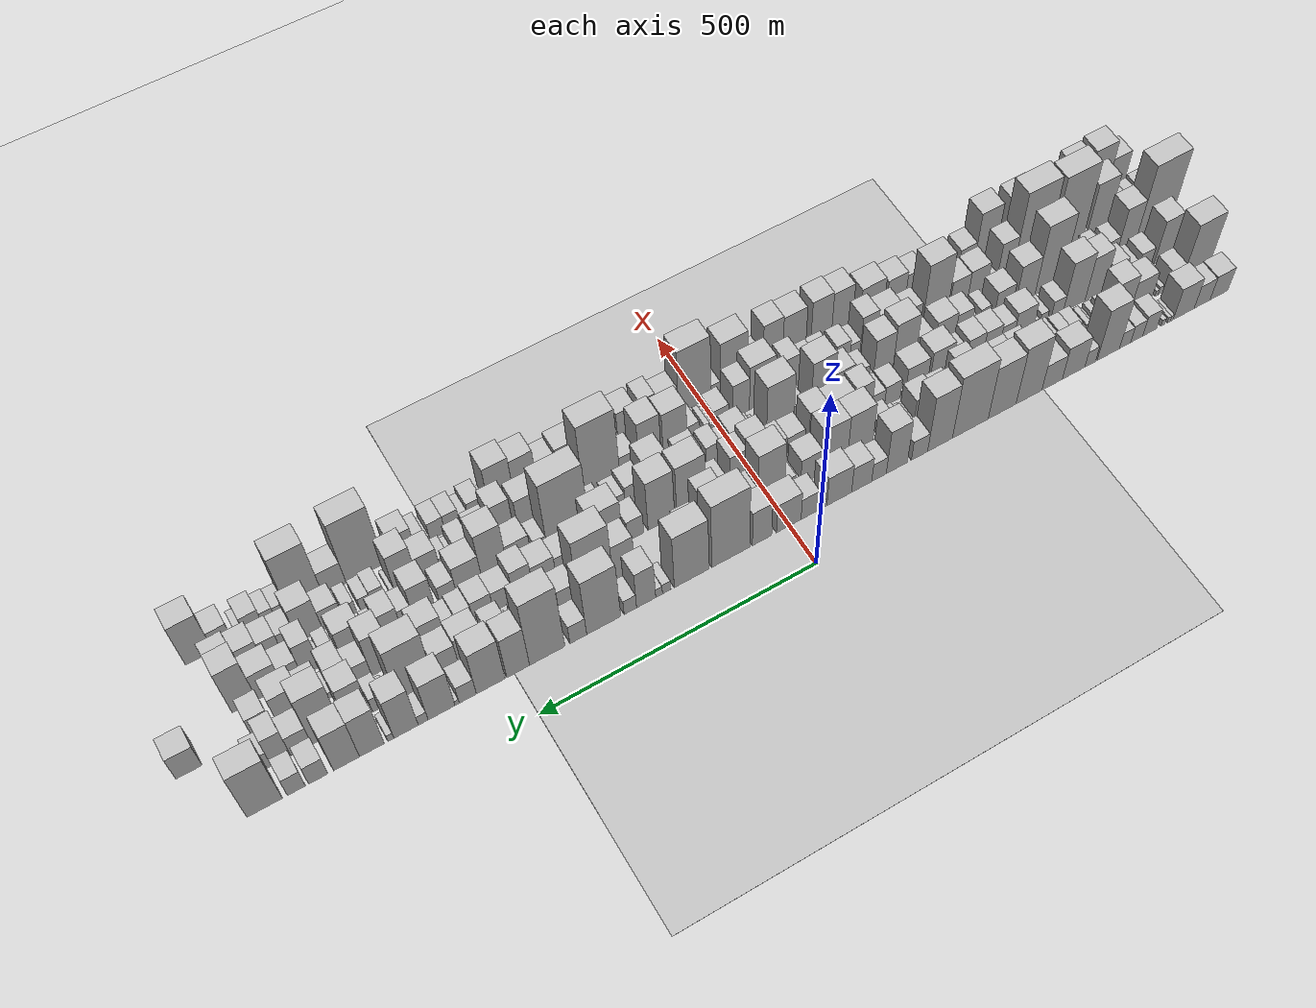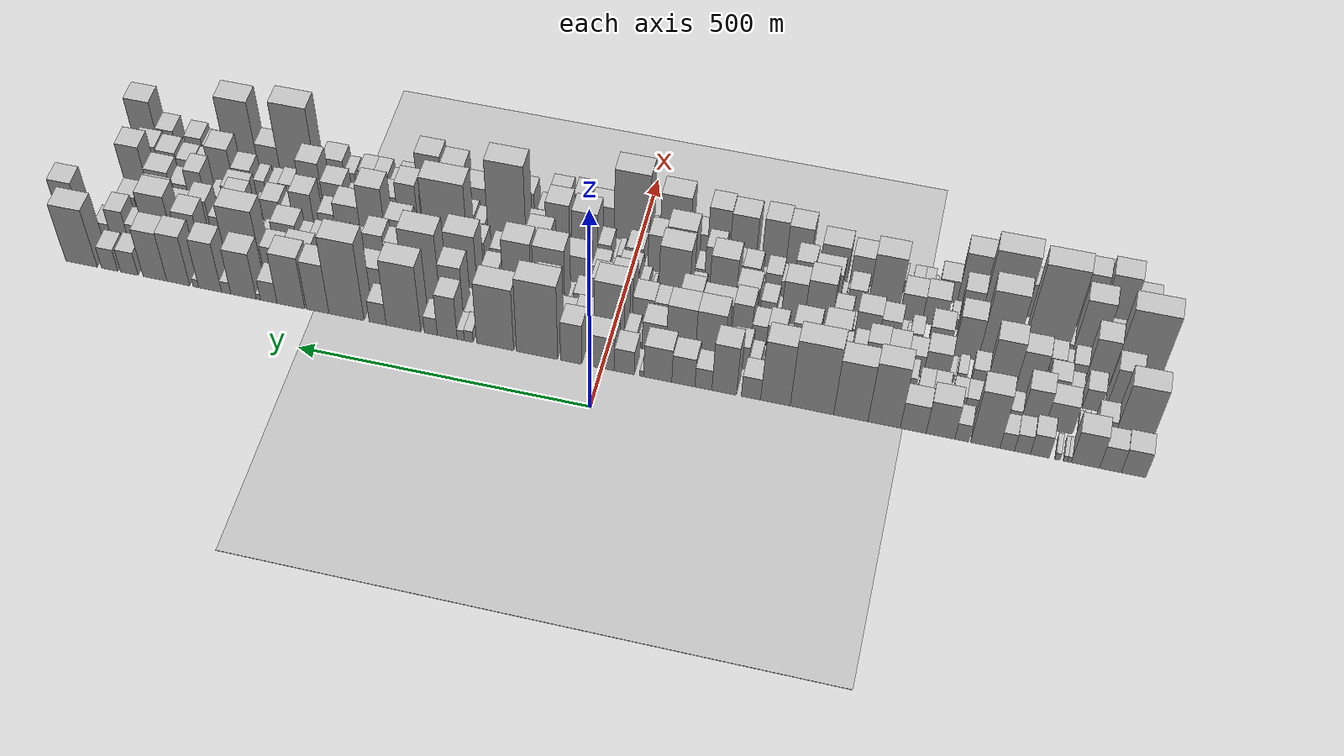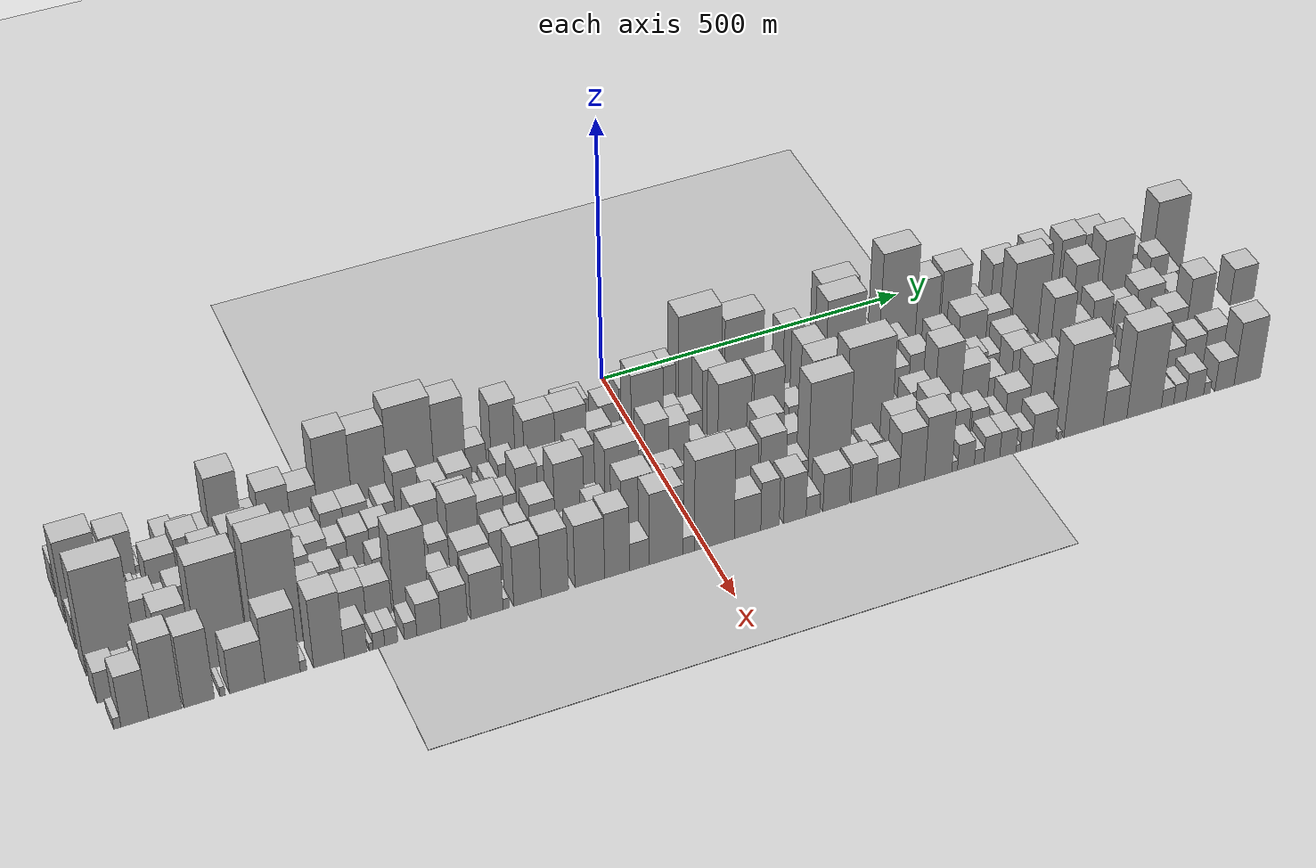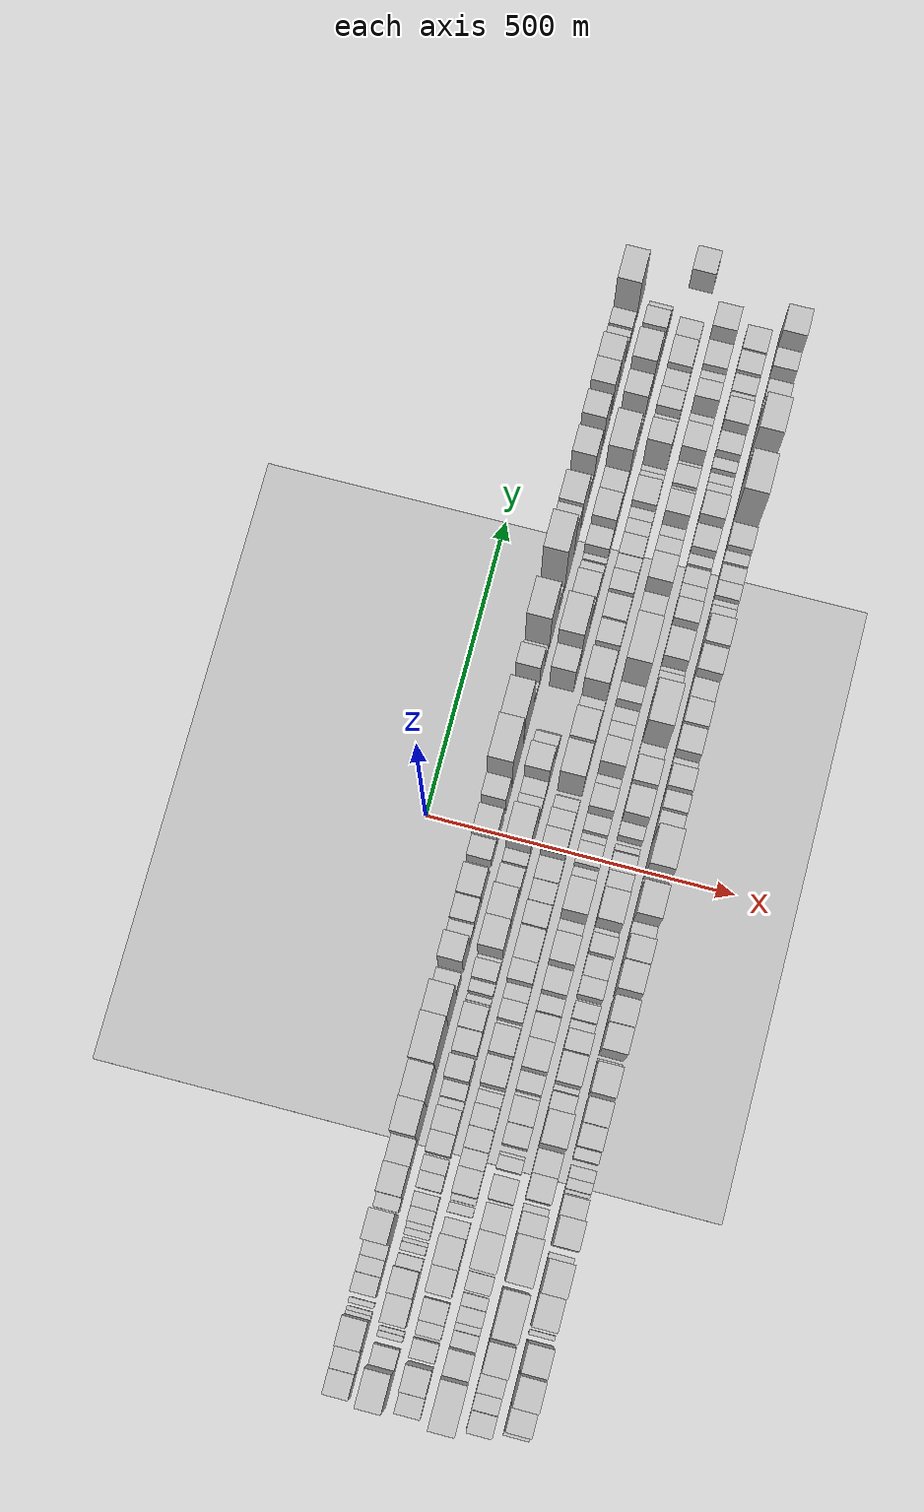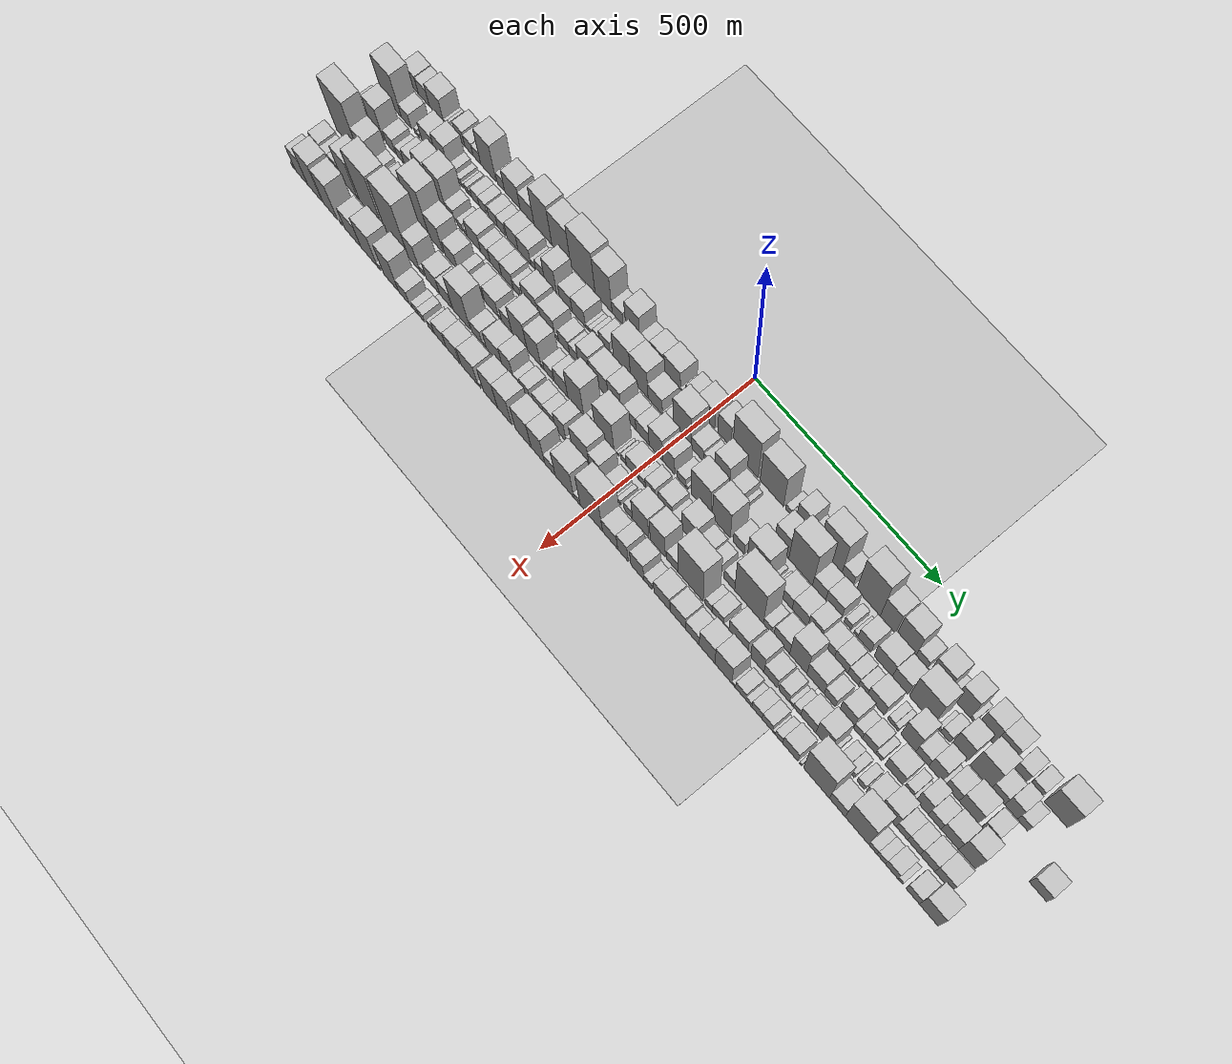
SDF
<?xml version="1.0" encoding="utf-8"?>

<sdf version="1.6">

   <world name="default">

      <gui fullscreen="0">

         <camera name="user_camera">

            <pose>-15 0 4.57585 0 0 0</pose>

            <view_controller>orbit</view_controller>

         </camera>

      </gui>

      <scene>

         <sky>

           <clouds>

             <speed>12</speed>

           </clouds>

         </sky>

         <ambient>0.4 0.4 0.4 1</ambient>

         <background>0.7 0.7 0.7 1</background>

         <shadows>1</shadows>

      </scene>

      <gravity>0 0 -9.8066</gravity>

      <magnetic_field>6e-06 2.3e-05 -4.2e-05</magnetic_field>

      <physics default="0" name="default_physics" type="ode">

         <ode>

            <solver>

               <type>quick</type>

               <iters>10</iters>

               <sor>1.0</sor>

               <use_dynamic_moi_rescaling>0</use_dynamic_moi_rescaling>

            </solver>

            <constraints>

               <cfm>0</cfm>

               <erp>0.2</erp>

               <contact_max_correcting_vel>100</contact_max_correcting_vel>

               <contact_surface_layer>0.001</contact_surface_layer>

            </constraints>

         </ode>

         <max_step_size>0.004</max_step_size>

         <real_time_factor>1</real_time_factor>

         <real_time_update_rate>250</real_time_update_rate>

      </physics>

      <light name="sun" type="directional">

         <cast_shadows>1</cast_shadows>

         <pose>0 0 10 0 0 0</pose>

         <diffuse>0.8 0.8 0.8 1</diffuse>

         <specular>0.2 0.2 0.2 1</specular>

         <attenuation>

            <range>1000</range>

            <constant>0.9</constant>

            <linear>0.01</linear>

            <quadratic>0.001</quadratic>

         </attenuation>

         <direction>-0.5 0.1 -0.9</direction>

      </light>

      <include>

         <name>ground_plane_1</name>

         <uri>model://HANNAS_ground_plane</uri>

         <pose>0 0 0  0 0 0</pose>

      </include>

      <include>

         <name>ground_plane_2</name>

         <uri>model://HANNAS_ground_plane</uri>

         <pose>100 0 0  0 0 0</pose>

      </include>

      <model name="building_1">

         <static>1</static>

         <pose frame="">100.0000 -870.5665 0 0.000000 0.000000 0.000000</pose>

         <link name="link">

            <pose frame="">0 0 33.00 0 0 0</pose>

            <collision name="collision">

               <geometry>

                  <box>

                     <size>40.0000 38.8670 66.0000</size>

                  </box>

               </geometry>

               <max_contacts>10</max_contacts>

               <surface>

                  <contact>

                     <ode/>

                  </contact>

                  <bounce/>

                  <friction>

                     <torsional>

                        <ode/>

                     </torsional>

                     <ode/>

                  </friction>

               </surface>

            </collision>

            <visual name="visual">

               <cast_shadows>0</cast_shadows>

               <geometry>

                  <box>

                     <size>40.0000 38.8670 66.0000</size>

                  </box>

               </geometry>

               <material>

                  <script>

                     <uri>model://HANNAS_wall/materials/scripts</uri>

                     <uri>model://HANNAS_wall/materials/textures</uri>

                     <name>vrc/HANNAS_wall</name>

                  </script>

               </material>

            </visual>

            <self_collide>0</self_collide>

            <enable_wind>0</enable_wind>

            <kinematic>0</kinematic>

         </link>

      </model>

      <model name="building_2">

         <static>1</static>

         <pose frame="">100.0000 -833.9637 0 0.000000 0.000000 0.000000</pose>

         <link name="link">

            <pose frame="">0 0 31.50 0 0 0</pose>

            <collision name="collision">

               <geometry>

                  <box>

                     <size>40.0000 34.3385 63.0000</size>

                  </box>

               </geometry>

               <max_contacts>10</max_contacts>

               <surface>

                  <contact>

                     <ode/>

                  </contact>

                  <bounce/>

                  <friction>

                     <torsional>

                        <ode/>

                     </torsional>

                     <ode/>

                  </friction>

               </surface>

            </collision>

            <visual name="visual">

               <cast_shadows>0</cast_shadows>

               <geometry>

                  <box>

                     <size>40.0000 34.3385 63.0000</size>

                  </box>

               </geometry>

               <material>

                  <script>

                     <uri>model://HANNAS_wall/materials/scripts</uri>

                     <uri>model://HANNAS_wall/materials/textures</uri>

                     <name>vrc/HANNAS_wall</name>

                  </script>

               </material>

            </visual>

            <self_collide>0</self_collide>

            <enable_wind>0</enable_wind>

            <kinematic>0</kinematic>

         </link>

      </model>

      <model name="building_3">

         <static>1</static>

         <pose frame="">100.0000 -794.2467 0 0.000000 0.000000 0.000000</pose>

         <link name="link">

            <pose frame="">0 0 43.50 0 0 0</pose>

            <collision name="collision">

               <geometry>

                  <box>

                     <size>40.0000 45.0955 87.0000</size>

                  </box>

               </geometry>

               <max_contacts>10</max_contacts>

               <surface>

                  <contact>

                     <ode/>

                  </contact>

                  <bounce/>

                  <friction>

                     <torsional>

                        <ode/>

                     </torsional>

                     <ode/>

                  </friction>

               </surface>

            </collision>

            <visual name="visual">

               <cast_shadows>0</cast_shadows>

               <geometry>

                  <box>

                     <size>40.0000 45.0955 87.0000</size>

                  </box>

               </geometry>

               <material>

                  <script>

                     <uri>model://HANNAS_wall/materials/scripts</uri>

                     <uri>model://HANNAS_wall/materials/textures</uri>

                     <name>vrc/HANNAS_wall</name>

                  </script>

               </material>

            </visual>

            <self_collide>0</self_collide>

            <enable_wind>0</enable_wind>

            <kinematic>0</kinematic>

         </link>

      </model>

      <model name="building_4">

         <static>1</static>

         <pose frame="">100.0000 -768.5291 0 0.000000 0.000000 0.000000</pose>

         <link name="link">

            <pose frame="">0 0 7.50 0 0 0</pose>

            <collision name="collision">

               <geometry>

                  <box>

                     <size>40.0000 6.3397 15.0000</size>

                  </box>

               </geometry>

               <max_contacts>10</max_contacts>

               <surface>

                  <contact>

                     <ode/>

                  </contact>

                  <bounce/>

                  <friction>

                     <torsional>

                        <ode/>

                     </torsional>

                     <ode/>

                  </friction>

               </surface>

            </collision>

            <visual name="visual">

               <cast_shadows>0</cast_shadows>

               <geometry>

                  <box>

                     <size>40.0000 6.3397 15.0000</size>

                  </box>

               </geometry>

               <material>

                  <script>

                     <uri>model://HANNAS_wall/materials/scripts</uri>

                     <uri>model://HANNAS_wall/materials/textures</uri>

                     <name>vrc/HANNAS_wall</name>

                  </script>

               </material>

            </visual>

            <self_collide>0</self_collide>

            <enable_wind>0</enable_wind>

            <kinematic>0</kinematic>

         </link>

      </model>

      <model name="building_5">

         <static>1</static>

         <pose frame="">100.0000 -762.1875 0 0.000000 0.000000 0.000000</pose>

         <link name="link">

            <pose frame="">0 0 7.50 0 0 0</pose>

            <collision name="collision">

               <geometry>

                  <box>

                     <size>40.0000 6.3436 15.0000</size>

                  </box>

               </geometry>

               <max_contacts>10</max_contacts>

               <surface>

                  <contact>

                     <ode/>

                  </contact>

                  <bounce/>

                  <friction>

                     <torsional>

                        <ode/>

                     </torsional>

                     <ode/>

                  </friction>

               </surface>

            </collision>

            <visual name="visual">

               <cast_shadows>0</cast_shadows>

               <geometry>

                  <box>

                     <size>40.0000 6.3436 15.0000</size>

                  </box>

               </geometry>

               <material>

                  <script>

                     <uri>model://HANNAS_wall/materials/scripts</uri>

                     <uri>model://HANNAS_wall/materials/textures</uri>

                     <name>vrc/HANNAS_wall</name>

                  </script>

               </material>

            </visual>

            <self_collide>0</self_collide>

            <enable_wind>0</enable_wind>

            <kinematic>0</kinematic>

         </link>

      </model>

      <model name="building_6">

         <static>1</static>

         <pose frame="">100.0000 -749.7658 0 0.000000 0.000000 0.000000</pose>

         <link name="link">

            <pose frame="">0 0 9.00 0 0 0</pose>

            <collision name="collision">

               <geometry>

                  <box>

                     <size>40.0000 8.4997 18.0000</size>

                  </box>

               </geometry>

               <max_contacts>10</max_contacts>

               <surface>

                  <contact>

                     <ode/>

                  </contact>

                  <bounce/>

                  <friction>

                     <torsional>

                        <ode/>

                     </torsional>

                     <ode/>

                  </friction>

               </surface>

            </collision>

            <visual name="visual">

               <cast_shadows>0</cast_shadows>

               <geometry>

                  <box>

                     <size>40.0000 8.4997 18.0000</size>

                  </box>

               </geometry>

               <material>

                  <script>

                     <uri>model://HANNAS_wall/materials/scripts</uri>

                     <uri>model://HANNAS_wall/materials/textures</uri>

                     <name>vrc/HANNAS_wall</name>

                  </script>

               </material>

            </visual>

            <self_collide>0</self_collide>

            <enable_wind>0</enable_wind>

            <kinematic>0</kinematic>

         </link>

      </model>

      <model name="building_7">

         <static>1</static>

         <pose frame="">100.0000 -721.4787 0 0.000000 0.000000 0.000000</pose>

         <link name="link">

            <pose frame="">0 0 28.50 0 0 0</pose>

            <collision name="collision">

               <geometry>

                  <box>

                     <size>40.0000 30.0746 57.0000</size>

                  </box>

               </geometry>

               <max_contacts>10</max_contacts>

               <surface>

                  <contact>

                     <ode/>

                  </contact>

                  <bounce/>

                  <friction>

                     <torsional>

                        <ode/>

                     </torsional>

                     <ode/>

                  </friction>

               </surface>

            </collision>

            <visual name="visual">

               <cast_shadows>0</cast_shadows>

               <geometry>

                  <box>

                     <size>40.0000 30.0746 57.0000</size>

                  </box>

               </geometry>

               <material>

                  <script>

                     <uri>model://HANNAS_wall/materials/scripts</uri>

                     <uri>model://HANNAS_wall/materials/textures</uri>

                     <name>vrc/HANNAS_wall</name>

                  </script>

               </material>

            </visual>

            <self_collide>0</self_collide>

            <enable_wind>0</enable_wind>

            <kinematic>0</kinematic>

         </link>

      </model>

      <model name="building_8">

         <static>1</static>

         <pose frame="">100.0000 -693.7319 0 0.000000 0.000000 0.000000</pose>

         <link name="link">

            <pose frame="">0 0 24.00 0 0 0</pose>

            <collision name="collision">

               <geometry>

                  <box>

                     <size>40.0000 25.4190 48.0000</size>

                  </box>

               </geometry>

               <max_contacts>10</max_contacts>

               <surface>

                  <contact>

                     <ode/>

                  </contact>

                  <bounce/>

                  <friction>

                     <torsional>

                        <ode/>

                     </torsional>

                     <ode/>

                  </friction>

               </surface>

            </collision>

            <visual name="visual">

               <cast_shadows>0</cast_shadows>

               <geometry>

                  <box>

                     <size>40.0000 25.4190 48.0000</size>

                  </box>

               </geometry>

               <material>

                  <script>

                     <uri>model://HANNAS_wall/materials/scripts</uri>

                     <uri>model://HANNAS_wall/materials/textures</uri>

                     <name>vrc/HANNAS_wall</name>

                  </script>

               </material>

            </visual>

            <self_collide>0</self_collide>

            <enable_wind>0</enable_wind>

            <kinematic>0</kinematic>

         </link>

      </model>

      <model name="building_9">

         <static>1</static>

         <pose frame="">100.0000 -669.3285 0 0.000000 0.000000 0.000000</pose>

         <link name="link">

            <pose frame="">0 0 22.50 0 0 0</pose>

            <collision name="collision">

               <geometry>

                  <box>

                     <size>40.0000 23.3877 45.0000</size>

                  </box>

               </geometry>

               <max_contacts>10</max_contacts>

               <surface>

                  <contact>

                     <ode/>

                  </contact>

                  <bounce/>

                  <friction>

                     <torsional>

                        <ode/>

                     </torsional>

                     <ode/>

                  </friction>

               </surface>

            </collision>

            <visual name="visual">

               <cast_shadows>0</cast_shadows>

               <geometry>

                  <box>

                     <size>40.0000 23.3877 45.0000</size>

                  </box>

               </geometry>

               <material>

                  <script>

                     <uri>model://HANNAS_wall/materials/scripts</uri>

                     <uri>model://HANNAS_wall/materials/textures</uri>

                     <name>vrc/HANNAS_wall</name>

                  </script>

               </material>

            </visual>

            <self_collide>0</self_collide>

            <enable_wind>0</enable_wind>

            <kinematic>0</kinematic>

         </link>

      </model>

      <model name="building_10">

         <static>1</static>

         <pose frame="">100.0000 -634.0826 0 0.000000 0.000000 0.000000</pose>

         <link name="link">

            <pose frame="">0 0 72.00 0 0 0</pose>

            <collision name="collision">

               <geometry>

                  <box>

                     <size>40.0000 47.1043 144.0000</size>

                  </box>

               </geometry>

               <max_contacts>10</max_contacts>

               <surface>

                  <contact>

                     <ode/>

                  </contact>

                  <bounce/>

                  <friction>

                     <torsional>

                        <ode/>

                     </torsional>

                     <ode/>

                  </friction>

               </surface>

            </collision>

            <visual name="visual">

               <cast_shadows>0</cast_shadows>

               <geometry>

                  <box>

                     <size>40.0000 47.1043 144.0000</size>

                  </box>

               </geometry>

               <material>

                  <script>

                     <uri>model://HANNAS_wall/materials/scripts</uri>

                     <uri>model://HANNAS_wall/materials/textures</uri>

                     <name>vrc/HANNAS_wall</name>

                  </script>

               </material>

            </visual>

            <self_collide>0</self_collide>

            <enable_wind>0</enable_wind>

            <kinematic>0</kinematic>

         </link>

      </model>

      <model name="building_11">

         <static>1</static>

         <pose frame="">100.0000 -596.2435 0 0.000000 0.000000 0.000000</pose>

         <link name="link">

            <pose frame="">0 0 22.50 0 0 0</pose>

            <collision name="collision">

               <geometry>

                  <box>

                     <size>40.0000 22.5739 45.0000</size>

                  </box>

               </geometry>

               <max_contacts>10</max_contacts>

               <surface>

                  <contact>

                     <ode/>

                  </contact>

                  <bounce/>

                  <friction>

                     <torsional>

                        <ode/>

                     </torsional>

                     <ode/>

                  </friction>

               </surface>

            </collision>

            <visual name="visual">

               <cast_shadows>0</cast_shadows>

               <geometry>

                  <box>

                     <size>40.0000 22.5739 45.0000</size>

                  </box>

               </geometry>

               <material>

                  <script>

                     <uri>model://HANNAS_wall/materials/scripts</uri>

                     <uri>model://HANNAS_wall/materials/textures</uri>

                     <name>vrc/HANNAS_wall</name>

                  </script>

               </material>

            </visual>

            <self_collide>0</self_collide>

            <enable_wind>0</enable_wind>

            <kinematic>0</kinematic>

         </link>

      </model>

      <model name="building_12">

         <static>1</static>

         <pose frame="">100.0000 -561.6605 0 0.000000 0.000000 0.000000</pose>

         <link name="link">

            <pose frame="">0 0 45.00 0 0 0</pose>

            <collision name="collision">

               <geometry>

                  <box>

                     <size>40.0000 46.5919 90.0000</size>

                  </box>

               </geometry>

               <max_contacts>10</max_contacts>

               <surface>

                  <contact>

                     <ode/>

                  </contact>

                  <bounce/>

                  <friction>

                     <torsional>

                        <ode/>

                     </torsional>

                     <ode/>

                  </friction>

               </surface>

            </collision>

            <visual name="visual">

               <cast_shadows>0</cast_shadows>

               <geometry>

                  <box>

                     <size>40.0000 46.5919 90.0000</size>

                  </box>

               </geometry>

               <material>

                  <script>

                     <uri>model://HANNAS_wall/materials/scripts</uri>

                     <uri>model://HANNAS_wall/materials/textures</uri>

                     <name>vrc/HANNAS_wall</name>

                  </script>

               </material>

            </visual>

            <self_collide>0</self_collide>

            <enable_wind>0</enable_wind>

            <kinematic>0</kinematic>

         </link>

      </model>

      <model name="building_13">

         <static>1</static>

         <pose frame="">100.0000 -517.2988 0 0.000000 0.000000 0.000000</pose>

         <link name="link">

            <pose frame="">0 0 36.00 0 0 0</pose>

            <collision name="collision">

               <geometry>

                  <box>

                     <size>40.0000 42.1315 72.0000</size>

                  </box>

               </geometry>

               <max_contacts>10</max_contacts>

               <surface>

                  <contact>

                     <ode/>

                  </contact>

                  <bounce/>

                  <friction>

                     <torsional>

                        <ode/>

                     </torsional>

                     <ode/>

                  </friction>

               </surface>

            </collision>

            <visual name="visual">

               <cast_shadows>0</cast_shadows>

               <geometry>

                  <box>

                     <size>40.0000 42.1315 72.0000</size>

                  </box>

               </geometry>

               <material>

                  <script>

                     <uri>model://HANNAS_wall/materials/scripts</uri>

                     <uri>model://HANNAS_wall/materials/textures</uri>

                     <name>vrc/HANNAS_wall</name>

                  </script>

               </material>

            </visual>

            <self_collide>0</self_collide>

            <enable_wind>0</enable_wind>

            <kinematic>0</kinematic>

         </link>

      </model>

      <model name="building_14">

         <static>1</static>

         <pose frame="">100.0000 -469.8203 0 0.000000 0.000000 0.000000</pose>

         <link name="link">

            <pose frame="">0 0 81.00 0 0 0</pose>

            <collision name="collision">

               <geometry>

                  <box>

                     <size>40.0000 52.8255 162.0000</size>

                  </box>

               </geometry>

               <max_contacts>10</max_contacts>

               <surface>

                  <contact>

                     <ode/>

                  </contact>

                  <bounce/>

                  <friction>

                     <torsional>

                        <ode/>

                     </torsional>

                     <ode/>

                  </friction>

               </surface>

            </collision>

            <visual name="visual">

               <cast_shadows>0</cast_shadows>

               <geometry>

                  <box>

                     <size>40.0000 52.8255 162.0000</size>

                  </box>

               </geometry>

               <material>

                  <script>

                     <uri>model://HANNAS_wall/materials/scripts</uri>

                     <uri>model://HANNAS_wall/materials/textures</uri>

                     <name>vrc/HANNAS_wall</name>

                  </script>

               </material>

            </visual>

            <self_collide>0</self_collide>

            <enable_wind>0</enable_wind>

            <kinematic>0</kinematic>

         </link>

      </model>

      <model name="building_15">

         <static>1</static>

         <pose frame="">100.0000 -415.1986 0 0.000000 0.000000 0.000000</pose>

         <link name="link">

            <pose frame="">0 0 75.00 0 0 0</pose>

            <collision name="collision">

               <geometry>

                  <box>

                     <size>40.0000 56.4179 150.0000</size>

                  </box>

               </geometry>

               <max_contacts>10</max_contacts>

               <surface>

                  <contact>

                     <ode/>

                  </contact>

                  <bounce/>

                  <friction>

                     <torsional>

                        <ode/>

                     </torsional>

                     <ode/>

                  </friction>

               </surface>

            </collision>

            <visual name="visual">

               <cast_shadows>0</cast_shadows>

               <geometry>

                  <box>

                     <size>40.0000 56.4179 150.0000</size>

                  </box>

               </geometry>

               <material>

                  <script>

                     <uri>model://HANNAS_wall/materials/scripts</uri>

                     <uri>model://HANNAS_wall/materials/textures</uri>

                     <name>vrc/HANNAS_wall</name>

                  </script>

               </material>

            </visual>

            <self_collide>0</self_collide>

            <enable_wind>0</enable_wind>

            <kinematic>0</kinematic>

         </link>

      </model>

      <model name="building_16">

         <static>1</static>

         <pose frame="">100.0000 -351.2079 0 0.000000 0.000000 0.000000</pose>

         <link name="link">

            <pose frame="">0 0 90.00 0 0 0</pose>

            <collision name="collision">

               <geometry>

                  <box>

                     <size>40.0000 71.5635 180.0000</size>

                  </box>

               </geometry>

               <max_contacts>10</max_contacts>

               <surface>

                  <contact>

                     <ode/>

                  </contact>

                  <bounce/>

                  <friction>

                     <torsional>

                        <ode/>

                     </torsional>

                     <ode/>

                  </friction>

               </surface>

            </collision>

            <visual name="visual">

               <cast_shadows>0</cast_shadows>

               <geometry>

                  <box>

                     <size>40.0000 71.5635 180.0000</size>

                  </box>

               </geometry>

               <material>

                  <script>

                     <uri>model://HANNAS_wall/materials/scripts</uri>

                     <uri>model://HANNAS_wall/materials/textures</uri>

                     <name>vrc/HANNAS_wall</name>

                  </script>

               </material>

            </visual>

            <self_collide>0</self_collide>

            <enable_wind>0</enable_wind>

            <kinematic>0</kinematic>

         </link>

      </model>

      <model name="building_17">

         <static>1</static>

         <pose frame="">100.0000 -290.7878 0 0.000000 0.000000 0.000000</pose>

         <link name="link">

            <pose frame="">0 0 81.00 0 0 0</pose>

            <collision name="collision">

               <geometry>

                  <box>

                     <size>40.0000 49.2768 162.0000</size>

                  </box>

               </geometry>

               <max_contacts>10</max_contacts>

               <surface>

                  <contact>

                     <ode/>

                  </contact>

                  <bounce/>

                  <friction>

                     <torsional>

                        <ode/>

                     </torsional>

                     <ode/>

                  </friction>

               </surface>

            </collision>

            <visual name="visual">

               <cast_shadows>0</cast_shadows>

               <geometry>

                  <box>

                     <size>40.0000 49.2768 162.0000</size>

                  </box>

               </geometry>

               <material>

                  <script>

                     <uri>model://HANNAS_wall/materials/scripts</uri>

                     <uri>model://HANNAS_wall/materials/textures</uri>

                     <name>vrc/HANNAS_wall</name>

                  </script>

               </material>

            </visual>

            <self_collide>0</self_collide>

            <enable_wind>0</enable_wind>

            <kinematic>0</kinematic>

         </link>

      </model>

      <model name="building_18">

         <static>1</static>

         <pose frame="">100.0000 -250.1344 0 0.000000 0.000000 0.000000</pose>

         <link name="link">

            <pose frame="">0 0 28.50 0 0 0</pose>

            <collision name="collision">

               <geometry>

                  <box>

                     <size>40.0000 32.0299 57.0000</size>

                  </box>

               </geometry>

               <max_contacts>10</max_contacts>

               <surface>

                  <contact>

                     <ode/>

                  </contact>

                  <bounce/>

                  <friction>

                     <torsional>

                        <ode/>

                     </torsional>

                     <ode/>

                  </friction>

               </surface>

            </collision>

            <visual name="visual">

               <cast_shadows>0</cast_shadows>

               <geometry>

                  <box>

                     <size>40.0000 32.0299 57.0000</size>

                  </box>

               </geometry>

               <material>

                  <script>

                     <uri>model://HANNAS_wall/materials/scripts</uri>

                     <uri>model://HANNAS_wall/materials/textures</uri>

                     <name>vrc/HANNAS_wall</name>

                  </script>

               </material>

            </visual>

            <self_collide>0</self_collide>

            <enable_wind>0</enable_wind>

            <kinematic>0</kinematic>

         </link>

      </model>

      <model name="building_19">

         <static>1</static>

         <pose frame="">100.0000 -205.5456 0 0.000000 0.000000 0.000000</pose>

         <link name="link">

            <pose frame="">0 0 64.50 0 0 0</pose>

            <collision name="collision">

               <geometry>

                  <box>

                     <size>40.0000 41.1477 129.0000</size>

                  </box>

               </geometry>

               <max_contacts>10</max_contacts>

               <surface>

                  <contact>

                     <ode/>

                  </contact>

                  <bounce/>

                  <friction>

                     <torsional>

                        <ode/>

                     </torsional>

                     <ode/>

                  </friction>

               </surface>

            </collision>

            <visual name="visual">

               <cast_shadows>0</cast_shadows>

               <geometry>

                  <box>

                     <size>40.0000 41.1477 129.0000</size>

                  </box>

               </geometry>

               <material>

                  <script>

                     <uri>model://HANNAS_wall/materials/scripts</uri>

                     <uri>model://HANNAS_wall/materials/textures</uri>

                     <name>vrc/HANNAS_wall</name>

                  </script>

               </material>

            </visual>

            <self_collide>0</self_collide>

            <enable_wind>0</enable_wind>

            <kinematic>0</kinematic>

         </link>

      </model>

      <model name="building_20">

         <static>1</static>

         <pose frame="">100.0000 -170.7618 0 0.000000 0.000000 0.000000</pose>

         <link name="link">

            <pose frame="">0 0 27.00 0 0 0</pose>

            <collision name="collision">

               <geometry>

                  <box>

                     <size>40.0000 28.4199 54.0000</size>

                  </box>

               </geometry>

               <max_contacts>10</max_contacts>

               <surface>

                  <contact>

                     <ode/>

                  </contact>

                  <bounce/>

                  <friction>

                     <torsional>

                        <ode/>

                     </torsional>

                     <ode/>

                  </friction>

               </surface>

            </collision>

            <visual name="visual">

               <cast_shadows>0</cast_shadows>

               <geometry>

                  <box>

                     <size>40.0000 28.4199 54.0000</size>

                  </box>

               </geometry>

               <material>

                  <script>

                     <uri>model://HANNAS_wall/materials/scripts</uri>

                     <uri>model://HANNAS_wall/materials/textures</uri>

                     <name>vrc/HANNAS_wall</name>

                  </script>

               </material>

            </visual>

            <self_collide>0</self_collide>

            <enable_wind>0</enable_wind>

            <kinematic>0</kinematic>

         </link>

      </model>

      <model name="building_21">

         <static>1</static>

         <pose frame="">100.0000 -137.1133 0 0.000000 0.000000 0.000000</pose>

         <link name="link">

            <pose frame="">0 0 37.50 0 0 0</pose>

            <collision name="collision">

               <geometry>

                  <box>

                     <size>40.0000 38.8770 75.0000</size>

                  </box>

               </geometry>

               <max_contacts>10</max_contacts>

               <surface>

                  <contact>

                     <ode/>

                  </contact>

                  <bounce/>

                  <friction>

                     <torsional>

                        <ode/>

                     </torsional>

                     <ode/>

                  </friction>

               </surface>

            </collision>

            <visual name="visual">

               <cast_shadows>0</cast_shadows>

               <geometry>

                  <box>

                     <size>40.0000 38.8770 75.0000</size>

                  </box>

               </geometry>

               <material>

                  <script>

                     <uri>model://HANNAS_wall/materials/scripts</uri>

                     <uri>model://HANNAS_wall/materials/textures</uri>

                     <name>vrc/HANNAS_wall</name>

                  </script>

               </material>

            </visual>

            <self_collide>0</self_collide>

            <enable_wind>0</enable_wind>

            <kinematic>0</kinematic>

         </link>

      </model>

      <model name="building_22">

         <static>1</static>

         <pose frame="">100.0000 -93.9730 0 0.000000 0.000000 0.000000</pose>

         <link name="link">

            <pose frame="">0 0 43.50 0 0 0</pose>

            <collision name="collision">

               <geometry>

                  <box>

                     <size>40.0000 47.4036 87.0000</size>

                  </box>

               </geometry>

               <max_contacts>10</max_contacts>

               <surface>

                  <contact>

                     <ode/>

                  </contact>

                  <bounce/>

                  <friction>

                     <torsional>

                        <ode/>

                     </torsional>

                     <ode/>

                  </friction>

               </surface>

            </collision>

            <visual name="visual">

               <cast_shadows>0</cast_shadows>

               <geometry>

                  <box>

                     <size>40.0000 47.4036 87.0000</size>

                  </box>

               </geometry>

               <material>

                  <script>

                     <uri>model://HANNAS_wall/materials/scripts</uri>

                     <uri>model://HANNAS_wall/materials/textures</uri>

                     <name>vrc/HANNAS_wall</name>

                  </script>

               </material>

            </visual>

            <self_collide>0</self_collide>

            <enable_wind>0</enable_wind>

            <kinematic>0</kinematic>

         </link>

      </model>

      <model name="building_23">

         <static>1</static>

         <pose frame="">100.0000 -66.9445 0 0.000000 0.000000 0.000000</pose>

         <link name="link">

            <pose frame="">0 0 7.50 0 0 0</pose>

            <collision name="collision">

               <geometry>

                  <box>

                     <size>40.0000 6.6534 15.0000</size>

                  </box>

               </geometry>

               <max_contacts>10</max_contacts>

               <surface>

                  <contact>

                     <ode/>

                  </contact>

                  <bounce/>

                  <friction>

                     <torsional>

                        <ode/>

                     </torsional>

                     <ode/>

                  </friction>

               </surface>

            </collision>

            <visual name="visual">

               <cast_shadows>0</cast_shadows>

               <geometry>

                  <box>

                     <size>40.0000 6.6534 15.0000</size>

                  </box>

               </geometry>

               <material>

                  <script>

                     <uri>model://HANNAS_wall/materials/scripts</uri>

                     <uri>model://HANNAS_wall/materials/textures</uri>

                     <name>vrc/HANNAS_wall</name>

                  </script>

               </material>

            </visual>

            <self_collide>0</self_collide>

            <enable_wind>0</enable_wind>

            <kinematic>0</kinematic>

         </link>

      </model>

      <model name="building_24">

         <static>1</static>

         <pose frame="">100.0000 -37.7825 0 0.000000 0.000000 0.000000</pose>

         <link name="link">

            <pose frame="">0 0 31.50 0 0 0</pose>

            <collision name="collision">

               <geometry>

                  <box>

                     <size>40.0000 33.6706 63.0000</size>

                  </box>

               </geometry>

               <max_contacts>10</max_contacts>

               <surface>

                  <contact>

                     <ode/>

                  </contact>

                  <bounce/>

                  <friction>

                     <torsional>

                        <ode/>

                     </torsional>

                     <ode/>

                  </friction>

               </surface>

            </collision>

            <visual name="visual">

               <cast_shadows>0</cast_shadows>

               <geometry>

                  <box>

                     <size>40.0000 33.6706 63.0000</size>

                  </box>

               </geometry>

               <material>

                  <script>

                     <uri>model://HANNAS_wall/materials/scripts</uri>

                     <uri>model://HANNAS_wall/materials/textures</uri>

                     <name>vrc/HANNAS_wall</name>

                  </script>

               </material>

            </visual>

            <self_collide>0</self_collide>

            <enable_wind>0</enable_wind>

            <kinematic>0</kinematic>

         </link>

      </model>

      <model name="building_25">

         <static>1</static>

         <pose frame="">100.0000 2.3220 0 0.000000 0.000000 0.000000</pose>

         <link name="link">

            <pose frame="">0 0 43.50 0 0 0</pose>

            <collision name="collision">

               <geometry>

                  <box>

                     <size>40.0000 46.5383 87.0000</size>

                  </box>

               </geometry>

               <max_contacts>10</max_contacts>

               <surface>

                  <contact>

                     <ode/>

                  </contact>

                  <bounce/>

                  <friction>

                     <torsional>

                        <ode/>

                     </torsional>

                     <ode/>

                  </friction>

               </surface>

            </collision>

            <visual name="visual">

               <cast_shadows>0</cast_shadows>

               <geometry>

                  <box>

                     <size>40.0000 46.5383 87.0000</size>

                  </box>

               </geometry>

               <material>

                  <script>

                     <uri>model://HANNAS_wall/materials/scripts</uri>

                     <uri>model://HANNAS_wall/materials/textures</uri>

                     <name>vrc/HANNAS_wall</name>

                  </script>

               </material>

            </visual>

            <self_collide>0</self_collide>

            <enable_wind>0</enable_wind>

            <kinematic>0</kinematic>

         </link>

      </model>

      <model name="building_26">

         <static>1</static>

         <pose frame="">100.0000 52.6891 0 0.000000 0.000000 0.000000</pose>

         <link name="link">

            <pose frame="">0 0 52.50 0 0 0</pose>

            <collision name="collision">

               <geometry>

                  <box>

                     <size>40.0000 36.1959 105.0000</size>

                  </box>

               </geometry>

               <max_contacts>10</max_contacts>

               <surface>

                  <contact>

                     <ode/>

                  </contact>

                  <bounce/>

                  <friction>

                     <torsional>

                        <ode/>

                     </torsional>

                     <ode/>

                  </friction>

               </surface>

            </collision>

            <visual name="visual">

               <cast_shadows>0</cast_shadows>

               <geometry>

                  <box>

                     <size>40.0000 36.1959 105.0000</size>

                  </box>

               </geometry>

               <material>

                  <script>

                     <uri>model://HANNAS_wall/materials/scripts</uri>

                     <uri>model://HANNAS_wall/materials/textures</uri>

                     <name>vrc/HANNAS_wall</name>

                  </script>

               </material>

            </visual>

            <self_collide>0</self_collide>

            <enable_wind>0</enable_wind>

            <kinematic>0</kinematic>

         </link>

      </model>

      <model name="building_27">

         <static>1</static>

         <pose frame="">100.0000 111.0224 0 0.000000 0.000000 0.000000</pose>

         <link name="link">

            <pose frame="">0 0 97.50 0 0 0</pose>

            <collision name="collision">

               <geometry>

                  <box>

                     <size>40.0000 70.4707 195.0000</size>

                  </box>

               </geometry>

               <max_contacts>10</max_contacts>

               <surface>

                  <contact>

                     <ode/>

                  </contact>

                  <bounce/>

                  <friction>

                     <torsional>

                        <ode/>

                     </torsional>

                     <ode/>

                  </friction>

               </surface>

            </collision>

            <visual name="visual">

               <cast_shadows>0</cast_shadows>

               <geometry>

                  <box>

                     <size>40.0000 70.4707 195.0000</size>

                  </box>

               </geometry>

               <material>

                  <script>

                     <uri>model://HANNAS_wall/materials/scripts</uri>

                     <uri>model://HANNAS_wall/materials/textures</uri>

                     <name>vrc/HANNAS_wall</name>

                  </script>

               </material>

            </visual>

            <self_collide>0</self_collide>

            <enable_wind>0</enable_wind>

            <kinematic>0</kinematic>

         </link>

      </model>

      <model name="building_28">

         <static>1</static>

         <pose frame="">100.0000 183.2015 0 0.000000 0.000000 0.000000</pose>

         <link name="link">

            <pose frame="">0 0 81.00 0 0 0</pose>

            <collision name="collision">

               <geometry>

                  <box>

                     <size>40.0000 63.8877 162.0000</size>

                  </box>

               </geometry>

               <max_contacts>10</max_contacts>

               <surface>

                  <contact>

                     <ode/>

                  </contact>

                  <bounce/>

                  <friction>

                     <torsional>

                        <ode/>

                     </torsional>

                     <ode/>

                  </friction>

               </surface>

            </collision>

            <visual name="visual">

               <cast_shadows>0</cast_shadows>

               <geometry>

                  <box>

                     <size>40.0000 63.8877 162.0000</size>

                  </box>

               </geometry>

               <material>

                  <script>

                     <uri>model://HANNAS_wall/materials/scripts</uri>

                     <uri>model://HANNAS_wall/materials/textures</uri>

                     <name>vrc/HANNAS_wall</name>

                  </script>

               </material>

            </visual>

            <self_collide>0</self_collide>

            <enable_wind>0</enable_wind>

            <kinematic>0</kinematic>

         </link>

      </model>

      <model name="building_29">

         <static>1</static>

         <pose frame="">100.0000 228.8437 0 0.000000 0.000000 0.000000</pose>

         <link name="link">

            <pose frame="">0 0 15.00 0 0 0</pose>

            <collision name="collision">

               <geometry>

                  <box>

                     <size>40.0000 15.3966 30.0000</size>

                  </box>

               </geometry>

               <max_contacts>10</max_contacts>

               <surface>

                  <contact>

                     <ode/>

                  </contact>

                  <bounce/>

                  <friction>

                     <torsional>

                        <ode/>

                     </torsional>

                     <ode/>

                  </friction>

               </surface>

            </collision>

            <visual name="visual">

               <cast_shadows>0</cast_shadows>

               <geometry>

                  <box>

                     <size>40.0000 15.3966 30.0000</size>

                  </box>

               </geometry>

               <material>

                  <script>

                     <uri>model://HANNAS_wall/materials/scripts</uri>

                     <uri>model://HANNAS_wall/materials/textures</uri>

                     <name>vrc/HANNAS_wall</name>

                  </script>

               </material>

            </visual>

            <self_collide>0</self_collide>

            <enable_wind>0</enable_wind>

            <kinematic>0</kinematic>

         </link>

      </model>

      <model name="building_30">

         <static>1</static>

         <pose frame="">100.0000 242.6706 0 0.000000 0.000000 0.000000</pose>

         <link name="link">

            <pose frame="">0 0 13.50 0 0 0</pose>

            <collision name="collision">

               <geometry>

                  <box>

                     <size>40.0000 12.2572 27.0000</size>

                  </box>

               </geometry>

               <max_contacts>10</max_contacts>

               <surface>

                  <contact>

                     <ode/>

                  </contact>

                  <bounce/>

                  <friction>

                     <torsional>

                        <ode/>

                     </torsional>

                     <ode/>

                  </friction>

               </surface>

            </collision>

            <visual name="visual">

               <cast_shadows>0</cast_shadows>

               <geometry>

                  <box>

                     <size>40.0000 12.2572 27.0000</size>

                  </box>

               </geometry>

               <material>

                  <script>

                     <uri>model://HANNAS_wall/materials/scripts</uri>

                     <uri>model://HANNAS_wall/materials/textures</uri>

                     <name>vrc/HANNAS_wall</name>

                  </script>

               </material>

            </visual>

            <self_collide>0</self_collide>

            <enable_wind>0</enable_wind>

            <kinematic>0</kinematic>

         </link>

      </model>

      <model name="building_31">

         <static>1</static>

         <pose frame="">100.0000 266.0972 0 0.000000 0.000000 0.000000</pose>

         <link name="link">

            <pose frame="">0 0 55.50 0 0 0</pose>

            <collision name="collision">

               <geometry>

                  <box>

                     <size>40.0000 34.5961 111.0000</size>

                  </box>

               </geometry>

               <max_contacts>10</max_contacts>

               <surface>

                  <contact>

                     <ode/>

                  </contact>

                  <bounce/>

                  <friction>

                     <torsional>

                        <ode/>

                     </torsional>

                     <ode/>

                  </friction>

               </surface>

            </collision>

            <visual name="visual">

               <cast_shadows>0</cast_shadows>

               <geometry>

                  <box>

                     <size>40.0000 34.5961 111.0000</size>

                  </box>

               </geometry>

               <material>

                  <script>

                     <uri>model://HANNAS_wall/materials/scripts</uri>

                     <uri>model://HANNAS_wall/materials/textures</uri>

                     <name>vrc/HANNAS_wall</name>

                  </script>

               </material>

            </visual>

            <self_collide>0</self_collide>

            <enable_wind>0</enable_wind>

            <kinematic>0</kinematic>

         </link>

      </model>

      <model name="building_32">

         <static>1</static>

         <pose frame="">100.0000 294.6586 0 0.000000 0.000000 0.000000</pose>

         <link name="link">

            <pose frame="">0 0 22.50 0 0 0</pose>

            <collision name="collision">

               <geometry>

                  <box>

                     <size>40.0000 22.5267 45.0000</size>

                  </box>

               </geometry>

               <max_contacts>10</max_contacts>

               <surface>

                  <contact>

                     <ode/>

                  </contact>

                  <bounce/>

                  <friction>

                     <torsional>

                        <ode/>

                     </torsional>

                     <ode/>

                  </friction>

               </surface>

            </collision>

            <visual name="visual">

               <cast_shadows>0</cast_shadows>

               <geometry>

                  <box>

                     <size>40.0000 22.5267 45.0000</size>

                  </box>

               </geometry>

               <material>

                  <script>

                     <uri>model://HANNAS_wall/materials/scripts</uri>

                     <uri>model://HANNAS_wall/materials/textures</uri>

                     <name>vrc/HANNAS_wall</name>

                  </script>

               </material>

            </visual>

            <self_collide>0</self_collide>

            <enable_wind>0</enable_wind>

            <kinematic>0</kinematic>

         </link>

      </model>

      <model name="building_33">

         <static>1</static>

         <pose frame="">100.0000 342.3080 0 0.000000 0.000000 0.000000</pose>

         <link name="link">

            <pose frame="">0 0 87.00 0 0 0</pose>

            <collision name="collision">

               <geometry>

                  <box>

                     <size>40.0000 60.7721 174.0000</size>

                  </box>

               </geometry>

               <max_contacts>10</max_contacts>

               <surface>

                  <contact>

                     <ode/>

                  </contact>

                  <bounce/>

                  <friction>

                     <torsional>

                        <ode/>

                     </torsional>

                     <ode/>

                  </friction>

               </surface>

            </collision>

            <visual name="visual">

               <cast_shadows>0</cast_shadows>

               <geometry>

                  <box>

                     <size>40.0000 60.7721 174.0000</size>

                  </box>

               </geometry>

               <material>

                  <script>

                     <uri>model://HANNAS_wall/materials/scripts</uri>

                     <uri>model://HANNAS_wall/materials/textures</uri>

                     <name>vrc/HANNAS_wall</name>

                  </script>

               </material>

            </visual>

            <self_collide>0</self_collide>

            <enable_wind>0</enable_wind>

            <kinematic>0</kinematic>

         </link>

      </model>

      <model name="building_34">

         <static>1</static>

         <pose frame="">100.0000 387.5385 0 0.000000 0.000000 0.000000</pose>

         <link name="link">

            <pose frame="">0 0 28.50 0 0 0</pose>

            <collision name="collision">

               <geometry>

                  <box>

                     <size>40.0000 29.6889 57.0000</size>

                  </box>

               </geometry>

               <max_contacts>10</max_contacts>

               <surface>

                  <contact>

                     <ode/>

                  </contact>

                  <bounce/>

                  <friction>

                     <torsional>

                        <ode/>

                     </torsional>

                     <ode/>

                  </friction>

               </surface>

            </collision>

            <visual name="visual">

               <cast_shadows>0</cast_shadows>

               <geometry>

                  <box>

                     <size>40.0000 29.6889 57.0000</size>

                  </box>

               </geometry>

               <material>

                  <script>

                     <uri>model://HANNAS_wall/materials/scripts</uri>

                     <uri>model://HANNAS_wall/materials/textures</uri>

                     <name>vrc/HANNAS_wall</name>

                  </script>

               </material>

            </visual>

            <self_collide>0</self_collide>

            <enable_wind>0</enable_wind>

            <kinematic>0</kinematic>

         </link>

      </model>

      <model name="building_35">

         <static>1</static>

         <pose frame="">100.0000 442.3553 0 0.000000 0.000000 0.000000</pose>

         <link name="link">

            <pose frame="">0 0 102.00 0 0 0</pose>

            <collision name="collision">

               <geometry>

                  <box>

                     <size>40.0000 61.9446 204.0000</size>

                  </box>

               </geometry>

               <max_contacts>10</max_contacts>

               <surface>

                  <contact>

                     <ode/>

                  </contact>

                  <bounce/>

                  <friction>

                     <torsional>

                        <ode/>

                     </torsional>

                     <ode/>

                  </friction>

               </surface>

            </collision>

            <visual name="visual">

               <cast_shadows>0</cast_shadows>

               <geometry>

                  <box>

                     <size>40.0000 61.9446 204.0000</size>

                  </box>

               </geometry>

               <material>

                  <script>

                     <uri>model://HANNAS_wall/materials/scripts</uri>

                     <uri>model://HANNAS_wall/materials/textures</uri>

                     <name>vrc/HANNAS_wall</name>

                  </script>

               </material>

            </visual>

            <self_collide>0</self_collide>

            <enable_wind>0</enable_wind>

            <kinematic>0</kinematic>

         </link>

      </model>

      <model name="building_36">

         <static>1</static>

         <pose frame="">100.0000 493.2041 0 0.000000 0.000000 0.000000</pose>

         <link name="link">

            <pose frame="">0 0 64.50 0 0 0</pose>

            <collision name="collision">

               <geometry>

                  <box>

                     <size>40.0000 39.7531 129.0000</size>

                  </box>

               </geometry>

               <max_contacts>10</max_contacts>

               <surface>

                  <contact>

                     <ode/>

                  </contact>

                  <bounce/>

                  <friction>

                     <torsional>

                        <ode/>

                     </torsional>

                     <ode/>

                  </friction>

               </surface>

            </collision>

            <visual name="visual">

               <cast_shadows>0</cast_shadows>

               <geometry>

                  <box>

                     <size>40.0000 39.7531 129.0000</size>

                  </box>

               </geometry>

               <material>

                  <script>

                     <uri>model://HANNAS_wall/materials/scripts</uri>

                     <uri>model://HANNAS_wall/materials/textures</uri>

                     <name>vrc/HANNAS_wall</name>

                  </script>

               </material>

            </visual>

            <self_collide>0</self_collide>

            <enable_wind>0</enable_wind>

            <kinematic>0</kinematic>

         </link>

      </model>

      <model name="building_37">

         <static>1</static>

         <pose frame="">100.0000 540.7770 0 0.000000 0.000000 0.000000</pose>

         <link name="link">

            <pose frame="">0 0 67.50 0 0 0</pose>

            <collision name="collision">

               <geometry>

                  <box>

                     <size>40.0000 49.3926 135.0000</size>

                  </box>

               </geometry>

               <max_contacts>10</max_contacts>

               <surface>

                  <contact>

                     <ode/>

                  </contact>

                  <bounce/>

                  <friction>

                     <torsional>

                        <ode/>

                     </torsional>

                     <ode/>

                  </friction>

               </surface>

            </collision>

            <visual name="visual">

               <cast_shadows>0</cast_shadows>

               <geometry>

                  <box>

                     <size>40.0000 49.3926 135.0000</size>

                  </box>

               </geometry>

               <material>

                  <script>

                     <uri>model://HANNAS_wall/materials/scripts</uri>

                     <uri>model://HANNAS_wall/materials/textures</uri>

                     <name>vrc/HANNAS_wall</name>

                  </script>

               </material>

            </visual>

            <self_collide>0</self_collide>

            <enable_wind>0</enable_wind>

            <kinematic>0</kinematic>

         </link>

      </model>

      <model name="building_38">

         <static>1</static>

         <pose frame="">100.0000 580.2497 0 0.000000 0.000000 0.000000</pose>

         <link name="link">

            <pose frame="">0 0 27.00 0 0 0</pose>

            <collision name="collision">

               <geometry>

                  <box>

                     <size>40.0000 29.5528 54.0000</size>

                  </box>

               </geometry>

               <max_contacts>10</max_contacts>

               <surface>

                  <contact>

                     <ode/>

                  </contact>

                  <bounce/>

                  <friction>

                     <torsional>

                        <ode/>

                     </torsional>

                     <ode/>

                  </friction>

               </surface>

            </collision>

            <visual name="visual">

               <cast_shadows>0</cast_shadows>

               <geometry>

                  <box>

                     <size>40.0000 29.5528 54.0000</size>

                  </box>

               </geometry>

               <material>

                  <script>

                     <uri>model://HANNAS_wall/materials/scripts</uri>

                     <uri>model://HANNAS_wall/materials/textures</uri>

                     <name>vrc/HANNAS_wall</name>

                  </script>

               </material>

            </visual>

            <self_collide>0</self_collide>

            <enable_wind>0</enable_wind>

            <kinematic>0</kinematic>

         </link>

      </model>

      <model name="building_39">

         <static>1</static>

         <pose frame="">100.0000 598.6190 0 0.000000 0.000000 0.000000</pose>

         <link name="link">

            <pose frame="">0 0 7.50 0 0 0</pose>

            <collision name="collision">

               <geometry>

                  <box>

                     <size>40.0000 7.1858 15.0000</size>

                  </box>

               </geometry>

               <max_contacts>10</max_contacts>

               <surface>

                  <contact>

                     <ode/>

                  </contact>

                  <bounce/>

                  <friction>

                     <torsional>

                        <ode/>

                     </torsional>

                     <ode/>

                  </friction>

               </surface>

            </collision>

            <visual name="visual">

               <cast_shadows>0</cast_shadows>

               <geometry>

                  <box>

                     <size>40.0000 7.1858 15.0000</size>

                  </box>

               </geometry>

               <material>

                  <script>

                     <uri>model://HANNAS_wall/materials/scripts</uri>

                     <uri>model://HANNAS_wall/materials/textures</uri>

                     <name>vrc/HANNAS_wall</name>

                  </script>

               </material>

            </visual>

            <self_collide>0</self_collide>

            <enable_wind>0</enable_wind>

            <kinematic>0</kinematic>

         </link>

      </model>

      <model name="building_40">

         <static>1</static>

         <pose frame="">100.0000 625.1180 0 0.000000 0.000000 0.000000</pose>

         <link name="link">

            <pose frame="">0 0 60.00 0 0 0</pose>

            <collision name="collision">

               <geometry>

                  <box>

                     <size>40.0000 45.8122 120.0000</size>

                  </box>

               </geometry>

               <max_contacts>10</max_contacts>

               <surface>

                  <contact>

                     <ode/>

                  </contact>

                  <bounce/>

                  <friction>

                     <torsional>

                        <ode/>

                     </torsional>

                     <ode/>

                  </friction>

               </surface>

            </collision>

            <visual name="visual">

               <cast_shadows>0</cast_shadows>

               <geometry>

                  <box>

                     <size>40.0000 45.8122 120.0000</size>

                  </box>

               </geometry>

               <material>

                  <script>

                     <uri>model://HANNAS_wall/materials/scripts</uri>

                     <uri>model://HANNAS_wall/materials/textures</uri>

                     <name>vrc/HANNAS_wall</name>

                  </script>

               </material>

            </visual>

            <self_collide>0</self_collide>

            <enable_wind>0</enable_wind>

            <kinematic>0</kinematic>

         </link>

      </model>

      <model name="building_41">

         <static>1</static>

         <pose frame="">100.0000 656.3504 0 0.000000 0.000000 0.000000</pose>

         <link name="link">

            <pose frame="">0 0 15.00 0 0 0</pose>

            <collision name="collision">

               <geometry>

                  <box>

                     <size>40.0000 16.6526 30.0000</size>

                  </box>

               </geometry>

               <max_contacts>10</max_contacts>

               <surface>

                  <contact>

                     <ode/>

                  </contact>

                  <bounce/>

                  <friction>

                     <torsional>

                        <ode/>

                     </torsional>

                     <ode/>

                  </friction>

               </surface>

            </collision>

            <visual name="visual">

               <cast_shadows>0</cast_shadows>

               <geometry>

                  <box>

                     <size>40.0000 16.6526 30.0000</size>

                  </box>

               </geometry>

               <material>

                  <script>

                     <uri>model://HANNAS_wall/materials/scripts</uri>

                     <uri>model://HANNAS_wall/materials/textures</uri>

                     <name>vrc/HANNAS_wall</name>

                  </script>

               </material>

            </visual>

            <self_collide>0</self_collide>

            <enable_wind>0</enable_wind>

            <kinematic>0</kinematic>

         </link>

      </model>

      <model name="building_42">

         <static>1</static>

         <pose frame="">100.0000 685.2054 0 0.000000 0.000000 0.000000</pose>

         <link name="link">

            <pose frame="">0 0 64.50 0 0 0</pose>

            <collision name="collision">

               <geometry>

                  <box>

                     <size>40.0000 41.0574 129.0000</size>

                  </box>

               </geometry>

               <max_contacts>10</max_contacts>

               <surface>

                  <contact>

                     <ode/>

                  </contact>

                  <bounce/>

                  <friction>

                     <torsional>

                        <ode/>

                     </torsional>

                     <ode/>

                  </friction>

               </surface>

            </collision>

            <visual name="visual">

               <cast_shadows>0</cast_shadows>

               <geometry>

                  <box>

                     <size>40.0000 41.0574 129.0000</size>

                  </box>

               </geometry>

               <material>

                  <script>

                     <uri>model://HANNAS_wall/materials/scripts</uri>

                     <uri>model://HANNAS_wall/materials/textures</uri>

                     <name>vrc/HANNAS_wall</name>

                  </script>

               </material>

            </visual>

            <self_collide>0</self_collide>

            <enable_wind>0</enable_wind>

            <kinematic>0</kinematic>

         </link>

      </model>

      <model name="building_43">

         <static>1</static>

         <pose frame="">100.0000 710.7277 0 0.000000 0.000000 0.000000</pose>

         <link name="link">

            <pose frame="">0 0 10.50 0 0 0</pose>

            <collision name="collision">

               <geometry>

                  <box>

                     <size>40.0000 9.9872 21.0000</size>

                  </box>

               </geometry>

               <max_contacts>10</max_contacts>

               <surface>

                  <contact>

                     <ode/>

                  </contact>

                  <bounce/>

                  <friction>

                     <torsional>

                        <ode/>

                     </torsional>

                     <ode/>

                  </friction>

               </surface>

            </collision>

            <visual name="visual">

               <cast_shadows>0</cast_shadows>

               <geometry>

                  <box>

                     <size>40.0000 9.9872 21.0000</size>

                  </box>

               </geometry>

               <material>

                  <script>

                     <uri>model://HANNAS_wall/materials/scripts</uri>

                     <uri>model://HANNAS_wall/materials/textures</uri>

                     <name>vrc/HANNAS_wall</name>

                  </script>

               </material>

            </visual>

            <self_collide>0</self_collide>

            <enable_wind>0</enable_wind>

            <kinematic>0</kinematic>

         </link>

      </model>

      <model name="building_44">

         <static>1</static>

         <pose frame="">100.0000 742.4370 0 0.000000 0.000000 0.000000</pose>

         <link name="link">

            <pose frame="">0 0 64.50 0 0 0</pose>

            <collision name="collision">

               <geometry>

                  <box>

                     <size>40.0000 41.4312 129.0000</size>

                  </box>

               </geometry>

               <max_contacts>10</max_contacts>

               <surface>

                  <contact>

                     <ode/>

                  </contact>

                  <bounce/>

                  <friction>

                     <torsional>

                        <ode/>

                     </torsional>

                     <ode/>

                  </friction>

               </surface>

            </collision>

            <visual name="visual">

               <cast_shadows>0</cast_shadows>

               <geometry>

                  <box>

                     <size>40.0000 41.4312 129.0000</size>

                  </box>

               </geometry>

               <material>

                  <script>

                     <uri>model://HANNAS_wall/materials/scripts</uri>

                     <uri>model://HANNAS_wall/materials/textures</uri>

                     <name>vrc/HANNAS_wall</name>

                  </script>

               </material>

            </visual>

            <self_collide>0</self_collide>

            <enable_wind>0</enable_wind>

            <kinematic>0</kinematic>

         </link>

      </model>

      <model name="building_45">

         <static>1</static>

         <pose frame="">100.0000 784.6924 0 0.000000 0.000000 0.000000</pose>

         <link name="link">

            <pose frame="">0 0 63.00 0 0 0</pose>

            <collision name="collision">

               <geometry>

                  <box>

                     <size>40.0000 43.0796 126.0000</size>

                  </box>

               </geometry>

               <max_contacts>10</max_contacts>

               <surface>

                  <contact>

                     <ode/>

                  </contact>

                  <bounce/>

                  <friction>

                     <torsional>

                        <ode/>

                     </torsional>

                     <ode/>

                  </friction>

               </surface>

            </collision>

            <visual name="visual">

               <cast_shadows>0</cast_shadows>

               <geometry>

                  <box>

                     <size>40.0000 43.0796 126.0000</size>

                  </box>

               </geometry>

               <material>

                  <script>

                     <uri>model://HANNAS_wall/materials/scripts</uri>

                     <uri>model://HANNAS_wall/materials/textures</uri>

                     <name>vrc/HANNAS_wall</name>

                  </script>

               </material>

            </visual>

            <self_collide>0</self_collide>

            <enable_wind>0</enable_wind>

            <kinematic>0</kinematic>

         </link>

      </model>

      <model name="building_46">

         <static>1</static>

         <pose frame="">100.0000 831.2336 0 0.000000 0.000000 0.000000</pose>

         <link name="link">

            <pose frame="">0 0 30.00 0 0 0</pose>

            <collision name="collision">

               <geometry>

                  <box>

                     <size>40.0000 32.0029 60.0000</size>

                  </box>

               </geometry>

               <max_contacts>10</max_contacts>

               <surface>

                  <contact>

                     <ode/>

                  </contact>

                  <bounce/>

                  <friction>

                     <torsional>

                        <ode/>

                     </torsional>

                     <ode/>

                  </friction>

               </surface>

            </collision>

            <visual name="visual">

               <cast_shadows>0</cast_shadows>

               <geometry>

                  <box>

                     <size>40.0000 32.0029 60.0000</size>

                  </box>

               </geometry>

               <material>

                  <script>

                     <uri>model://HANNAS_wall/materials/scripts</uri>

                     <uri>model://HANNAS_wall/materials/textures</uri>

                     <name>vrc/HANNAS_wall</name>

                  </script>

               </material>

            </visual>

            <self_collide>0</self_collide>

            <enable_wind>0</enable_wind>

            <kinematic>0</kinematic>

         </link>

      </model>

      <model name="building_47">

         <static>1</static>

         <pose frame="">100.0000 866.9952 0 0.000000 0.000000 0.000000</pose>

         <link name="link">

            <pose frame="">0 0 28.50 0 0 0</pose>

            <collision name="collision">

               <geometry>

                  <box>

                     <size>40.0000 29.5203 57.0000</size>

                  </box>

               </geometry>

               <max_contacts>10</max_contacts>

               <surface>

                  <contact>

                     <ode/>

                  </contact>

                  <bounce/>

                  <friction>

                     <torsional>

                        <ode/>

                     </torsional>

                     <ode/>

                  </friction>

               </surface>

            </collision>

            <visual name="visual">

               <cast_shadows>0</cast_shadows>

               <geometry>

                  <box>

                     <size>40.0000 29.5203 57.0000</size>

                  </box>

               </geometry>

               <material>

                  <script>

                     <uri>model://HANNAS_wall/materials/scripts</uri>

                     <uri>model://HANNAS_wall/materials/textures</uri>

                     <name>vrc/HANNAS_wall</name>

                  </script>

               </material>

            </visual>

            <self_collide>0</self_collide>

            <enable_wind>0</enable_wind>

            <kinematic>0</kinematic>

         </link>

      </model>

      <model name="building_48">

         <static>1</static>

         <pose frame="">100.0000 918.5560 0 0.000000 0.000000 0.000000</pose>

         <link name="link">

            <pose frame="">0 0 75.00 0 0 0</pose>

            <collision name="collision">

               <geometry>

                  <box>

                     <size>40.0000 57.6013 150.0000</size>

                  </box>

               </geometry>

               <max_contacts>10</max_contacts>

               <surface>

                  <contact>

                     <ode/>

                  </contact>

                  <bounce/>

                  <friction>

                     <torsional>

                        <ode/>

                     </torsional>

                     <ode/>

                  </friction>

               </surface>

            </collision>

            <visual name="visual">

               <cast_shadows>0</cast_shadows>

               <geometry>

                  <box>

                     <size>40.0000 57.6013 150.0000</size>

                  </box>

               </geometry>

               <material>

                  <script>

                     <uri>model://HANNAS_wall/materials/scripts</uri>

                     <uri>model://HANNAS_wall/materials/textures</uri>

                     <name>vrc/HANNAS_wall</name>

                  </script>

               </material>

            </visual>

            <self_collide>0</self_collide>

            <enable_wind>0</enable_wind>

            <kinematic>0</kinematic>

         </link>

      </model>

      <model name="building_49">

         <static>1</static>

         <pose frame="">155.0000 -861.0256 0 0.000000 0.000000 0.000000</pose>

         <link name="link">

            <pose frame="">0 0 79.50 0 0 0</pose>

            <collision name="collision">

               <geometry>

                  <box>

                     <size>40.0000 57.9489 159.0000</size>

                  </box>

               </geometry>

               <max_contacts>10</max_contacts>

               <surface>

                  <contact>

                     <ode/>

                  </contact>

                  <bounce/>

                  <friction>

                     <torsional>

                        <ode/>

                     </torsional>

                     <ode/>

                  </friction>

               </surface>

            </collision>

            <visual name="visual">

               <cast_shadows>0</cast_shadows>

               <geometry>

                  <box>

                     <size>40.0000 57.9489 159.0000</size>

                  </box>

               </geometry>

               <material>

                  <script>

                     <uri>model://HANNAS_wall/materials/scripts</uri>

                     <uri>model://HANNAS_wall/materials/textures</uri>

                     <name>vrc/HANNAS_wall</name>

                  </script>

               </material>

            </visual>

            <self_collide>0</self_collide>

            <enable_wind>0</enable_wind>

            <kinematic>0</kinematic>

         </link>

      </model>

      <model name="building_50">

         <static>1</static>

         <pose frame="">155.0000 -816.4570 0 0.000000 0.000000 0.000000</pose>

         <link name="link">

            <pose frame="">0 0 27.00 0 0 0</pose>

            <collision name="collision">

               <geometry>

                  <box>

                     <size>40.0000 31.1881 54.0000</size>

                  </box>

               </geometry>

               <max_contacts>10</max_contacts>

               <surface>

                  <contact>

                     <ode/>

                  </contact>

                  <bounce/>

                  <friction>

                     <torsional>

                        <ode/>

                     </torsional>

                     <ode/>

                  </friction>

               </surface>

            </collision>

            <visual name="visual">

               <cast_shadows>0</cast_shadows>

               <geometry>

                  <box>

                     <size>40.0000 31.1881 54.0000</size>

                  </box>

               </geometry>

               <material>

                  <script>

                     <uri>model://HANNAS_wall/materials/scripts</uri>

                     <uri>model://HANNAS_wall/materials/textures</uri>

                     <name>vrc/HANNAS_wall</name>

                  </script>

               </material>

            </visual>

            <self_collide>0</self_collide>

            <enable_wind>0</enable_wind>

            <kinematic>0</kinematic>

         </link>

      </model>

      <model name="building_51">

         <static>1</static>

         <pose frame="">155.0000 -786.3658 0 0.000000 0.000000 0.000000</pose>

         <link name="link">

            <pose frame="">0 0 10.50 0 0 0</pose>

            <collision name="collision">

               <geometry>

                  <box>

                     <size>40.0000 8.9944 21.0000</size>

                  </box>

               </geometry>

               <max_contacts>10</max_contacts>

               <surface>

                  <contact>

                     <ode/>

                  </contact>

                  <bounce/>

                  <friction>

                     <torsional>

                        <ode/>

                     </torsional>

                     <ode/>

                  </friction>

               </surface>

            </collision>

            <visual name="visual">

               <cast_shadows>0</cast_shadows>

               <geometry>

                  <box>

                     <size>40.0000 8.9944 21.0000</size>

                  </box>

               </geometry>

               <material>

                  <script>

                     <uri>model://HANNAS_wall/materials/scripts</uri>

                     <uri>model://HANNAS_wall/materials/textures</uri>

                     <name>vrc/HANNAS_wall</name>

                  </script>

               </material>

            </visual>

            <self_collide>0</self_collide>

            <enable_wind>0</enable_wind>

            <kinematic>0</kinematic>

         </link>

      </model>

      <model name="building_52">

         <static>1</static>

         <pose frame="">155.0000 -778.3610 0 0.000000 0.000000 0.000000</pose>

         <link name="link">

            <pose frame="">0 0 7.50 0 0 0</pose>

            <collision name="collision">

               <geometry>

                  <box>

                     <size>40.0000 7.0152 15.0000</size>

                  </box>

               </geometry>

               <max_contacts>10</max_contacts>

               <surface>

                  <contact>

                     <ode/>

                  </contact>

                  <bounce/>

                  <friction>

                     <torsional>

                        <ode/>

                     </torsional>

                     <ode/>

                  </friction>

               </surface>

            </collision>

            <visual name="visual">

               <cast_shadows>0</cast_shadows>

               <geometry>

                  <box>

                     <size>40.0000 7.0152 15.0000</size>

                  </box>

               </geometry>

               <material>

                  <script>

                     <uri>model://HANNAS_wall/materials/scripts</uri>

                     <uri>model://HANNAS_wall/materials/textures</uri>

                     <name>vrc/HANNAS_wall</name>

                  </script>

               </material>

            </visual>

            <self_collide>0</self_collide>

            <enable_wind>0</enable_wind>

            <kinematic>0</kinematic>

         </link>

      </model>

      <model name="building_53">

         <static>1</static>

         <pose frame="">155.0000 -745.5324 0 0.000000 0.000000 0.000000</pose>

         <link name="link">

            <pose frame="">0 0 37.50 0 0 0</pose>

            <collision name="collision">

               <geometry>

                  <box>

                     <size>40.0000 44.6420 75.0000</size>

                  </box>

               </geometry>

               <max_contacts>10</max_contacts>

               <surface>

                  <contact>

                     <ode/>

                  </contact>

                  <bounce/>

                  <friction>

                     <torsional>

                        <ode/>

                     </torsional>

                     <ode/>

                  </friction>

               </surface>

            </collision>

            <visual name="visual">

               <cast_shadows>0</cast_shadows>

               <geometry>

                  <box>

                     <size>40.0000 44.6420 75.0000</size>

                  </box>

               </geometry>

               <material>

                  <script>

                     <uri>model://HANNAS_wall/materials/scripts</uri>

                     <uri>model://HANNAS_wall/materials/textures</uri>

                     <name>vrc/HANNAS_wall</name>

                  </script>

               </material>

            </visual>

            <self_collide>0</self_collide>

            <enable_wind>0</enable_wind>

            <kinematic>0</kinematic>

         </link>

      </model>

      <model name="building_54">

         <static>1</static>

         <pose frame="">155.0000 -703.4262 0 0.000000 0.000000 0.000000</pose>

         <link name="link">

            <pose frame="">0 0 49.50 0 0 0</pose>

            <collision name="collision">

               <geometry>

                  <box>

                     <size>40.0000 39.5704 99.0000</size>

                  </box>

               </geometry>

               <max_contacts>10</max_contacts>

               <surface>

                  <contact>

                     <ode/>

                  </contact>

                  <bounce/>

                  <friction>

                     <torsional>

                        <ode/>

                     </torsional>

                     <ode/>

                  </friction>

               </surface>

            </collision>

            <visual name="visual">

               <cast_shadows>0</cast_shadows>

               <geometry>

                  <box>

                     <size>40.0000 39.5704 99.0000</size>

                  </box>

               </geometry>

               <material>

                  <script>

                     <uri>model://HANNAS_wall/materials/scripts</uri>

                     <uri>model://HANNAS_wall/materials/textures</uri>

                     <name>vrc/HANNAS_wall</name>

                  </script>

               </material>

            </visual>

            <self_collide>0</self_collide>

            <enable_wind>0</enable_wind>

            <kinematic>0</kinematic>

         </link>

      </model>

      <model name="building_55">

         <static>1</static>

         <pose frame="">155.0000 -673.8020 0 0.000000 0.000000 0.000000</pose>

         <link name="link">

            <pose frame="">0 0 16.50 0 0 0</pose>

            <collision name="collision">

               <geometry>

                  <box>

                     <size>40.0000 19.6781 33.0000</size>

                  </box>

               </geometry>

               <max_contacts>10</max_contacts>

               <surface>

                  <contact>

                     <ode/>

                  </contact>

                  <bounce/>

                  <friction>

                     <torsional>

                        <ode/>

                     </torsional>

                     <ode/>

                  </friction>

               </surface>

            </collision>

            <visual name="visual">

               <cast_shadows>0</cast_shadows>

               <geometry>

                  <box>

                     <size>40.0000 19.6781 33.0000</size>

                  </box>

               </geometry>

               <material>

                  <script>

                     <uri>model://HANNAS_wall/materials/scripts</uri>

                     <uri>model://HANNAS_wall/materials/textures</uri>

                     <name>vrc/HANNAS_wall</name>

                  </script>

               </material>

            </visual>

            <self_collide>0</self_collide>

            <enable_wind>0</enable_wind>

            <kinematic>0</kinematic>

         </link>

      </model>

      <model name="building_56">

         <static>1</static>

         <pose frame="">155.0000 -652.4206 0 0.000000 0.000000 0.000000</pose>

         <link name="link">

            <pose frame="">0 0 13.50 0 0 0</pose>

            <collision name="collision">

               <geometry>

                  <box>

                     <size>40.0000 13.0846 27.0000</size>

                  </box>

               </geometry>

               <max_contacts>10</max_contacts>

               <surface>

                  <contact>

                     <ode/>

                  </contact>

                  <bounce/>

                  <friction>

                     <torsional>

                        <ode/>

                     </torsional>

                     <ode/>

                  </friction>

               </surface>

            </collision>

            <visual name="visual">

               <cast_shadows>0</cast_shadows>

               <geometry>

                  <box>

                     <size>40.0000 13.0846 27.0000</size>

                  </box>

               </geometry>

               <material>

                  <script>

                     <uri>model://HANNAS_wall/materials/scripts</uri>

                     <uri>model://HANNAS_wall/materials/textures</uri>

                     <name>vrc/HANNAS_wall</name>

                  </script>

               </material>

            </visual>

            <self_collide>0</self_collide>

            <enable_wind>0</enable_wind>

            <kinematic>0</kinematic>

         </link>

      </model>

      <model name="building_57">

         <static>1</static>

         <pose frame="">155.0000 -642.7337 0 0.000000 0.000000 0.000000</pose>

         <link name="link">

            <pose frame="">0 0 7.50 0 0 0</pose>

            <collision name="collision">

               <geometry>

                  <box>

                     <size>40.0000 6.2894 15.0000</size>

                  </box>

               </geometry>

               <max_contacts>10</max_contacts>

               <surface>

                  <contact>

                     <ode/>

                  </contact>

                  <bounce/>

                  <friction>

                     <torsional>

                        <ode/>

                     </torsional>

                     <ode/>

                  </friction>

               </surface>

            </collision>

            <visual name="visual">

               <cast_shadows>0</cast_shadows>

               <geometry>

                  <box>

                     <size>40.0000 6.2894 15.0000</size>

                  </box>

               </geometry>

               <material>

                  <script>

                     <uri>model://HANNAS_wall/materials/scripts</uri>

                     <uri>model://HANNAS_wall/materials/textures</uri>

                     <name>vrc/HANNAS_wall</name>

                  </script>

               </material>

            </visual>

            <self_collide>0</self_collide>

            <enable_wind>0</enable_wind>

            <kinematic>0</kinematic>

         </link>

      </model>

      <model name="building_58">

         <static>1</static>

         <pose frame="">155.0000 -630.1844 0 0.000000 0.000000 0.000000</pose>

         <link name="link">

            <pose frame="">0 0 13.50 0 0 0</pose>

            <collision name="collision">

               <geometry>

                  <box>

                     <size>40.0000 10.8090 27.0000</size>

                  </box>

               </geometry>

               <max_contacts>10</max_contacts>

               <surface>

                  <contact>

                     <ode/>

                  </contact>

                  <bounce/>

                  <friction>

                     <torsional>

                        <ode/>

                     </torsional>

                     <ode/>

                  </friction>

               </surface>

            </collision>

            <visual name="visual">

               <cast_shadows>0</cast_shadows>

               <geometry>

                  <box>

                     <size>40.0000 10.8090 27.0000</size>

                  </box>

               </geometry>

               <material>

                  <script>

                     <uri>model://HANNAS_wall/materials/scripts</uri>

                     <uri>model://HANNAS_wall/materials/textures</uri>

                     <name>vrc/HANNAS_wall</name>

                  </script>

               </material>

            </visual>

            <self_collide>0</self_collide>

            <enable_wind>0</enable_wind>

            <kinematic>0</kinematic>

         </link>

      </model>

      <model name="building_59">

         <static>1</static>

         <pose frame="">155.0000 -619.8137 0 0.000000 0.000000 0.000000</pose>

         <link name="link">

            <pose frame="">0 0 10.50 0 0 0</pose>

            <collision name="collision">

               <geometry>

                  <box>

                     <size>40.0000 9.9325 21.0000</size>

                  </box>

               </geometry>

               <max_contacts>10</max_contacts>

               <surface>

                  <contact>

                     <ode/>

                  </contact>

                  <bounce/>

                  <friction>

                     <torsional>

                        <ode/>

                     </torsional>

                     <ode/>

                  </friction>

               </surface>

            </collision>

            <visual name="visual">

               <cast_shadows>0</cast_shadows>

               <geometry>

                  <box>

                     <size>40.0000 9.9325 21.0000</size>

                  </box>

               </geometry>

               <material>

                  <script>

                     <uri>model://HANNAS_wall/materials/scripts</uri>

                     <uri>model://HANNAS_wall/materials/textures</uri>

                     <name>vrc/HANNAS_wall</name>

                  </script>

               </material>

            </visual>

            <self_collide>0</self_collide>

            <enable_wind>0</enable_wind>

            <kinematic>0</kinematic>

         </link>

      </model>

      <model name="building_60">

         <static>1</static>

         <pose frame="">155.0000 -603.3573 0 0.000000 0.000000 0.000000</pose>

         <link name="link">

            <pose frame="">0 0 21.00 0 0 0</pose>

            <collision name="collision">

               <geometry>

                  <box>

                     <size>40.0000 22.9801 42.0000</size>

                  </box>

               </geometry>

               <max_contacts>10</max_contacts>

               <surface>

                  <contact>

                     <ode/>

                  </contact>

                  <bounce/>

                  <friction>

                     <torsional>

                        <ode/>

                     </torsional>

                     <ode/>

                  </friction>

               </surface>

            </collision>

            <visual name="visual">

               <cast_shadows>0</cast_shadows>

               <geometry>

                  <box>

                     <size>40.0000 22.9801 42.0000</size>

                  </box>

               </geometry>

               <material>

                  <script>

                     <uri>model://HANNAS_wall/materials/scripts</uri>

                     <uri>model://HANNAS_wall/materials/textures</uri>

                     <name>vrc/HANNAS_wall</name>

                  </script>

               </material>

            </visual>

            <self_collide>0</self_collide>

            <enable_wind>0</enable_wind>

            <kinematic>0</kinematic>

         </link>

      </model>

      <model name="building_61">

         <static>1</static>

         <pose frame="">155.0000 -580.4844 0 0.000000 0.000000 0.000000</pose>

         <link name="link">

            <pose frame="">0 0 21.00 0 0 0</pose>

            <collision name="collision">

               <geometry>

                  <box>

                     <size>40.0000 22.7658 42.0000</size>

                  </box>

               </geometry>

               <max_contacts>10</max_contacts>

               <surface>

                  <contact>

                     <ode/>

                  </contact>

                  <bounce/>

                  <friction>

                     <torsional>

                        <ode/>

                     </torsional>

                     <ode/>

                  </friction>

               </surface>

            </collision>

            <visual name="visual">

               <cast_shadows>0</cast_shadows>

               <geometry>

                  <box>

                     <size>40.0000 22.7658 42.0000</size>

                  </box>

               </geometry>

               <material>

                  <script>

                     <uri>model://HANNAS_wall/materials/scripts</uri>

                     <uri>model://HANNAS_wall/materials/textures</uri>

                     <name>vrc/HANNAS_wall</name>

                  </script>

               </material>

            </visual>

            <self_collide>0</self_collide>

            <enable_wind>0</enable_wind>

            <kinematic>0</kinematic>

         </link>

      </model>

      <model name="building_62">

         <static>1</static>

         <pose frame="">155.0000 -550.0269 0 0.000000 0.000000 0.000000</pose>

         <link name="link">

            <pose frame="">0 0 24.00 0 0 0</pose>

            <collision name="collision">

               <geometry>

                  <box>

                     <size>40.0000 26.1493 48.0000</size>

                  </box>

               </geometry>

               <max_contacts>10</max_contacts>

               <surface>

                  <contact>

                     <ode/>

                  </contact>

                  <bounce/>

                  <friction>

                     <torsional>

                        <ode/>

                     </torsional>

                     <ode/>

                  </friction>

               </surface>

            </collision>

            <visual name="visual">

               <cast_shadows>0</cast_shadows>

               <geometry>

                  <box>

                     <size>40.0000 26.1493 48.0000</size>

                  </box>

               </geometry>

               <material>

                  <script>

                     <uri>model://HANNAS_wall/materials/scripts</uri>

                     <uri>model://HANNAS_wall/materials/textures</uri>

                     <name>vrc/HANNAS_wall</name>

                  </script>

               </material>

            </visual>

            <self_collide>0</self_collide>

            <enable_wind>0</enable_wind>

            <kinematic>0</kinematic>

         </link>

      </model>

      <model name="building_63">

         <static>1</static>

         <pose frame="">155.0000 -524.7684 0 0.000000 0.000000 0.000000</pose>

         <link name="link">

            <pose frame="">0 0 24.00 0 0 0</pose>

            <collision name="collision">

               <geometry>

                  <box>

                     <size>40.0000 24.3677 48.0000</size>

                  </box>

               </geometry>

               <max_contacts>10</max_contacts>

               <surface>

                  <contact>

                     <ode/>

                  </contact>

                  <bounce/>

                  <friction>

                     <torsional>

                        <ode/>

                     </torsional>

                     <ode/>

                  </friction>

               </surface>

            </collision>

            <visual name="visual">

               <cast_shadows>0</cast_shadows>

               <geometry>

                  <box>

                     <size>40.0000 24.3677 48.0000</size>

                  </box>

               </geometry>

               <material>

                  <script>

                     <uri>model://HANNAS_wall/materials/scripts</uri>

                     <uri>model://HANNAS_wall/materials/textures</uri>

                     <name>vrc/HANNAS_wall</name>

                  </script>

               </material>

            </visual>

            <self_collide>0</self_collide>

            <enable_wind>0</enable_wind>

            <kinematic>0</kinematic>

         </link>

      </model>

      <model name="building_64">

         <static>1</static>

         <pose frame="">155.0000 -491.5794 0 0.000000 0.000000 0.000000</pose>

         <link name="link">

            <pose frame="">0 0 33.00 0 0 0</pose>

            <collision name="collision">

               <geometry>

                  <box>

                     <size>40.0000 34.0102 66.0000</size>

                  </box>

               </geometry>

               <max_contacts>10</max_contacts>

               <surface>

                  <contact>

                     <ode/>

                  </contact>

                  <bounce/>

                  <friction>

                     <torsional>

                        <ode/>

                     </torsional>

                     <ode/>

                  </friction>

               </surface>

            </collision>

            <visual name="visual">

               <cast_shadows>0</cast_shadows>

               <geometry>

                  <box>

                     <size>40.0000 34.0102 66.0000</size>

                  </box>

               </geometry>

               <material>

                  <script>

                     <uri>model://HANNAS_wall/materials/scripts</uri>

                     <uri>model://HANNAS_wall/materials/textures</uri>

                     <name>vrc/HANNAS_wall</name>

                  </script>

               </material>

            </visual>

            <self_collide>0</self_collide>

            <enable_wind>0</enable_wind>

            <kinematic>0</kinematic>

         </link>

      </model>

      <model name="building_65">

         <static>1</static>

         <pose frame="">155.0000 -455.6357 0 0.000000 0.000000 0.000000</pose>

         <link name="link">

            <pose frame="">0 0 33.00 0 0 0</pose>

            <collision name="collision">

               <geometry>

                  <box>

                     <size>40.0000 37.8774 66.0000</size>

                  </box>

               </geometry>

               <max_contacts>10</max_contacts>

               <surface>

                  <contact>

                     <ode/>

                  </contact>

                  <bounce/>

                  <friction>

                     <torsional>

                        <ode/>

                     </torsional>

                     <ode/>

                  </friction>

               </surface>

            </collision>

            <visual name="visual">

               <cast_shadows>0</cast_shadows>

               <geometry>

                  <box>

                     <size>40.0000 37.8774 66.0000</size>

                  </box>

               </geometry>

               <material>

                  <script>

                     <uri>model://HANNAS_wall/materials/scripts</uri>

                     <uri>model://HANNAS_wall/materials/textures</uri>

                     <name>vrc/HANNAS_wall</name>

                  </script>

               </material>

            </visual>

            <self_collide>0</self_collide>

            <enable_wind>0</enable_wind>

            <kinematic>0</kinematic>

         </link>

      </model>

      <model name="building_66">

         <static>1</static>

         <pose frame="">155.0000 -429.1289 0 0.000000 0.000000 0.000000</pose>

         <link name="link">

            <pose frame="">0 0 15.00 0 0 0</pose>

            <collision name="collision">

               <geometry>

                  <box>

                     <size>40.0000 15.1361 30.0000</size>

                  </box>

               </geometry>

               <max_contacts>10</max_contacts>

               <surface>

                  <contact>

                     <ode/>

                  </contact>

                  <bounce/>

                  <friction>

                     <torsional>

                        <ode/>

                     </torsional>

                     <ode/>

                  </friction>

               </surface>

            </collision>

            <visual name="visual">

               <cast_shadows>0</cast_shadows>

               <geometry>

                  <box>

                     <size>40.0000 15.1361 30.0000</size>

                  </box>

               </geometry>

               <material>

                  <script>

                     <uri>model://HANNAS_wall/materials/scripts</uri>

                     <uri>model://HANNAS_wall/materials/textures</uri>

                     <name>vrc/HANNAS_wall</name>

                  </script>

               </material>

            </visual>

            <self_collide>0</self_collide>

            <enable_wind>0</enable_wind>

            <kinematic>0</kinematic>

         </link>

      </model>

      <model name="building_67">

         <static>1</static>

         <pose frame="">155.0000 -408.6569 0 0.000000 0.000000 0.000000</pose>

         <link name="link">

            <pose frame="">0 0 25.50 0 0 0</pose>

            <collision name="collision">

               <geometry>

                  <box>

                     <size>40.0000 25.8079 51.0000</size>

                  </box>

               </geometry>

               <max_contacts>10</max_contacts>

               <surface>

                  <contact>

                     <ode/>

                  </contact>

                  <bounce/>

                  <friction>

                     <torsional>

                        <ode/>

                     </torsional>

                     <ode/>

                  </friction>

               </surface>

            </collision>

            <visual name="visual">

               <cast_shadows>0</cast_shadows>

               <geometry>

                  <box>

                     <size>40.0000 25.8079 51.0000</size>

                  </box>

               </geometry>

               <material>

                  <script>

                     <uri>model://HANNAS_wall/materials/scripts</uri>

                     <uri>model://HANNAS_wall/materials/textures</uri>

                     <name>vrc/HANNAS_wall</name>

                  </script>

               </material>

            </visual>

            <self_collide>0</self_collide>

            <enable_wind>0</enable_wind>

            <kinematic>0</kinematic>

         </link>

      </model>

      <model name="building_68">

         <static>1</static>

         <pose frame="">155.0000 -377.7019 0 0.000000 0.000000 0.000000</pose>

         <link name="link">

            <pose frame="">0 0 52.50 0 0 0</pose>

            <collision name="collision">

               <geometry>

                  <box>

                     <size>40.0000 36.1021 105.0000</size>

                  </box>

               </geometry>

               <max_contacts>10</max_contacts>

               <surface>

                  <contact>

                     <ode/>

                  </contact>

                  <bounce/>

                  <friction>

                     <torsional>

                        <ode/>

                     </torsional>

                     <ode/>

                  </friction>

               </surface>

            </collision>

            <visual name="visual">

               <cast_shadows>0</cast_shadows>

               <geometry>

                  <box>

                     <size>40.0000 36.1021 105.0000</size>

                  </box>

               </geometry>

               <material>

                  <script>

                     <uri>model://HANNAS_wall/materials/scripts</uri>

                     <uri>model://HANNAS_wall/materials/textures</uri>

                     <name>vrc/HANNAS_wall</name>

                  </script>

               </material>

            </visual>

            <self_collide>0</self_collide>

            <enable_wind>0</enable_wind>

            <kinematic>0</kinematic>

         </link>

      </model>

      <model name="building_69">

         <static>1</static>

         <pose frame="">155.0000 -333.0927 0 0.000000 0.000000 0.000000</pose>

         <link name="link">

            <pose frame="">0 0 31.50 0 0 0</pose>

            <collision name="collision">

               <geometry>

                  <box>

                     <size>40.0000 37.1162 63.0000</size>

                  </box>

               </geometry>

               <max_contacts>10</max_contacts>

               <surface>

                  <contact>

                     <ode/>

                  </contact>

                  <bounce/>

                  <friction>

                     <torsional>

                        <ode/>

                     </torsional>

                     <ode/>

                  </friction>

               </surface>

            </collision>

            <visual name="visual">

               <cast_shadows>0</cast_shadows>

               <geometry>

                  <box>

                     <size>40.0000 37.1162 63.0000</size>

                  </box>

               </geometry>

               <material>

                  <script>

                     <uri>model://HANNAS_wall/materials/scripts</uri>

                     <uri>model://HANNAS_wall/materials/textures</uri>

                     <name>vrc/HANNAS_wall</name>

                  </script>

               </material>

            </visual>

            <self_collide>0</self_collide>

            <enable_wind>0</enable_wind>

            <kinematic>0</kinematic>

         </link>

      </model>

      <model name="building_70">

         <static>1</static>

         <pose frame="">155.0000 -295.0050 0 0.000000 0.000000 0.000000</pose>

         <link name="link">

            <pose frame="">0 0 36.00 0 0 0</pose>

            <collision name="collision">

               <geometry>

                  <box>

                     <size>40.0000 39.0592 72.0000</size>

                  </box>

               </geometry>

               <max_contacts>10</max_contacts>

               <surface>

                  <contact>

                     <ode/>

                  </contact>

                  <bounce/>

                  <friction>

                     <torsional>

                        <ode/>

                     </torsional>

                     <ode/>

                  </friction>

               </surface>

            </collision>

            <visual name="visual">

               <cast_shadows>0</cast_shadows>

               <geometry>

                  <box>

                     <size>40.0000 39.0592 72.0000</size>

                  </box>

               </geometry>

               <material>

                  <script>

                     <uri>model://HANNAS_wall/materials/scripts</uri>

                     <uri>model://HANNAS_wall/materials/textures</uri>

                     <name>vrc/HANNAS_wall</name>

                  </script>

               </material>

            </visual>

            <self_collide>0</self_collide>

            <enable_wind>0</enable_wind>

            <kinematic>0</kinematic>

         </link>

      </model>

      <model name="building_71">

         <static>1</static>

         <pose frame="">155.0000 -271.3740 0 0.000000 0.000000 0.000000</pose>

         <link name="link">

            <pose frame="">0 0 9.00 0 0 0</pose>

            <collision name="collision">

               <geometry>

                  <box>

                     <size>40.0000 8.2028 18.0000</size>

                  </box>

               </geometry>

               <max_contacts>10</max_contacts>

               <surface>

                  <contact>

                     <ode/>

                  </contact>

                  <bounce/>

                  <friction>

                     <torsional>

                        <ode/>

                     </torsional>

                     <ode/>

                  </friction>

               </surface>

            </collision>

            <visual name="visual">

               <cast_shadows>0</cast_shadows>

               <geometry>

                  <box>

                     <size>40.0000 8.2028 18.0000</size>

                  </box>

               </geometry>

               <material>

                  <script>

                     <uri>model://HANNAS_wall/materials/scripts</uri>

                     <uri>model://HANNAS_wall/materials/textures</uri>

                     <name>vrc/HANNAS_wall</name>

                  </script>

               </material>

            </visual>

            <self_collide>0</self_collide>

            <enable_wind>0</enable_wind>

            <kinematic>0</kinematic>

         </link>

      </model>

      <model name="building_72">

         <static>1</static>

         <pose frame="">155.0000 -262.2273 0 0.000000 0.000000 0.000000</pose>

         <link name="link">

            <pose frame="">0 0 10.50 0 0 0</pose>

            <collision name="collision">

               <geometry>

                  <box>

                     <size>40.0000 10.0905 21.0000</size>

                  </box>

               </geometry>

               <max_contacts>10</max_contacts>

               <surface>

                  <contact>

                     <ode/>

                  </contact>

                  <bounce/>

                  <friction>

                     <torsional>

                        <ode/>

                     </torsional>

                     <ode/>

                  </friction>

               </surface>

            </collision>

            <visual name="visual">

               <cast_shadows>0</cast_shadows>

               <geometry>

                  <box>

                     <size>40.0000 10.0905 21.0000</size>

                  </box>

               </geometry>

               <material>

                  <script>

                     <uri>model://HANNAS_wall/materials/scripts</uri>

                     <uri>model://HANNAS_wall/materials/textures</uri>

                     <name>vrc/HANNAS_wall</name>

                  </script>

               </material>

            </visual>

            <self_collide>0</self_collide>

            <enable_wind>0</enable_wind>

            <kinematic>0</kinematic>

         </link>

      </model>

      <model name="building_73">

         <static>1</static>

         <pose frame="">155.0000 -244.6252 0 0.000000 0.000000 0.000000</pose>

         <link name="link">

            <pose frame="">0 0 16.50 0 0 0</pose>

            <collision name="collision">

               <geometry>

                  <box>

                     <size>40.0000 19.1138 33.0000</size>

                  </box>

               </geometry>

               <max_contacts>10</max_contacts>

               <surface>

                  <contact>

                     <ode/>

                  </contact>

                  <bounce/>

                  <friction>

                     <torsional>

                        <ode/>

                     </torsional>

                     <ode/>

                  </friction>

               </surface>

            </collision>

            <visual name="visual">

               <cast_shadows>0</cast_shadows>

               <geometry>

                  <box>

                     <size>40.0000 19.1138 33.0000</size>

                  </box>

               </geometry>

               <material>

                  <script>

                     <uri>model://HANNAS_wall/materials/scripts</uri>

                     <uri>model://HANNAS_wall/materials/textures</uri>

                     <name>vrc/HANNAS_wall</name>

                  </script>

               </material>

            </visual>

            <self_collide>0</self_collide>

            <enable_wind>0</enable_wind>

            <kinematic>0</kinematic>

         </link>

      </model>

      <model name="building_74">

         <static>1</static>

         <pose frame="">155.0000 -219.6607 0 0.000000 0.000000 0.000000</pose>

         <link name="link">

            <pose frame="">0 0 30.00 0 0 0</pose>

            <collision name="collision">

               <geometry>

                  <box>

                     <size>40.0000 30.8153 60.0000</size>

                  </box>

               </geometry>

               <max_contacts>10</max_contacts>

               <surface>

                  <contact>

                     <ode/>

                  </contact>

                  <bounce/>

                  <friction>

                     <torsional>

                        <ode/>

                     </torsional>

                     <ode/>

                  </friction>

               </surface>

            </collision>

            <visual name="visual">

               <cast_shadows>0</cast_shadows>

               <geometry>

                  <box>

                     <size>40.0000 30.8153 60.0000</size>

                  </box>

               </geometry>

               <material>

                  <script>

                     <uri>model://HANNAS_wall/materials/scripts</uri>

                     <uri>model://HANNAS_wall/materials/textures</uri>

                     <name>vrc/HANNAS_wall</name>

                  </script>

               </material>

            </visual>

            <self_collide>0</self_collide>

            <enable_wind>0</enable_wind>

            <kinematic>0</kinematic>

         </link>

      </model>

      <model name="building_75">

         <static>1</static>

         <pose frame="">155.0000 -199.0048 0 0.000000 0.000000 0.000000</pose>

         <link name="link">

            <pose frame="">0 0 12.00 0 0 0</pose>

            <collision name="collision">

               <geometry>

                  <box>

                     <size>40.0000 10.4964 24.0000</size>

                  </box>

               </geometry>

               <max_contacts>10</max_contacts>

               <surface>

                  <contact>

                     <ode/>

                  </contact>

                  <bounce/>

                  <friction>

                     <torsional>

                        <ode/>

                     </torsional>

                     <ode/>

                  </friction>

               </surface>

            </collision>

            <visual name="visual">

               <cast_shadows>0</cast_shadows>

               <geometry>

                  <box>

                     <size>40.0000 10.4964 24.0000</size>

                  </box>

               </geometry>

               <material>

                  <script>

                     <uri>model://HANNAS_wall/materials/scripts</uri>

                     <uri>model://HANNAS_wall/materials/textures</uri>

                     <name>vrc/HANNAS_wall</name>

                  </script>

               </material>

            </visual>

            <self_collide>0</self_collide>

            <enable_wind>0</enable_wind>

            <kinematic>0</kinematic>

         </link>

      </model>

      <model name="building_76">

         <static>1</static>

         <pose frame="">155.0000 -169.3473 0 0.000000 0.000000 0.000000</pose>

         <link name="link">

            <pose frame="">0 0 66.00 0 0 0</pose>

            <collision name="collision">

               <geometry>

                  <box>

                     <size>40.0000 48.8188 132.0000</size>

                  </box>

               </geometry>

               <max_contacts>10</max_contacts>

               <surface>

                  <contact>

                     <ode/>

                  </contact>

                  <bounce/>

                  <friction>

                     <torsional>

                        <ode/>

                     </torsional>

                     <ode/>

                  </friction>

               </surface>

            </collision>

            <visual name="visual">

               <cast_shadows>0</cast_shadows>

               <geometry>

                  <box>

                     <size>40.0000 48.8188 132.0000</size>

                  </box>

               </geometry>

               <material>

                  <script>

                     <uri>model://HANNAS_wall/materials/scripts</uri>

                     <uri>model://HANNAS_wall/materials/textures</uri>

                     <name>vrc/HANNAS_wall</name>

                  </script>

               </material>

            </visual>

            <self_collide>0</self_collide>

            <enable_wind>0</enable_wind>

            <kinematic>0</kinematic>

         </link>

      </model>

      <model name="building_77">

         <static>1</static>

         <pose frame="">155.0000 -120.2626 0 0.000000 0.000000 0.000000</pose>

         <link name="link">

            <pose frame="">0 0 66.00 0 0 0</pose>

            <collision name="collision">

               <geometry>

                  <box>

                     <size>40.0000 49.3506 132.0000</size>

                  </box>

               </geometry>

               <max_contacts>10</max_contacts>

               <surface>

                  <contact>

                     <ode/>

                  </contact>

                  <bounce/>

                  <friction>

                     <torsional>

                        <ode/>

                     </torsional>

                     <ode/>

                  </friction>

               </surface>

            </collision>

            <visual name="visual">

               <cast_shadows>0</cast_shadows>

               <geometry>

                  <box>

                     <size>40.0000 49.3506 132.0000</size>

                  </box>

               </geometry>

               <material>

                  <script>

                     <uri>model://HANNAS_wall/materials/scripts</uri>

                     <uri>model://HANNAS_wall/materials/textures</uri>

                     <name>vrc/HANNAS_wall</name>

                  </script>

               </material>

            </visual>

            <self_collide>0</self_collide>

            <enable_wind>0</enable_wind>

            <kinematic>0</kinematic>

         </link>

      </model>

      <model name="building_78">

         <static>1</static>

         <pose frame="">155.0000 -75.1745 0 0.000000 0.000000 0.000000</pose>

         <link name="link">

            <pose frame="">0 0 37.50 0 0 0</pose>

            <collision name="collision">

               <geometry>

                  <box>

                     <size>40.0000 40.8256 75.0000</size>

                  </box>

               </geometry>

               <max_contacts>10</max_contacts>

               <surface>

                  <contact>

                     <ode/>

                  </contact>

                  <bounce/>

                  <friction>

                     <torsional>

                        <ode/>

                     </torsional>

                     <ode/>

                  </friction>

               </surface>

            </collision>

            <visual name="visual">

               <cast_shadows>0</cast_shadows>

               <geometry>

                  <box>

                     <size>40.0000 40.8256 75.0000</size>

                  </box>

               </geometry>

               <material>

                  <script>

                     <uri>model://HANNAS_wall/materials/scripts</uri>

                     <uri>model://HANNAS_wall/materials/textures</uri>

                     <name>vrc/HANNAS_wall</name>

                  </script>

               </material>

            </visual>

            <self_collide>0</self_collide>

            <enable_wind>0</enable_wind>

            <kinematic>0</kinematic>

         </link>

      </model>

      <model name="building_79">

         <static>1</static>

         <pose frame="">155.0000 -50.3389 0 0.000000 0.000000 0.000000</pose>

         <link name="link">

            <pose frame="">0 0 9.00 0 0 0</pose>

            <collision name="collision">

               <geometry>

                  <box>

                     <size>40.0000 8.8457 18.0000</size>

                  </box>

               </geometry>

               <max_contacts>10</max_contacts>

               <surface>

                  <contact>

                     <ode/>

                  </contact>

                  <bounce/>

                  <friction>

                     <torsional>

                        <ode/>

                     </torsional>

                     <ode/>

                  </friction>

               </surface>

            </collision>

            <visual name="visual">

               <cast_shadows>0</cast_shadows>

               <geometry>

                  <box>

                     <size>40.0000 8.8457 18.0000</size>

                  </box>

               </geometry>

               <material>

                  <script>

                     <uri>model://HANNAS_wall/materials/scripts</uri>

                     <uri>model://HANNAS_wall/materials/textures</uri>

                     <name>vrc/HANNAS_wall</name>

                  </script>

               </material>

            </visual>

            <self_collide>0</self_collide>

            <enable_wind>0</enable_wind>

            <kinematic>0</kinematic>

         </link>

      </model>

      <model name="building_80">

         <static>1</static>

         <pose frame="">155.0000 -35.0040 0 0.000000 0.000000 0.000000</pose>

         <link name="link">

            <pose frame="">0 0 19.50 0 0 0</pose>

            <collision name="collision">

               <geometry>

                  <box>

                     <size>40.0000 21.8240 39.0000</size>

                  </box>

               </geometry>

               <max_contacts>10</max_contacts>

               <surface>

                  <contact>

                     <ode/>

                  </contact>

                  <bounce/>

                  <friction>

                     <torsional>

                        <ode/>

                     </torsional>

                     <ode/>

                  </friction>

               </surface>

            </collision>

            <visual name="visual">

               <cast_shadows>0</cast_shadows>

               <geometry>

                  <box>

                     <size>40.0000 21.8240 39.0000</size>

                  </box>

               </geometry>

               <material>

                  <script>

                     <uri>model://HANNAS_wall/materials/scripts</uri>

                     <uri>model://HANNAS_wall/materials/textures</uri>

                     <name>vrc/HANNAS_wall</name>

                  </script>

               </material>

            </visual>

            <self_collide>0</self_collide>

            <enable_wind>0</enable_wind>

            <kinematic>0</kinematic>

         </link>

      </model>

      <model name="building_81">

         <static>1</static>

         <pose frame="">155.0000 1.4963 0 0.000000 0.000000 0.000000</pose>

         <link name="link">

            <pose frame="">0 0 79.50 0 0 0</pose>

            <collision name="collision">

               <geometry>

                  <box>

                     <size>40.0000 51.1767 159.0000</size>

                  </box>

               </geometry>

               <max_contacts>10</max_contacts>

               <surface>

                  <contact>

                     <ode/>

                  </contact>

                  <bounce/>

                  <friction>

                     <torsional>

                        <ode/>

                     </torsional>

                     <ode/>

                  </friction>

               </surface>

            </collision>

            <visual name="visual">

               <cast_shadows>0</cast_shadows>

               <geometry>

                  <box>

                     <size>40.0000 51.1767 159.0000</size>

                  </box>

               </geometry>

               <material>

                  <script>

                     <uri>model://HANNAS_wall/materials/scripts</uri>

                     <uri>model://HANNAS_wall/materials/textures</uri>

                     <name>vrc/HANNAS_wall</name>

                  </script>

               </material>

            </visual>

            <self_collide>0</self_collide>

            <enable_wind>0</enable_wind>

            <kinematic>0</kinematic>

         </link>

      </model>

      <model name="building_82">

         <static>1</static>

         <pose frame="">155.0000 44.1281 0 0.000000 0.000000 0.000000</pose>

         <link name="link">

            <pose frame="">0 0 31.50 0 0 0</pose>

            <collision name="collision">

               <geometry>

                  <box>

                     <size>40.0000 34.0868 63.0000</size>

                  </box>

               </geometry>

               <max_contacts>10</max_contacts>

               <surface>

                  <contact>

                     <ode/>

                  </contact>

                  <bounce/>

                  <friction>

                     <torsional>

                        <ode/>

                     </torsional>

                     <ode/>

                  </friction>

               </surface>

            </collision>

            <visual name="visual">

               <cast_shadows>0</cast_shadows>

               <geometry>

                  <box>

                     <size>40.0000 34.0868 63.0000</size>

                  </box>

               </geometry>

               <material>

                  <script>

                     <uri>model://HANNAS_wall/materials/scripts</uri>

                     <uri>model://HANNAS_wall/materials/textures</uri>

                     <name>vrc/HANNAS_wall</name>

                  </script>

               </material>

            </visual>

            <self_collide>0</self_collide>

            <enable_wind>0</enable_wind>

            <kinematic>0</kinematic>

         </link>

      </model>

      <model name="building_83">

         <static>1</static>

         <pose frame="">155.0000 75.9721 0 0.000000 0.000000 0.000000</pose>

         <link name="link">

            <pose frame="">0 0 25.50 0 0 0</pose>

            <collision name="collision">

               <geometry>

                  <box>

                     <size>40.0000 29.6012 51.0000</size>

                  </box>

               </geometry>

               <max_contacts>10</max_contacts>

               <surface>

                  <contact>

                     <ode/>

                  </contact>

                  <bounce/>

                  <friction>

                     <torsional>

                        <ode/>

                     </torsional>

                     <ode/>

                  </friction>

               </surface>

            </collision>

            <visual name="visual">

               <cast_shadows>0</cast_shadows>

               <geometry>

                  <box>

                     <size>40.0000 29.6012 51.0000</size>

                  </box>

               </geometry>

               <material>

                  <script>

                     <uri>model://HANNAS_wall/materials/scripts</uri>

                     <uri>model://HANNAS_wall/materials/textures</uri>

                     <name>vrc/HANNAS_wall</name>

                  </script>

               </material>

            </visual>

            <self_collide>0</self_collide>

            <enable_wind>0</enable_wind>

            <kinematic>0</kinematic>

         </link>

      </model>

      <model name="building_84">

         <static>1</static>

         <pose frame="">155.0000 111.1873 0 0.000000 0.000000 0.000000</pose>

         <link name="link">

            <pose frame="">0 0 64.50 0 0 0</pose>

            <collision name="collision">

               <geometry>

                  <box>

                     <size>40.0000 40.8293 129.0000</size>

                  </box>

               </geometry>

               <max_contacts>10</max_contacts>

               <surface>

                  <contact>

                     <ode/>

                  </contact>

                  <bounce/>

                  <friction>

                     <torsional>

                        <ode/>

                     </torsional>

                     <ode/>

                  </friction>

               </surface>

            </collision>

            <visual name="visual">

               <cast_shadows>0</cast_shadows>

               <geometry>

                  <box>

                     <size>40.0000 40.8293 129.0000</size>

                  </box>

               </geometry>

               <material>

                  <script>

                     <uri>model://HANNAS_wall/materials/scripts</uri>

                     <uri>model://HANNAS_wall/materials/textures</uri>

                     <name>vrc/HANNAS_wall</name>

                  </script>

               </material>

            </visual>

            <self_collide>0</self_collide>

            <enable_wind>0</enable_wind>

            <kinematic>0</kinematic>

         </link>

      </model>

      <model name="building_85">

         <static>1</static>

         <pose frame="">155.0000 148.7007 0 0.000000 0.000000 0.000000</pose>

         <link name="link">

            <pose frame="">0 0 28.50 0 0 0</pose>

            <collision name="collision">

               <geometry>

                  <box>

                     <size>40.0000 34.1975 57.0000</size>

                  </box>

               </geometry>

               <max_contacts>10</max_contacts>

               <surface>

                  <contact>

                     <ode/>

                  </contact>

                  <bounce/>

                  <friction>

                     <torsional>

                        <ode/>

                     </torsional>

                     <ode/>

                  </friction>

               </surface>

            </collision>

            <visual name="visual">

               <cast_shadows>0</cast_shadows>

               <geometry>

                  <box>

                     <size>40.0000 34.1975 57.0000</size>

                  </box>

               </geometry>

               <material>

                  <script>

                     <uri>model://HANNAS_wall/materials/scripts</uri>

                     <uri>model://HANNAS_wall/materials/textures</uri>

                     <name>vrc/HANNAS_wall</name>

                  </script>

               </material>

            </visual>

            <self_collide>0</self_collide>

            <enable_wind>0</enable_wind>

            <kinematic>0</kinematic>

         </link>

      </model>

      <model name="building_86">

         <static>1</static>

         <pose frame="">155.0000 170.8605 0 0.000000 0.000000 0.000000</pose>

         <link name="link">

            <pose frame="">0 0 10.50 0 0 0</pose>

            <collision name="collision">

               <geometry>

                  <box>

                     <size>40.0000 10.1222 21.0000</size>

                  </box>

               </geometry>

               <max_contacts>10</max_contacts>

               <surface>

                  <contact>

                     <ode/>

                  </contact>

                  <bounce/>

                  <friction>

                     <torsional>

                        <ode/>

                     </torsional>

                     <ode/>

                  </friction>

               </surface>

            </collision>

            <visual name="visual">

               <cast_shadows>0</cast_shadows>

               <geometry>

                  <box>

                     <size>40.0000 10.1222 21.0000</size>

                  </box>

               </geometry>

               <material>

                  <script>

                     <uri>model://HANNAS_wall/materials/scripts</uri>

                     <uri>model://HANNAS_wall/materials/textures</uri>

                     <name>vrc/HANNAS_wall</name>

                  </script>

               </material>

            </visual>

            <self_collide>0</self_collide>

            <enable_wind>0</enable_wind>

            <kinematic>0</kinematic>

         </link>

      </model>

      <model name="building_87">

         <static>1</static>

         <pose frame="">155.0000 273.7556 0 0.000000 0.000000 0.000000</pose>

         <link name="link">

            <pose frame="">0 0 60.00 0 0 0</pose>

            <collision name="collision">

               <geometry>

                  <box>

                     <size>40.0000 39.2226 120.0000</size>

                  </box>

               </geometry>

               <max_contacts>10</max_contacts>

               <surface>

                  <contact>

                     <ode/>

                  </contact>

                  <bounce/>

                  <friction>

                     <torsional>

                        <ode/>

                     </torsional>

                     <ode/>

                  </friction>

               </surface>

            </collision>

            <visual name="visual">

               <cast_shadows>0</cast_shadows>

               <geometry>

                  <box>

                     <size>40.0000 39.2226 120.0000</size>

                  </box>

               </geometry>

               <material>

                  <script>

                     <uri>model://HANNAS_wall/materials/scripts</uri>

                     <uri>model://HANNAS_wall/materials/textures</uri>

                     <name>vrc/HANNAS_wall</name>

                  </script>

               </material>

            </visual>

            <self_collide>0</self_collide>

            <enable_wind>0</enable_wind>

            <kinematic>0</kinematic>

         </link>

      </model>

      <model name="building_88">

         <static>1</static>

         <pose frame="">155.0000 325.0575 0 0.000000 0.000000 0.000000</pose>

         <link name="link">

            <pose frame="">0 0 97.50 0 0 0</pose>

            <collision name="collision">

               <geometry>

                  <box>

                     <size>40.0000 63.3811 195.0000</size>

                  </box>

               </geometry>

               <max_contacts>10</max_contacts>

               <surface>

                  <contact>

                     <ode/>

                  </contact>

                  <bounce/>

                  <friction>

                     <torsional>

                        <ode/>

                     </torsional>

                     <ode/>

                  </friction>

               </surface>

            </collision>

            <visual name="visual">

               <cast_shadows>0</cast_shadows>

               <geometry>

                  <box>

                     <size>40.0000 63.3811 195.0000</size>

                  </box>

               </geometry>

               <material>

                  <script>

                     <uri>model://HANNAS_wall/materials/scripts</uri>

                     <uri>model://HANNAS_wall/materials/textures</uri>

                     <name>vrc/HANNAS_wall</name>

                  </script>

               </material>

            </visual>

            <self_collide>0</self_collide>

            <enable_wind>0</enable_wind>

            <kinematic>0</kinematic>

         </link>

      </model>

      <model name="building_89">

         <static>1</static>

         <pose frame="">155.0000 374.1225 0 0.000000 0.000000 0.000000</pose>

         <link name="link">

            <pose frame="">0 0 34.50 0 0 0</pose>

            <collision name="collision">

               <geometry>

                  <box>

                     <size>40.0000 34.7489 69.0000</size>

                  </box>

               </geometry>

               <max_contacts>10</max_contacts>

               <surface>

                  <contact>

                     <ode/>

                  </contact>

                  <bounce/>

                  <friction>

                     <torsional>

                        <ode/>

                     </torsional>

                     <ode/>

                  </friction>

               </surface>

            </collision>

            <visual name="visual">

               <cast_shadows>0</cast_shadows>

               <geometry>

                  <box>

                     <size>40.0000 34.7489 69.0000</size>

                  </box>

               </geometry>

               <material>

                  <script>

                     <uri>model://HANNAS_wall/materials/scripts</uri>

                     <uri>model://HANNAS_wall/materials/textures</uri>

                     <name>vrc/HANNAS_wall</name>

                  </script>

               </material>

            </visual>

            <self_collide>0</self_collide>

            <enable_wind>0</enable_wind>

            <kinematic>0</kinematic>

         </link>

      </model>

      <model name="building_90">

         <static>1</static>

         <pose frame="">155.0000 412.5761 0 0.000000 0.000000 0.000000</pose>

         <link name="link">

            <pose frame="">0 0 37.50 0 0 0</pose>

            <collision name="collision">

               <geometry>

                  <box>

                     <size>40.0000 42.1584 75.0000</size>

                  </box>

               </geometry>

               <max_contacts>10</max_contacts>

               <surface>

                  <contact>

                     <ode/>

                  </contact>

                  <bounce/>

                  <friction>

                     <torsional>

                        <ode/>

                     </torsional>

                     <ode/>

                  </friction>

               </surface>

            </collision>

            <visual name="visual">

               <cast_shadows>0</cast_shadows>

               <geometry>

                  <box>

                     <size>40.0000 42.1584 75.0000</size>

                  </box>

               </geometry>

               <material>

                  <script>

                     <uri>model://HANNAS_wall/materials/scripts</uri>

                     <uri>model://HANNAS_wall/materials/textures</uri>

                     <name>vrc/HANNAS_wall</name>

                  </script>

               </material>

            </visual>

            <self_collide>0</self_collide>

            <enable_wind>0</enable_wind>

            <kinematic>0</kinematic>

         </link>

      </model>

      <model name="building_91">

         <static>1</static>

         <pose frame="">155.0000 450.0210 0 0.000000 0.000000 0.000000</pose>

         <link name="link">

            <pose frame="">0 0 18.00 0 0 0</pose>

            <collision name="collision">

               <geometry>

                  <box>

                     <size>40.0000 18.7314 36.0000</size>

                  </box>

               </geometry>

               <max_contacts>10</max_contacts>

               <surface>

                  <contact>

                     <ode/>

                  </contact>

                  <bounce/>

                  <friction>

                     <torsional>

                        <ode/>

                     </torsional>

                     <ode/>

                  </friction>

               </surface>

            </collision>

            <visual name="visual">

               <cast_shadows>0</cast_shadows>

               <geometry>

                  <box>

                     <size>40.0000 18.7314 36.0000</size>

                  </box>

               </geometry>

               <material>

                  <script>

                     <uri>model://HANNAS_wall/materials/scripts</uri>

                     <uri>model://HANNAS_wall/materials/textures</uri>

                     <name>vrc/HANNAS_wall</name>

                  </script>

               </material>

            </visual>

            <self_collide>0</self_collide>

            <enable_wind>0</enable_wind>

            <kinematic>0</kinematic>

         </link>

      </model>

      <model name="building_92">

         <static>1</static>

         <pose frame="">155.0000 471.5503 0 0.000000 0.000000 0.000000</pose>

         <link name="link">

            <pose frame="">0 0 10.50 0 0 0</pose>

            <collision name="collision">

               <geometry>

                  <box>

                     <size>40.0000 10.3272 21.0000</size>

                  </box>

               </geometry>

               <max_contacts>10</max_contacts>

               <surface>

                  <contact>

                     <ode/>

                  </contact>

                  <bounce/>

                  <friction>

                     <torsional>

                        <ode/>

                     </torsional>

                     <ode/>

                  </friction>

               </surface>

            </collision>

            <visual name="visual">

               <cast_shadows>0</cast_shadows>

               <geometry>

                  <box>

                     <size>40.0000 10.3272 21.0000</size>

                  </box>

               </geometry>

               <material>

                  <script>

                     <uri>model://HANNAS_wall/materials/scripts</uri>

                     <uri>model://HANNAS_wall/materials/textures</uri>

                     <name>vrc/HANNAS_wall</name>

                  </script>

               </material>

            </visual>

            <self_collide>0</self_collide>

            <enable_wind>0</enable_wind>

            <kinematic>0</kinematic>

         </link>

      </model>

      <model name="building_93">

         <static>1</static>

         <pose frame="">155.0000 493.9384 0 0.000000 0.000000 0.000000</pose>

         <link name="link">

            <pose frame="">0 0 33.00 0 0 0</pose>

            <collision name="collision">

               <geometry>

                  <box>

                     <size>40.0000 34.4488 66.0000</size>

                  </box>

               </geometry>

               <max_contacts>10</max_contacts>

               <surface>

                  <contact>

                     <ode/>

                  </contact>

                  <bounce/>

                  <friction>

                     <torsional>

                        <ode/>

                     </torsional>

                     <ode/>

                  </friction>

               </surface>

            </collision>

            <visual name="visual">

               <cast_shadows>0</cast_shadows>

               <geometry>

                  <box>

                     <size>40.0000 34.4488 66.0000</size>

                  </box>

               </geometry>

               <material>

                  <script>

                     <uri>model://HANNAS_wall/materials/scripts</uri>

                     <uri>model://HANNAS_wall/materials/textures</uri>

                     <name>vrc/HANNAS_wall</name>

                  </script>

               </material>

            </visual>

            <self_collide>0</self_collide>

            <enable_wind>0</enable_wind>

            <kinematic>0</kinematic>

         </link>

      </model>

      <model name="building_94">

         <static>1</static>

         <pose frame="">155.0000 542.9201 0 0.000000 0.000000 0.000000</pose>

         <link name="link">

            <pose frame="">0 0 43.50 0 0 0</pose>

            <collision name="collision">

               <geometry>

                  <box>

                     <size>40.0000 47.5147 87.0000</size>

                  </box>

               </geometry>

               <max_contacts>10</max_contacts>

               <surface>

                  <contact>

                     <ode/>

                  </contact>

                  <bounce/>

                  <friction>

                     <torsional>

                        <ode/>

                     </torsional>

                     <ode/>

                  </friction>

               </surface>

            </collision>

            <visual name="visual">

               <cast_shadows>0</cast_shadows>

               <geometry>

                  <box>

                     <size>40.0000 47.5147 87.0000</size>

                  </box>

               </geometry>

               <material>

                  <script>

                     <uri>model://HANNAS_wall/materials/scripts</uri>

                     <uri>model://HANNAS_wall/materials/textures</uri>

                     <name>vrc/HANNAS_wall</name>

                  </script>

               </material>

            </visual>

            <self_collide>0</self_collide>

            <enable_wind>0</enable_wind>

            <kinematic>0</kinematic>

         </link>

      </model>

      <model name="building_95">

         <static>1</static>

         <pose frame="">155.0000 586.9860 0 0.000000 0.000000 0.000000</pose>

         <link name="link">

            <pose frame="">0 0 37.50 0 0 0</pose>

            <collision name="collision">

               <geometry>

                  <box>

                     <size>40.0000 40.6171 75.0000</size>

                  </box>

               </geometry>

               <max_contacts>10</max_contacts>

               <surface>

                  <contact>

                     <ode/>

                  </contact>

                  <bounce/>

                  <friction>

                     <torsional>

                        <ode/>

                     </torsional>

                     <ode/>

                  </friction>

               </surface>

            </collision>

            <visual name="visual">

               <cast_shadows>0</cast_shadows>

               <geometry>

                  <box>

                     <size>40.0000 40.6171 75.0000</size>

                  </box>

               </geometry>

               <material>

                  <script>

                     <uri>model://HANNAS_wall/materials/scripts</uri>

                     <uri>model://HANNAS_wall/materials/textures</uri>

                     <name>vrc/HANNAS_wall</name>

                  </script>

               </material>

            </visual>

            <self_collide>0</self_collide>

            <enable_wind>0</enable_wind>

            <kinematic>0</kinematic>

         </link>

      </model>

      <model name="building_96">

         <static>1</static>

         <pose frame="">155.0000 641.9509 0 0.000000 0.000000 0.000000</pose>

         <link name="link">

            <pose frame="">0 0 81.00 0 0 0</pose>

            <collision name="collision">

               <geometry>

                  <box>

                     <size>40.0000 63.3127 162.0000</size>

                  </box>

               </geometry>

               <max_contacts>10</max_contacts>

               <surface>

                  <contact>

                     <ode/>

                  </contact>

                  <bounce/>

                  <friction>

                     <torsional>

                        <ode/>

                     </torsional>

                     <ode/>

                  </friction>

               </surface>

            </collision>

            <visual name="visual">

               <cast_shadows>0</cast_shadows>

               <geometry>

                  <box>

                     <size>40.0000 63.3127 162.0000</size>

                  </box>

               </geometry>

               <material>

                  <script>

                     <uri>model://HANNAS_wall/materials/scripts</uri>

                     <uri>model://HANNAS_wall/materials/textures</uri>

                     <name>vrc/HANNAS_wall</name>

                  </script>

               </material>

            </visual>

            <self_collide>0</self_collide>

            <enable_wind>0</enable_wind>

            <kinematic>0</kinematic>

         </link>

      </model>

      <model name="building_97">

         <static>1</static>

         <pose frame="">155.0000 685.5386 0 0.000000 0.000000 0.000000</pose>

         <link name="link">

            <pose frame="">0 0 12.00 0 0 0</pose>

            <collision name="collision">

               <geometry>

                  <box>

                     <size>40.0000 9.8627 24.0000</size>

                  </box>

               </geometry>

               <max_contacts>10</max_contacts>

               <surface>

                  <contact>

                     <ode/>

                  </contact>

                  <bounce/>

                  <friction>

                     <torsional>

                        <ode/>

                     </torsional>

                     <ode/>

                  </friction>

               </surface>

            </collision>

            <visual name="visual">

               <cast_shadows>0</cast_shadows>

               <geometry>

                  <box>

                     <size>40.0000 9.8627 24.0000</size>

                  </box>

               </geometry>

               <material>

                  <script>

                     <uri>model://HANNAS_wall/materials/scripts</uri>

                     <uri>model://HANNAS_wall/materials/textures</uri>

                     <name>vrc/HANNAS_wall</name>

                  </script>

               </material>

            </visual>

            <self_collide>0</self_collide>

            <enable_wind>0</enable_wind>

            <kinematic>0</kinematic>

         </link>

      </model>

      <model name="building_98">

         <static>1</static>

         <pose frame="">155.0000 702.4567 0 0.000000 0.000000 0.000000</pose>

         <link name="link">

            <pose frame="">0 0 22.50 0 0 0</pose>

            <collision name="collision">

               <geometry>

                  <box>

                     <size>40.0000 23.9733 45.0000</size>

                  </box>

               </geometry>

               <max_contacts>10</max_contacts>

               <surface>

                  <contact>

                     <ode/>

                  </contact>

                  <bounce/>

                  <friction>

                     <torsional>

                        <ode/>

                     </torsional>

                     <ode/>

                  </friction>

               </surface>

            </collision>

            <visual name="visual">

               <cast_shadows>0</cast_shadows>

               <geometry>

                  <box>

                     <size>40.0000 23.9733 45.0000</size>

                  </box>

               </geometry>

               <material>

                  <script>

                     <uri>model://HANNAS_wall/materials/scripts</uri>

                     <uri>model://HANNAS_wall/materials/textures</uri>

                     <name>vrc/HANNAS_wall</name>

                  </script>

               </material>

            </visual>

            <self_collide>0</self_collide>

            <enable_wind>0</enable_wind>

            <kinematic>0</kinematic>

         </link>

      </model>

      <model name="building_99">

         <static>1</static>

         <pose frame="">155.0000 737.2817 0 0.000000 0.000000 0.000000</pose>

         <link name="link">

            <pose frame="">0 0 61.50 0 0 0</pose>

            <collision name="collision">

               <geometry>

                  <box>

                     <size>40.0000 39.6768 123.0000</size>

                  </box>

               </geometry>

               <max_contacts>10</max_contacts>

               <surface>

                  <contact>

                     <ode/>

                  </contact>

                  <bounce/>

                  <friction>

                     <torsional>

                        <ode/>

                     </torsional>

                     <ode/>

                  </friction>

               </surface>

            </collision>

            <visual name="visual">

               <cast_shadows>0</cast_shadows>

               <geometry>

                  <box>

                     <size>40.0000 39.6768 123.0000</size>

                  </box>

               </geometry>

               <material>

                  <script>

                     <uri>model://HANNAS_wall/materials/scripts</uri>

                     <uri>model://HANNAS_wall/materials/textures</uri>

                     <name>vrc/HANNAS_wall</name>

                  </script>

               </material>

            </visual>

            <self_collide>0</self_collide>

            <enable_wind>0</enable_wind>

            <kinematic>0</kinematic>

         </link>

      </model>

      <model name="building_100">

         <static>1</static>

         <pose frame="">155.0000 790.6278 0 0.000000 0.000000 0.000000</pose>

         <link name="link">

            <pose frame="">0 0 78.00 0 0 0</pose>

            <collision name="collision">

               <geometry>

                  <box>

                     <size>40.0000 51.0154 156.0000</size>

                  </box>

               </geometry>

               <max_contacts>10</max_contacts>

               <surface>

                  <contact>

                     <ode/>

                  </contact>

                  <bounce/>

                  <friction>

                     <torsional>

                        <ode/>

                     </torsional>

                     <ode/>

                  </friction>

               </surface>

            </collision>

            <visual name="visual">

               <cast_shadows>0</cast_shadows>

               <geometry>

                  <box>

                     <size>40.0000 51.0154 156.0000</size>

                  </box>

               </geometry>

               <material>

                  <script>

                     <uri>model://HANNAS_wall/materials/scripts</uri>

                     <uri>model://HANNAS_wall/materials/textures</uri>

                     <name>vrc/HANNAS_wall</name>

                  </script>

               </material>

            </visual>

            <self_collide>0</self_collide>

            <enable_wind>0</enable_wind>

            <kinematic>0</kinematic>

         </link>

      </model>

      <model name="building_101">

         <static>1</static>

         <pose frame="">155.0000 833.4321 0 0.000000 0.000000 0.000000</pose>

         <link name="link">

            <pose frame="">0 0 31.50 0 0 0</pose>

            <collision name="collision">

               <geometry>

                  <box>

                     <size>40.0000 34.5933 63.0000</size>

                  </box>

               </geometry>

               <max_contacts>10</max_contacts>

               <surface>

                  <contact>

                     <ode/>

                  </contact>

                  <bounce/>

                  <friction>

                     <torsional>

                        <ode/>

                     </torsional>

                     <ode/>

                  </friction>

               </surface>

            </collision>

            <visual name="visual">

               <cast_shadows>0</cast_shadows>

               <geometry>

                  <box>

                     <size>40.0000 34.5933 63.0000</size>

                  </box>

               </geometry>

               <material>

                  <script>

                     <uri>model://HANNAS_wall/materials/scripts</uri>

                     <uri>model://HANNAS_wall/materials/textures</uri>

                     <name>vrc/HANNAS_wall</name>

                  </script>

               </material>

            </visual>

            <self_collide>0</self_collide>

            <enable_wind>0</enable_wind>

            <kinematic>0</kinematic>

         </link>

      </model>

      <model name="building_102">

         <static>1</static>

         <pose frame="">155.0000 866.6142 0 0.000000 0.000000 0.000000</pose>

         <link name="link">

            <pose frame="">0 0 46.50 0 0 0</pose>

            <collision name="collision">

               <geometry>

                  <box>

                     <size>40.0000 31.7709 93.0000</size>

                  </box>

               </geometry>

               <max_contacts>10</max_contacts>

               <surface>

                  <contact>

                     <ode/>

                  </contact>

                  <bounce/>

                  <friction>

                     <torsional>

                        <ode/>

                     </torsional>

                     <ode/>

                  </friction>

               </surface>

            </collision>

            <visual name="visual">

               <cast_shadows>0</cast_shadows>

               <geometry>

                  <box>

                     <size>40.0000 31.7709 93.0000</size>

                  </box>

               </geometry>

               <material>

                  <script>

                     <uri>model://HANNAS_wall/materials/scripts</uri>

                     <uri>model://HANNAS_wall/materials/textures</uri>

                     <name>vrc/HANNAS_wall</name>

                  </script>

               </material>

            </visual>

            <self_collide>0</self_collide>

            <enable_wind>0</enable_wind>

            <kinematic>0</kinematic>

         </link>

      </model>

      <model name="building_103">

         <static>1</static>

         <pose frame="">155.0000 895.5078 0 0.000000 0.000000 0.000000</pose>

         <link name="link">

            <pose frame="">0 0 25.50 0 0 0</pose>

            <collision name="collision">

               <geometry>

                  <box>

                     <size>40.0000 26.0162 51.0000</size>

                  </box>

               </geometry>

               <max_contacts>10</max_contacts>

               <surface>

                  <contact>

                     <ode/>

                  </contact>

                  <bounce/>

                  <friction>

                     <torsional>

                        <ode/>

                     </torsional>

                     <ode/>

                  </friction>

               </surface>

            </collision>

            <visual name="visual">

               <cast_shadows>0</cast_shadows>

               <geometry>

                  <box>

                     <size>40.0000 26.0162 51.0000</size>

                  </box>

               </geometry>

               <material>

                  <script>

                     <uri>model://HANNAS_wall/materials/scripts</uri>

                     <uri>model://HANNAS_wall/materials/textures</uri>

                     <name>vrc/HANNAS_wall</name>

                  </script>

               </material>

            </visual>

            <self_collide>0</self_collide>

            <enable_wind>0</enable_wind>

            <kinematic>0</kinematic>

         </link>

      </model>

      <model name="building_104">

         <static>1</static>

         <pose frame="">210.0000 -874.1644 0 0.000000 0.000000 0.000000</pose>

         <link name="link">

            <pose frame="">0 0 31.50 0 0 0</pose>

            <collision name="collision">

               <geometry>

                  <box>

                     <size>40.0000 31.6712 63.0000</size>

                  </box>

               </geometry>

               <max_contacts>10</max_contacts>

               <surface>

                  <contact>

                     <ode/>

                  </contact>

                  <bounce/>

                  <friction>

                     <torsional>

                        <ode/>

                     </torsional>

                     <ode/>

                  </friction>

               </surface>

            </collision>

            <visual name="visual">

               <cast_shadows>0</cast_shadows>

               <geometry>

                  <box>

                     <size>40.0000 31.6712 63.0000</size>

                  </box>

               </geometry>

               <material>

                  <script>

                     <uri>model://HANNAS_wall/materials/scripts</uri>

                     <uri>model://HANNAS_wall/materials/textures</uri>

                     <name>vrc/HANNAS_wall</name>

                  </script>

               </material>

            </visual>

            <self_collide>0</self_collide>

            <enable_wind>0</enable_wind>

            <kinematic>0</kinematic>

         </link>

      </model>

      <model name="building_105">

         <static>1</static>

         <pose frame="">210.0000 -834.2856 0 0.000000 0.000000 0.000000</pose>

         <link name="link">

            <pose frame="">0 0 60.00 0 0 0</pose>

            <collision name="collision">

               <geometry>

                  <box>

                     <size>40.0000 40.0864 120.0000</size>

                  </box>

               </geometry>

               <max_contacts>10</max_contacts>

               <surface>

                  <contact>

                     <ode/>

                  </contact>

                  <bounce/>

                  <friction>

                     <torsional>

                        <ode/>

                     </torsional>

                     <ode/>

                  </friction>

               </surface>

            </collision>

            <visual name="visual">

               <cast_shadows>0</cast_shadows>

               <geometry>

                  <box>

                     <size>40.0000 40.0864 120.0000</size>

                  </box>

               </geometry>

               <material>

                  <script>

                     <uri>model://HANNAS_wall/materials/scripts</uri>

                     <uri>model://HANNAS_wall/materials/textures</uri>

                     <name>vrc/HANNAS_wall</name>

                  </script>

               </material>

            </visual>

            <self_collide>0</self_collide>

            <enable_wind>0</enable_wind>

            <kinematic>0</kinematic>

         </link>

      </model>

      <model name="building_106">

         <static>1</static>

         <pose frame="">210.0000 -792.5745 0 0.000000 0.000000 0.000000</pose>

         <link name="link">

            <pose frame="">0 0 27.00 0 0 0</pose>

            <collision name="collision">

               <geometry>

                  <box>

                     <size>40.0000 29.3358 54.0000</size>

                  </box>

               </geometry>

               <max_contacts>10</max_contacts>

               <surface>

                  <contact>

                     <ode/>

                  </contact>

                  <bounce/>

                  <friction>

                     <torsional>

                        <ode/>

                     </torsional>

                     <ode/>

                  </friction>

               </surface>

            </collision>

            <visual name="visual">

               <cast_shadows>0</cast_shadows>

               <geometry>

                  <box>

                     <size>40.0000 29.3358 54.0000</size>

                  </box>

               </geometry>

               <material>

                  <script>

                     <uri>model://HANNAS_wall/materials/scripts</uri>

                     <uri>model://HANNAS_wall/materials/textures</uri>

                     <name>vrc/HANNAS_wall</name>

                  </script>

               </material>

            </visual>

            <self_collide>0</self_collide>

            <enable_wind>0</enable_wind>

            <kinematic>0</kinematic>

         </link>

      </model>

      <model name="building_107">

         <static>1</static>

         <pose frame="">210.0000 -761.7147 0 0.000000 0.000000 0.000000</pose>

         <link name="link">

            <pose frame="">0 0 21.00 0 0 0</pose>

            <collision name="collision">

               <geometry>

                  <box>

                     <size>40.0000 22.3837 42.0000</size>

                  </box>

               </geometry>

               <max_contacts>10</max_contacts>

               <surface>

                  <contact>

                     <ode/>

                  </contact>

                  <bounce/>

                  <friction>

                     <torsional>

                        <ode/>

                     </torsional>

                     <ode/>

                  </friction>

               </surface>

            </collision>

            <visual name="visual">

               <cast_shadows>0</cast_shadows>

               <geometry>

                  <box>

                     <size>40.0000 22.3837 42.0000</size>

                  </box>

               </geometry>

               <material>

                  <script>

                     <uri>model://HANNAS_wall/materials/scripts</uri>

                     <uri>model://HANNAS_wall/materials/textures</uri>

                     <name>vrc/HANNAS_wall</name>

                  </script>

               </material>

            </visual>

            <self_collide>0</self_collide>

            <enable_wind>0</enable_wind>

            <kinematic>0</kinematic>

         </link>

      </model>

      <model name="building_108">

         <static>1</static>

         <pose frame="">210.0000 -733.4990 0 0.000000 0.000000 0.000000</pose>

         <link name="link">

            <pose frame="">0 0 31.50 0 0 0</pose>

            <collision name="collision">

               <geometry>

                  <box>

                     <size>40.0000 34.0477 63.0000</size>

                  </box>

               </geometry>

               <max_contacts>10</max_contacts>

               <surface>

                  <contact>

                     <ode/>

                  </contact>

                  <bounce/>

                  <friction>

                     <torsional>

                        <ode/>

                     </torsional>

                     <ode/>

                  </friction>

               </surface>

            </collision>

            <visual name="visual">

               <cast_shadows>0</cast_shadows>

               <geometry>

                  <box>

                     <size>40.0000 34.0477 63.0000</size>

                  </box>

               </geometry>

               <material>

                  <script>

                     <uri>model://HANNAS_wall/materials/scripts</uri>

                     <uri>model://HANNAS_wall/materials/textures</uri>

                     <name>vrc/HANNAS_wall</name>

                  </script>

               </material>

            </visual>

            <self_collide>0</self_collide>

            <enable_wind>0</enable_wind>

            <kinematic>0</kinematic>

         </link>

      </model>

      <model name="building_109">

         <static>1</static>

         <pose frame="">210.0000 -686.9169 0 0.000000 0.000000 0.000000</pose>

         <link name="link">

            <pose frame="">0 0 60.00 0 0 0</pose>

            <collision name="collision">

               <geometry>

                  <box>

                     <size>40.0000 41.1166 120.0000</size>

                  </box>

               </geometry>

               <max_contacts>10</max_contacts>

               <surface>

                  <contact>

                     <ode/>

                  </contact>

                  <bounce/>

                  <friction>

                     <torsional>

                        <ode/>

                     </torsional>

                     <ode/>

                  </friction>

               </surface>

            </collision>

            <visual name="visual">

               <cast_shadows>0</cast_shadows>

               <geometry>

                  <box>

                     <size>40.0000 41.1166 120.0000</size>

                  </box>

               </geometry>

               <material>

                  <script>

                     <uri>model://HANNAS_wall/materials/scripts</uri>

                     <uri>model://HANNAS_wall/materials/textures</uri>

                     <name>vrc/HANNAS_wall</name>

                  </script>

               </material>

            </visual>

            <self_collide>0</self_collide>

            <enable_wind>0</enable_wind>

            <kinematic>0</kinematic>

         </link>

      </model>

      <model name="building_110">

         <static>1</static>

         <pose frame="">210.0000 -643.2424 0 0.000000 0.000000 0.000000</pose>

         <link name="link">

            <pose frame="">0 0 69.00 0 0 0</pose>

            <collision name="collision">

               <geometry>

                  <box>

                     <size>40.0000 46.2323 138.0000</size>

                  </box>

               </geometry>

               <max_contacts>10</max_contacts>

               <surface>

                  <contact>

                     <ode/>

                  </contact>

                  <bounce/>

                  <friction>

                     <torsional>

                        <ode/>

                     </torsional>

                     <ode/>

                  </friction>

               </surface>

            </collision>

            <visual name="visual">

               <cast_shadows>0</cast_shadows>

               <geometry>

                  <box>

                     <size>40.0000 46.2323 138.0000</size>

                  </box>

               </geometry>

               <material>

                  <script>

                     <uri>model://HANNAS_wall/materials/scripts</uri>

                     <uri>model://HANNAS_wall/materials/textures</uri>

                     <name>vrc/HANNAS_wall</name>

                  </script>

               </material>

            </visual>

            <self_collide>0</self_collide>

            <enable_wind>0</enable_wind>

            <kinematic>0</kinematic>

         </link>

      </model>

      <model name="building_111">

         <static>1</static>

         <pose frame="">210.0000 -607.3553 0 0.000000 0.000000 0.000000</pose>

         <link name="link">

            <pose frame="">0 0 24.00 0 0 0</pose>

            <collision name="collision">

               <geometry>

                  <box>

                     <size>40.0000 25.5418 48.0000</size>

                  </box>

               </geometry>

               <max_contacts>10</max_contacts>

               <surface>

                  <contact>

                     <ode/>

                  </contact>

                  <bounce/>

                  <friction>

                     <torsional>

                        <ode/>

                     </torsional>

                     <ode/>

                  </friction>

               </surface>

            </collision>

            <visual name="visual">

               <cast_shadows>0</cast_shadows>

               <geometry>

                  <box>

                     <size>40.0000 25.5418 48.0000</size>

                  </box>

               </geometry>

               <material>

                  <script>

                     <uri>model://HANNAS_wall/materials/scripts</uri>

                     <uri>model://HANNAS_wall/materials/textures</uri>

                     <name>vrc/HANNAS_wall</name>

                  </script>

               </material>

            </visual>

            <self_collide>0</self_collide>

            <enable_wind>0</enable_wind>

            <kinematic>0</kinematic>

         </link>

      </model>

      <model name="building_112">

         <static>1</static>

         <pose frame="">210.0000 -578.7234 0 0.000000 0.000000 0.000000</pose>

         <link name="link">

            <pose frame="">0 0 15.00 0 0 0</pose>

            <collision name="collision">

               <geometry>

                  <box>

                     <size>40.0000 15.7219 30.0000</size>

                  </box>

               </geometry>

               <max_contacts>10</max_contacts>

               <surface>

                  <contact>

                     <ode/>

                  </contact>

                  <bounce/>

                  <friction>

                     <torsional>

                        <ode/>

                     </torsional>

                     <ode/>

                  </friction>

               </surface>

            </collision>

            <visual name="visual">

               <cast_shadows>0</cast_shadows>

               <geometry>

                  <box>

                     <size>40.0000 15.7219 30.0000</size>

                  </box>

               </geometry>

               <material>

                  <script>

                     <uri>model://HANNAS_wall/materials/scripts</uri>

                     <uri>model://HANNAS_wall/materials/textures</uri>

                     <name>vrc/HANNAS_wall</name>

                  </script>

               </material>

            </visual>

            <self_collide>0</self_collide>

            <enable_wind>0</enable_wind>

            <kinematic>0</kinematic>

         </link>

      </model>

      <model name="building_113">

         <static>1</static>

         <pose frame="">210.0000 -562.8515 0 0.000000 0.000000 0.000000</pose>

         <link name="link">

            <pose frame="">0 0 10.50 0 0 0</pose>

            <collision name="collision">

               <geometry>

                  <box>

                     <size>40.0000 10.0219 21.0000</size>

                  </box>

               </geometry>

               <max_contacts>10</max_contacts>

               <surface>

                  <contact>

                     <ode/>

                  </contact>

                  <bounce/>

                  <friction>

                     <torsional>

                        <ode/>

                     </torsional>

                     <ode/>

                  </friction>

               </surface>

            </collision>

            <visual name="visual">

               <cast_shadows>0</cast_shadows>

               <geometry>

                  <box>

                     <size>40.0000 10.0219 21.0000</size>

                  </box>

               </geometry>

               <material>

                  <script>

                     <uri>model://HANNAS_wall/materials/scripts</uri>

                     <uri>model://HANNAS_wall/materials/textures</uri>

                     <name>vrc/HANNAS_wall</name>

                  </script>

               </material>

            </visual>

            <self_collide>0</self_collide>

            <enable_wind>0</enable_wind>

            <kinematic>0</kinematic>

         </link>

      </model>

      <model name="building_114">

         <static>1</static>

         <pose frame="">210.0000 -537.2706 0 0.000000 0.000000 0.000000</pose>

         <link name="link">

            <pose frame="">0 0 36.00 0 0 0</pose>

            <collision name="collision">

               <geometry>

                  <box>

                     <size>40.0000 41.1399 72.0000</size>

                  </box>

               </geometry>

               <max_contacts>10</max_contacts>

               <surface>

                  <contact>

                     <ode/>

                  </contact>

                  <bounce/>

                  <friction>

                     <torsional>

                        <ode/>

                     </torsional>

                     <ode/>

                  </friction>

               </surface>

            </collision>

            <visual name="visual">

               <cast_shadows>0</cast_shadows>

               <geometry>

                  <box>

                     <size>40.0000 41.1399 72.0000</size>

                  </box>

               </geometry>

               <material>

                  <script>

                     <uri>model://HANNAS_wall/materials/scripts</uri>

                     <uri>model://HANNAS_wall/materials/textures</uri>

                     <name>vrc/HANNAS_wall</name>

                  </script>

               </material>

            </visual>

            <self_collide>0</self_collide>

            <enable_wind>0</enable_wind>

            <kinematic>0</kinematic>

         </link>

      </model>

      <model name="building_115">

         <static>1</static>

         <pose frame="">210.0000 -502.3409 0 0.000000 0.000000 0.000000</pose>

         <link name="link">

            <pose frame="">0 0 27.00 0 0 0</pose>

            <collision name="collision">

               <geometry>

                  <box>

                     <size>40.0000 28.7194 54.0000</size>

                  </box>

               </geometry>

               <max_contacts>10</max_contacts>

               <surface>

                  <contact>

                     <ode/>

                  </contact>

                  <bounce/>

                  <friction>

                     <torsional>

                        <ode/>

                     </torsional>

                     <ode/>

                  </friction>

               </surface>

            </collision>

            <visual name="visual">

               <cast_shadows>0</cast_shadows>

               <geometry>

                  <box>

                     <size>40.0000 28.7194 54.0000</size>

                  </box>

               </geometry>

               <material>

                  <script>

                     <uri>model://HANNAS_wall/materials/scripts</uri>

                     <uri>model://HANNAS_wall/materials/textures</uri>

                     <name>vrc/HANNAS_wall</name>

                  </script>

               </material>

            </visual>

            <self_collide>0</self_collide>

            <enable_wind>0</enable_wind>

            <kinematic>0</kinematic>

         </link>

      </model>

      <model name="building_116">

         <static>1</static>

         <pose frame="">210.0000 -470.8839 0 0.000000 0.000000 0.000000</pose>

         <link name="link">

            <pose frame="">0 0 31.50 0 0 0</pose>

            <collision name="collision">

               <geometry>

                  <box>

                     <size>40.0000 34.1946 63.0000</size>

                  </box>

               </geometry>

               <max_contacts>10</max_contacts>

               <surface>

                  <contact>

                     <ode/>

                  </contact>

                  <bounce/>

                  <friction>

                     <torsional>

                        <ode/>

                     </torsional>

                     <ode/>

                  </friction>

               </surface>

            </collision>

            <visual name="visual">

               <cast_shadows>0</cast_shadows>

               <geometry>

                  <box>

                     <size>40.0000 34.1946 63.0000</size>

                  </box>

               </geometry>

               <material>

                  <script>

                     <uri>model://HANNAS_wall/materials/scripts</uri>

                     <uri>model://HANNAS_wall/materials/textures</uri>

                     <name>vrc/HANNAS_wall</name>

                  </script>

               </material>

            </visual>

            <self_collide>0</self_collide>

            <enable_wind>0</enable_wind>

            <kinematic>0</kinematic>

         </link>

      </model>

      <model name="building_117">

         <static>1</static>

         <pose frame="">210.0000 -436.3825 0 0.000000 0.000000 0.000000</pose>

         <link name="link">

            <pose frame="">0 0 33.00 0 0 0</pose>

            <collision name="collision">

               <geometry>

                  <box>

                     <size>40.0000 34.8083 66.0000</size>

                  </box>

               </geometry>

               <max_contacts>10</max_contacts>

               <surface>

                  <contact>

                     <ode/>

                  </contact>

                  <bounce/>

                  <friction>

                     <torsional>

                        <ode/>

                     </torsional>

                     <ode/>

                  </friction>

               </surface>

            </collision>

            <visual name="visual">

               <cast_shadows>0</cast_shadows>

               <geometry>

                  <box>

                     <size>40.0000 34.8083 66.0000</size>

                  </box>

               </geometry>

               <material>

                  <script>

                     <uri>model://HANNAS_wall/materials/scripts</uri>

                     <uri>model://HANNAS_wall/materials/textures</uri>

                     <name>vrc/HANNAS_wall</name>

                  </script>

               </material>

            </visual>

            <self_collide>0</self_collide>

            <enable_wind>0</enable_wind>

            <kinematic>0</kinematic>

         </link>

      </model>

      <model name="building_118">

         <static>1</static>

         <pose frame="">210.0000 -407.7210 0 0.000000 0.000000 0.000000</pose>

         <link name="link">

            <pose frame="">0 0 22.50 0 0 0</pose>

            <collision name="collision">

               <geometry>

                  <box>

                     <size>40.0000 22.5147 45.0000</size>

                  </box>

               </geometry>

               <max_contacts>10</max_contacts>

               <surface>

                  <contact>

                     <ode/>

                  </contact>

                  <bounce/>

                  <friction>

                     <torsional>

                        <ode/>

                     </torsional>

                     <ode/>

                  </friction>

               </surface>

            </collision>

            <visual name="visual">

               <cast_shadows>0</cast_shadows>

               <geometry>

                  <box>

                     <size>40.0000 22.5147 45.0000</size>

                  </box>

               </geometry>

               <material>

                  <script>

                     <uri>model://HANNAS_wall/materials/scripts</uri>

                     <uri>model://HANNAS_wall/materials/textures</uri>

                     <name>vrc/HANNAS_wall</name>

                  </script>

               </material>

            </visual>

            <self_collide>0</self_collide>

            <enable_wind>0</enable_wind>

            <kinematic>0</kinematic>

         </link>

      </model>

      <model name="building_119">

         <static>1</static>

         <pose frame="">210.0000 -393.0815 0 0.000000 0.000000 0.000000</pose>

         <link name="link">

            <pose frame="">0 0 7.50 0 0 0</pose>

            <collision name="collision">

               <geometry>

                  <box>

                     <size>40.0000 6.7642 15.0000</size>

                  </box>

               </geometry>

               <max_contacts>10</max_contacts>

               <surface>

                  <contact>

                     <ode/>

                  </contact>

                  <bounce/>

                  <friction>

                     <torsional>

                        <ode/>

                     </torsional>

                     <ode/>

                  </friction>

               </surface>

            </collision>

            <visual name="visual">

               <cast_shadows>0</cast_shadows>

               <geometry>

                  <box>

                     <size>40.0000 6.7642 15.0000</size>

                  </box>

               </geometry>

               <material>

                  <script>

                     <uri>model://HANNAS_wall/materials/scripts</uri>

                     <uri>model://HANNAS_wall/materials/textures</uri>

                     <name>vrc/HANNAS_wall</name>

                  </script>

               </material>

            </visual>

            <self_collide>0</self_collide>

            <enable_wind>0</enable_wind>

            <kinematic>0</kinematic>

         </link>

      </model>

      <model name="building_120">

         <static>1</static>

         <pose frame="">210.0000 -367.2311 0 0.000000 0.000000 0.000000</pose>

         <link name="link">

            <pose frame="">0 0 43.50 0 0 0</pose>

            <collision name="collision">

               <geometry>

                  <box>

                     <size>40.0000 44.9367 87.0000</size>

                  </box>

               </geometry>

               <max_contacts>10</max_contacts>

               <surface>

                  <contact>

                     <ode/>

                  </contact>

                  <bounce/>

                  <friction>

                     <torsional>

                        <ode/>

                     </torsional>

                     <ode/>

                  </friction>

               </surface>

            </collision>

            <visual name="visual">

               <cast_shadows>0</cast_shadows>

               <geometry>

                  <box>

                     <size>40.0000 44.9367 87.0000</size>

                  </box>

               </geometry>

               <material>

                  <script>

                     <uri>model://HANNAS_wall/materials/scripts</uri>

                     <uri>model://HANNAS_wall/materials/textures</uri>

                     <name>vrc/HANNAS_wall</name>

                  </script>

               </material>

            </visual>

            <self_collide>0</self_collide>

            <enable_wind>0</enable_wind>

            <kinematic>0</kinematic>

         </link>

      </model>

      <model name="building_121">

         <static>1</static>

         <pose frame="">210.0000 -317.6143 0 0.000000 0.000000 0.000000</pose>

         <link name="link">

            <pose frame="">0 0 39.00 0 0 0</pose>

            <collision name="collision">

               <geometry>

                  <box>

                     <size>40.0000 44.2969 78.0000</size>

                  </box>

               </geometry>

               <max_contacts>10</max_contacts>

               <surface>

                  <contact>

                     <ode/>

                  </contact>

                  <bounce/>

                  <friction>

                     <torsional>

                        <ode/>

                     </torsional>

                     <ode/>

                  </friction>

               </surface>

            </collision>

            <visual name="visual">

               <cast_shadows>0</cast_shadows>

               <geometry>

                  <box>

                     <size>40.0000 44.2969 78.0000</size>

                  </box>

               </geometry>

               <material>

                  <script>

                     <uri>model://HANNAS_wall/materials/scripts</uri>

                     <uri>model://HANNAS_wall/materials/textures</uri>

                     <name>vrc/HANNAS_wall</name>

                  </script>

               </material>

            </visual>

            <self_collide>0</self_collide>

            <enable_wind>0</enable_wind>

            <kinematic>0</kinematic>

         </link>

      </model>

      <model name="building_122">

         <static>1</static>

         <pose frame="">210.0000 -290.3546 0 0.000000 0.000000 0.000000</pose>

         <link name="link">

            <pose frame="">0 0 10.50 0 0 0</pose>

            <collision name="collision">

               <geometry>

                  <box>

                     <size>40.0000 10.2226 21.0000</size>

                  </box>

               </geometry>

               <max_contacts>10</max_contacts>

               <surface>

                  <contact>

                     <ode/>

                  </contact>

                  <bounce/>

                  <friction>

                     <torsional>

                        <ode/>

                     </torsional>

                     <ode/>

                  </friction>

               </surface>

            </collision>

            <visual name="visual">

               <cast_shadows>0</cast_shadows>

               <geometry>

                  <box>

                     <size>40.0000 10.2226 21.0000</size>

                  </box>

               </geometry>

               <material>

                  <script>

                     <uri>model://HANNAS_wall/materials/scripts</uri>

                     <uri>model://HANNAS_wall/materials/textures</uri>

                     <name>vrc/HANNAS_wall</name>

                  </script>

               </material>

            </visual>

            <self_collide>0</self_collide>

            <enable_wind>0</enable_wind>

            <kinematic>0</kinematic>

         </link>

      </model>

      <model name="building_123">

         <static>1</static>

         <pose frame="">210.0000 -269.6053 0 0.000000 0.000000 0.000000</pose>

         <link name="link">

            <pose frame="">0 0 28.50 0 0 0</pose>

            <collision name="collision">

               <geometry>

                  <box>

                     <size>40.0000 31.2760 57.0000</size>

                  </box>

               </geometry>

               <max_contacts>10</max_contacts>

               <surface>

                  <contact>

                     <ode/>

                  </contact>

                  <bounce/>

                  <friction>

                     <torsional>

                        <ode/>

                     </torsional>

                     <ode/>

                  </friction>

               </surface>

            </collision>

            <visual name="visual">

               <cast_shadows>0</cast_shadows>

               <geometry>

                  <box>

                     <size>40.0000 31.2760 57.0000</size>

                  </box>

               </geometry>

               <material>

                  <script>

                     <uri>model://HANNAS_wall/materials/scripts</uri>

                     <uri>model://HANNAS_wall/materials/textures</uri>

                     <name>vrc/HANNAS_wall</name>

                  </script>

               </material>

            </visual>

            <self_collide>0</self_collide>

            <enable_wind>0</enable_wind>

            <kinematic>0</kinematic>

         </link>

      </model>

      <model name="building_124">

         <static>1</static>

         <pose frame="">210.0000 -241.1120 0 0.000000 0.000000 0.000000</pose>

         <link name="link">

            <pose frame="">0 0 25.50 0 0 0</pose>

            <collision name="collision">

               <geometry>

                  <box>

                     <size>40.0000 25.7106 51.0000</size>

                  </box>

               </geometry>

               <max_contacts>10</max_contacts>

               <surface>

                  <contact>

                     <ode/>

                  </contact>

                  <bounce/>

                  <friction>

                     <torsional>

                        <ode/>

                     </torsional>

                     <ode/>

                  </friction>

               </surface>

            </collision>

            <visual name="visual">

               <cast_shadows>0</cast_shadows>

               <geometry>

                  <box>

                     <size>40.0000 25.7106 51.0000</size>

                  </box>

               </geometry>

               <material>

                  <script>

                     <uri>model://HANNAS_wall/materials/scripts</uri>

                     <uri>model://HANNAS_wall/materials/textures</uri>

                     <name>vrc/HANNAS_wall</name>

                  </script>

               </material>

            </visual>

            <self_collide>0</self_collide>

            <enable_wind>0</enable_wind>

            <kinematic>0</kinematic>

         </link>

      </model>

      <model name="building_125">

         <static>1</static>

         <pose frame="">210.0000 -211.4974 0 0.000000 0.000000 0.000000</pose>

         <link name="link">

            <pose frame="">0 0 49.50 0 0 0</pose>

            <collision name="collision">

               <geometry>

                  <box>

                     <size>40.0000 33.5185 99.0000</size>

                  </box>

               </geometry>

               <max_contacts>10</max_contacts>

               <surface>

                  <contact>

                     <ode/>

                  </contact>

                  <bounce/>

                  <friction>

                     <torsional>

                        <ode/>

                     </torsional>

                     <ode/>

                  </friction>

               </surface>

            </collision>

            <visual name="visual">

               <cast_shadows>0</cast_shadows>

               <geometry>

                  <box>

                     <size>40.0000 33.5185 99.0000</size>

                  </box>

               </geometry>

               <material>

                  <script>

                     <uri>model://HANNAS_wall/materials/scripts</uri>

                     <uri>model://HANNAS_wall/materials/textures</uri>

                     <name>vrc/HANNAS_wall</name>

                  </script>

               </material>

            </visual>

            <self_collide>0</self_collide>

            <enable_wind>0</enable_wind>

            <kinematic>0</kinematic>

         </link>

      </model>

      <model name="building_126">

         <static>1</static>

         <pose frame="">210.0000 -168.0021 0 0.000000 0.000000 0.000000</pose>

         <link name="link">

            <pose frame="">0 0 45.00 0 0 0</pose>

            <collision name="collision">

               <geometry>

                  <box>

                     <size>40.0000 53.4722 90.0000</size>

                  </box>

               </geometry>

               <max_contacts>10</max_contacts>

               <surface>

                  <contact>

                     <ode/>

                  </contact>

                  <bounce/>

                  <friction>

                     <torsional>

                        <ode/>

                     </torsional>

                     <ode/>

                  </friction>

               </surface>

            </collision>

            <visual name="visual">

               <cast_shadows>0</cast_shadows>

               <geometry>

                  <box>

                     <size>40.0000 53.4722 90.0000</size>

                  </box>

               </geometry>

               <material>

                  <script>

                     <uri>model://HANNAS_wall/materials/scripts</uri>

                     <uri>model://HANNAS_wall/materials/textures</uri>

                     <name>vrc/HANNAS_wall</name>

                  </script>

               </material>

            </visual>

            <self_collide>0</self_collide>

            <enable_wind>0</enable_wind>

            <kinematic>0</kinematic>

         </link>

      </model>

      <model name="building_127">

         <static>1</static>

         <pose frame="">210.0000 -122.7780 0 0.000000 0.000000 0.000000</pose>

         <link name="link">

            <pose frame="">0 0 51.00 0 0 0</pose>

            <collision name="collision">

               <geometry>

                  <box>

                     <size>40.0000 36.9761 102.0000</size>

                  </box>

               </geometry>

               <max_contacts>10</max_contacts>

               <surface>

                  <contact>

                     <ode/>

                  </contact>

                  <bounce/>

                  <friction>

                     <torsional>

                        <ode/>

                     </torsional>

                     <ode/>

                  </friction>

               </surface>

            </collision>

            <visual name="visual">

               <cast_shadows>0</cast_shadows>

               <geometry>

                  <box>

                     <size>40.0000 36.9761 102.0000</size>

                  </box>

               </geometry>

               <material>

                  <script>

                     <uri>model://HANNAS_wall/materials/scripts</uri>

                     <uri>model://HANNAS_wall/materials/textures</uri>

                     <name>vrc/HANNAS_wall</name>

                  </script>

               </material>

            </visual>

            <self_collide>0</self_collide>

            <enable_wind>0</enable_wind>

            <kinematic>0</kinematic>

         </link>

      </model>

      <model name="building_128">

         <static>1</static>

         <pose frame="">210.0000 -80.1163 0 0.000000 0.000000 0.000000</pose>

         <link name="link">

            <pose frame="">0 0 30.00 0 0 0</pose>

            <collision name="collision">

               <geometry>

                  <box>

                     <size>40.0000 34.3472 60.0000</size>

                  </box>

               </geometry>

               <max_contacts>10</max_contacts>

               <surface>

                  <contact>

                     <ode/>

                  </contact>

                  <bounce/>

                  <friction>

                     <torsional>

                        <ode/>

                     </torsional>

                     <ode/>

                  </friction>

               </surface>

            </collision>

            <visual name="visual">

               <cast_shadows>0</cast_shadows>

               <geometry>

                  <box>

                     <size>40.0000 34.3472 60.0000</size>

                  </box>

               </geometry>

               <material>

                  <script>

                     <uri>model://HANNAS_wall/materials/scripts</uri>

                     <uri>model://HANNAS_wall/materials/textures</uri>

                     <name>vrc/HANNAS_wall</name>

                  </script>

               </material>

            </visual>

            <self_collide>0</self_collide>

            <enable_wind>0</enable_wind>

            <kinematic>0</kinematic>

         </link>

      </model>

      <model name="building_129">

         <static>1</static>

         <pose frame="">210.0000 -44.4161 0 0.000000 0.000000 0.000000</pose>

         <link name="link">

            <pose frame="">0 0 31.50 0 0 0</pose>

            <collision name="collision">

               <geometry>

                  <box>

                     <size>40.0000 37.0533 63.0000</size>

                  </box>

               </geometry>

               <max_contacts>10</max_contacts>

               <surface>

                  <contact>

                     <ode/>

                  </contact>

                  <bounce/>

                  <friction>

                     <torsional>

                        <ode/>

                     </torsional>

                     <ode/>

                  </friction>

               </surface>

            </collision>

            <visual name="visual">

               <cast_shadows>0</cast_shadows>

               <geometry>

                  <box>

                     <size>40.0000 37.0533 63.0000</size>

                  </box>

               </geometry>

               <material>

                  <script>

                     <uri>model://HANNAS_wall/materials/scripts</uri>

                     <uri>model://HANNAS_wall/materials/textures</uri>

                     <name>vrc/HANNAS_wall</name>

                  </script>

               </material>

            </visual>

            <self_collide>0</self_collide>

            <enable_wind>0</enable_wind>

            <kinematic>0</kinematic>

         </link>

      </model>

      <model name="building_130">

         <static>1</static>

         <pose frame="">210.0000 -6.4415 0 0.000000 0.000000 0.000000</pose>

         <link name="link">

            <pose frame="">0 0 55.50 0 0 0</pose>

            <collision name="collision">

               <geometry>

                  <box>

                     <size>40.0000 38.8958 111.0000</size>

                  </box>

               </geometry>

               <max_contacts>10</max_contacts>

               <surface>

                  <contact>

                     <ode/>

                  </contact>

                  <bounce/>

                  <friction>

                     <torsional>

                        <ode/>

                     </torsional>

                     <ode/>

                  </friction>

               </surface>

            </collision>

            <visual name="visual">

               <cast_shadows>0</cast_shadows>

               <geometry>

                  <box>

                     <size>40.0000 38.8958 111.0000</size>

                  </box>

               </geometry>

               <material>

                  <script>

                     <uri>model://HANNAS_wall/materials/scripts</uri>

                     <uri>model://HANNAS_wall/materials/textures</uri>

                     <name>vrc/HANNAS_wall</name>

                  </script>

               </material>

            </visual>

            <self_collide>0</self_collide>

            <enable_wind>0</enable_wind>

            <kinematic>0</kinematic>

         </link>

      </model>

      <model name="building_131">

         <static>1</static>

         <pose frame="">210.0000 29.5271 0 0.000000 0.000000 0.000000</pose>

         <link name="link">

            <pose frame="">0 0 46.50 0 0 0</pose>

            <collision name="collision">

               <geometry>

                  <box>

                     <size>40.0000 33.0415 93.0000</size>

                  </box>

               </geometry>

               <max_contacts>10</max_contacts>

               <surface>

                  <contact>

                     <ode/>

                  </contact>

                  <bounce/>

                  <friction>

                     <torsional>

                        <ode/>

                     </torsional>

                     <ode/>

                  </friction>

               </surface>

            </collision>

            <visual name="visual">

               <cast_shadows>0</cast_shadows>

               <geometry>

                  <box>

                     <size>40.0000 33.0415 93.0000</size>

                  </box>

               </geometry>

               <material>

                  <script>

                     <uri>model://HANNAS_wall/materials/scripts</uri>

                     <uri>model://HANNAS_wall/materials/textures</uri>

                     <name>vrc/HANNAS_wall</name>

                  </script>

               </material>

            </visual>

            <self_collide>0</self_collide>

            <enable_wind>0</enable_wind>

            <kinematic>0</kinematic>

         </link>

      </model>

      <model name="building_132">

         <static>1</static>

         <pose frame="">210.0000 64.2577 0 0.000000 0.000000 0.000000</pose>

         <link name="link">

            <pose frame="">0 0 21.00 0 0 0</pose>

            <collision name="collision">

               <geometry>

                  <box>

                     <size>40.0000 24.4197 42.0000</size>

                  </box>

               </geometry>

               <max_contacts>10</max_contacts>

               <surface>

                  <contact>

                     <ode/>

                  </contact>

                  <bounce/>

                  <friction>

                     <torsional>

                        <ode/>

                     </torsional>

                     <ode/>

                  </friction>

               </surface>

            </collision>

            <visual name="visual">

               <cast_shadows>0</cast_shadows>

               <geometry>

                  <box>

                     <size>40.0000 24.4197 42.0000</size>

                  </box>

               </geometry>

               <material>

                  <script>

                     <uri>model://HANNAS_wall/materials/scripts</uri>

                     <uri>model://HANNAS_wall/materials/textures</uri>

                     <name>vrc/HANNAS_wall</name>

                  </script>

               </material>

            </visual>

            <self_collide>0</self_collide>

            <enable_wind>0</enable_wind>

            <kinematic>0</kinematic>

         </link>

      </model>

      <model name="building_133">

         <static>1</static>

         <pose frame="">210.0000 79.6754 0 0.000000 0.000000 0.000000</pose>

         <link name="link">

            <pose frame="">0 0 7.50 0 0 0</pose>

            <collision name="collision">

               <geometry>

                  <box>

                     <size>40.0000 6.4158 15.0000</size>

                  </box>

               </geometry>

               <max_contacts>10</max_contacts>

               <surface>

                  <contact>

                     <ode/>

                  </contact>

                  <bounce/>

                  <friction>

                     <torsional>

                        <ode/>

                     </torsional>

                     <ode/>

                  </friction>

               </surface>

            </collision>

            <visual name="visual">

               <cast_shadows>0</cast_shadows>

               <geometry>

                  <box>

                     <size>40.0000 6.4158 15.0000</size>

                  </box>

               </geometry>

               <material>

                  <script>

                     <uri>model://HANNAS_wall/materials/scripts</uri>

                     <uri>model://HANNAS_wall/materials/textures</uri>

                     <name>vrc/HANNAS_wall</name>

                  </script>

               </material>

            </visual>

            <self_collide>0</self_collide>

            <enable_wind>0</enable_wind>

            <kinematic>0</kinematic>

         </link>

      </model>

      <model name="building_134">

         <static>1</static>

         <pose frame="">210.0000 118.9408 0 0.000000 0.000000 0.000000</pose>

         <link name="link">

            <pose frame="">0 0 73.50 0 0 0</pose>

            <collision name="collision">

               <geometry>

                  <box>

                     <size>40.0000 54.1151 147.0000</size>

                  </box>

               </geometry>

               <max_contacts>10</max_contacts>

               <surface>

                  <contact>

                     <ode/>

                  </contact>

                  <bounce/>

                  <friction>

                     <torsional>

                        <ode/>

                     </torsional>

                     <ode/>

                  </friction>

               </surface>

            </collision>

            <visual name="visual">

               <cast_shadows>0</cast_shadows>

               <geometry>

                  <box>

                     <size>40.0000 54.1151 147.0000</size>

                  </box>

               </geometry>

               <material>

                  <script>

                     <uri>model://HANNAS_wall/materials/scripts</uri>

                     <uri>model://HANNAS_wall/materials/textures</uri>

                     <name>vrc/HANNAS_wall</name>

                  </script>

               </material>

            </visual>

            <self_collide>0</self_collide>

            <enable_wind>0</enable_wind>

            <kinematic>0</kinematic>

         </link>

      </model>

      <model name="building_135">

         <static>1</static>

         <pose frame="">210.0000 174.5492 0 0.000000 0.000000 0.000000</pose>

         <link name="link">

            <pose frame="">0 0 73.50 0 0 0</pose>

            <collision name="collision">

               <geometry>

                  <box>

                     <size>40.0000 49.1016 147.0000</size>

                  </box>

               </geometry>

               <max_contacts>10</max_contacts>

               <surface>

                  <contact>

                     <ode/>

                  </contact>

                  <bounce/>

                  <friction>

                     <torsional>

                        <ode/>

                     </torsional>

                     <ode/>

                  </friction>

               </surface>

            </collision>

            <visual name="visual">

               <cast_shadows>0</cast_shadows>

               <geometry>

                  <box>

                     <size>40.0000 49.1016 147.0000</size>

                  </box>

               </geometry>

               <material>

                  <script>

                     <uri>model://HANNAS_wall/materials/scripts</uri>

                     <uri>model://HANNAS_wall/materials/textures</uri>

                     <name>vrc/HANNAS_wall</name>

                  </script>

               </material>

            </visual>

            <self_collide>0</self_collide>

            <enable_wind>0</enable_wind>

            <kinematic>0</kinematic>

         </link>

      </model>

      <model name="building_136">

         <static>1</static>

         <pose frame="">210.0000 222.1670 0 0.000000 0.000000 0.000000</pose>

         <link name="link">

            <pose frame="">0 0 30.00 0 0 0</pose>

            <collision name="collision">

               <geometry>

                  <box>

                     <size>40.0000 30.1342 60.0000</size>

                  </box>

               </geometry>

               <max_contacts>10</max_contacts>

               <surface>

                  <contact>

                     <ode/>

                  </contact>

                  <bounce/>

                  <friction>

                     <torsional>

                        <ode/>

                     </torsional>

                     <ode/>

                  </friction>

               </surface>

            </collision>

            <visual name="visual">

               <cast_shadows>0</cast_shadows>

               <geometry>

                  <box>

                     <size>40.0000 30.1342 60.0000</size>

                  </box>

               </geometry>

               <material>

                  <script>

                     <uri>model://HANNAS_wall/materials/scripts</uri>

                     <uri>model://HANNAS_wall/materials/textures</uri>

                     <name>vrc/HANNAS_wall</name>

                  </script>

               </material>

            </visual>

            <self_collide>0</self_collide>

            <enable_wind>0</enable_wind>

            <kinematic>0</kinematic>

         </link>

      </model>

      <model name="building_137">

         <static>1</static>

         <pose frame="">210.0000 272.4114 0 0.000000 0.000000 0.000000</pose>

         <link name="link">

            <pose frame="">0 0 69.00 0 0 0</pose>

            <collision name="collision">

               <geometry>

                  <box>

                     <size>40.0000 54.3545 138.0000</size>

                  </box>

               </geometry>

               <max_contacts>10</max_contacts>

               <surface>

                  <contact>

                     <ode/>

                  </contact>

                  <bounce/>

                  <friction>

                     <torsional>

                        <ode/>

                     </torsional>

                     <ode/>

                  </friction>

               </surface>

            </collision>

            <visual name="visual">

               <cast_shadows>0</cast_shadows>

               <geometry>

                  <box>

                     <size>40.0000 54.3545 138.0000</size>

                  </box>

               </geometry>

               <material>

                  <script>

                     <uri>model://HANNAS_wall/materials/scripts</uri>

                     <uri>model://HANNAS_wall/materials/textures</uri>

                     <name>vrc/HANNAS_wall</name>

                  </script>

               </material>

            </visual>

            <self_collide>0</self_collide>

            <enable_wind>0</enable_wind>

            <kinematic>0</kinematic>

         </link>

      </model>

      <model name="building_138">

         <static>1</static>

         <pose frame="">210.0000 303.9661 0 0.000000 0.000000 0.000000</pose>

         <link name="link">

            <pose frame="">0 0 9.00 0 0 0</pose>

            <collision name="collision">

               <geometry>

                  <box>

                     <size>40.0000 8.7550 18.0000</size>

                  </box>

               </geometry>

               <max_contacts>10</max_contacts>

               <surface>

                  <contact>

                     <ode/>

                  </contact>

                  <bounce/>

                  <friction>

                     <torsional>

                        <ode/>

                     </torsional>

                     <ode/>

                  </friction>

               </surface>

            </collision>

            <visual name="visual">

               <cast_shadows>0</cast_shadows>

               <geometry>

                  <box>

                     <size>40.0000 8.7550 18.0000</size>

                  </box>

               </geometry>

               <material>

                  <script>

                     <uri>model://HANNAS_wall/materials/scripts</uri>

                     <uri>model://HANNAS_wall/materials/textures</uri>

                     <name>vrc/HANNAS_wall</name>

                  </script>

               </material>

            </visual>

            <self_collide>0</self_collide>

            <enable_wind>0</enable_wind>

            <kinematic>0</kinematic>

         </link>

      </model>

      <model name="building_139">

         <static>1</static>

         <pose frame="">210.0000 321.7002 0 0.000000 0.000000 0.000000</pose>

         <link name="link">

            <pose frame="">0 0 12.00 0 0 0</pose>

            <collision name="collision">

               <geometry>

                  <box>

                     <size>40.0000 10.7131 24.0000</size>

                  </box>

               </geometry>

               <max_contacts>10</max_contacts>

               <surface>

                  <contact>

                     <ode/>

                  </contact>

                  <bounce/>

                  <friction>

                     <torsional>

                        <ode/>

                     </torsional>

                     <ode/>

                  </friction>

               </surface>

            </collision>

            <visual name="visual">

               <cast_shadows>0</cast_shadows>

               <geometry>

                  <box>

                     <size>40.0000 10.7131 24.0000</size>

                  </box>

               </geometry>

               <material>

                  <script>

                     <uri>model://HANNAS_wall/materials/scripts</uri>

                     <uri>model://HANNAS_wall/materials/textures</uri>

                     <name>vrc/HANNAS_wall</name>

                  </script>

               </material>

            </visual>

            <self_collide>0</self_collide>

            <enable_wind>0</enable_wind>

            <kinematic>0</kinematic>

         </link>

      </model>

      <model name="building_140">

         <static>1</static>

         <pose frame="">210.0000 346.5450 0 0.000000 0.000000 0.000000</pose>

         <link name="link">

            <pose frame="">0 0 33.00 0 0 0</pose>

            <collision name="collision">

               <geometry>

                  <box>

                     <size>40.0000 38.9765 66.0000</size>

                  </box>

               </geometry>

               <max_contacts>10</max_contacts>

               <surface>

                  <contact>

                     <ode/>

                  </contact>

                  <bounce/>

                  <friction>

                     <torsional>

                        <ode/>

                     </torsional>

                     <ode/>

                  </friction>

               </surface>

            </collision>

            <visual name="visual">

               <cast_shadows>0</cast_shadows>

               <geometry>

                  <box>

                     <size>40.0000 38.9765 66.0000</size>

                  </box>

               </geometry>

               <material>

                  <script>

                     <uri>model://HANNAS_wall/materials/scripts</uri>

                     <uri>model://HANNAS_wall/materials/textures</uri>

                     <name>vrc/HANNAS_wall</name>

                  </script>

               </material>

            </visual>

            <self_collide>0</self_collide>

            <enable_wind>0</enable_wind>

            <kinematic>0</kinematic>

         </link>

      </model>

      <model name="building_141">

         <static>1</static>

         <pose frame="">210.0000 386.6026 0 0.000000 0.000000 0.000000</pose>

         <link name="link">

            <pose frame="">0 0 37.50 0 0 0</pose>

            <collision name="collision">

               <geometry>

                  <box>

                     <size>40.0000 41.1388 75.0000</size>

                  </box>

               </geometry>

               <max_contacts>10</max_contacts>

               <surface>

                  <contact>

                     <ode/>

                  </contact>

                  <bounce/>

                  <friction>

                     <torsional>

                        <ode/>

                     </torsional>

                     <ode/>

                  </friction>

               </surface>

            </collision>

            <visual name="visual">

               <cast_shadows>0</cast_shadows>

               <geometry>

                  <box>

                     <size>40.0000 41.1388 75.0000</size>

                  </box>

               </geometry>

               <material>

                  <script>

                     <uri>model://HANNAS_wall/materials/scripts</uri>

                     <uri>model://HANNAS_wall/materials/textures</uri>

                     <name>vrc/HANNAS_wall</name>

                  </script>

               </material>

            </visual>

            <self_collide>0</self_collide>

            <enable_wind>0</enable_wind>

            <kinematic>0</kinematic>

         </link>

      </model>

      <model name="building_142">

         <static>1</static>

         <pose frame="">210.0000 424.6986 0 0.000000 0.000000 0.000000</pose>

         <link name="link">

            <pose frame="">0 0 46.50 0 0 0</pose>

            <collision name="collision">

               <geometry>

                  <box>

                     <size>40.0000 35.0533 93.0000</size>

                  </box>

               </geometry>

               <max_contacts>10</max_contacts>

               <surface>

                  <contact>

                     <ode/>

                  </contact>

                  <bounce/>

                  <friction>

                     <torsional>

                        <ode/>

                     </torsional>

                     <ode/>

                  </friction>

               </surface>

            </collision>

            <visual name="visual">

               <cast_shadows>0</cast_shadows>

               <geometry>

                  <box>

                     <size>40.0000 35.0533 93.0000</size>

                  </box>

               </geometry>

               <material>

                  <script>

                     <uri>model://HANNAS_wall/materials/scripts</uri>

                     <uri>model://HANNAS_wall/materials/textures</uri>

                     <name>vrc/HANNAS_wall</name>

                  </script>

               </material>

            </visual>

            <self_collide>0</self_collide>

            <enable_wind>0</enable_wind>

            <kinematic>0</kinematic>

         </link>

      </model>

      <model name="building_143">

         <static>1</static>

         <pose frame="">210.0000 459.9254 0 0.000000 0.000000 0.000000</pose>

         <link name="link">

            <pose frame="">0 0 30.00 0 0 0</pose>

            <collision name="collision">

               <geometry>

                  <box>

                     <size>40.0000 35.4003 60.0000</size>

                  </box>

               </geometry>

               <max_contacts>10</max_contacts>

               <surface>

                  <contact>

                     <ode/>

                  </contact>

                  <bounce/>

                  <friction>

                     <torsional>

                        <ode/>

                     </torsional>

                     <ode/>

                  </friction>

               </surface>

            </collision>

            <visual name="visual">

               <cast_shadows>0</cast_shadows>

               <geometry>

                  <box>

                     <size>40.0000 35.4003 60.0000</size>

                  </box>

               </geometry>

               <material>

                  <script>

                     <uri>model://HANNAS_wall/materials/scripts</uri>

                     <uri>model://HANNAS_wall/materials/textures</uri>

                     <name>vrc/HANNAS_wall</name>

                  </script>

               </material>

            </visual>

            <self_collide>0</self_collide>

            <enable_wind>0</enable_wind>

            <kinematic>0</kinematic>

         </link>

      </model>

      <model name="building_144">

         <static>1</static>

         <pose frame="">210.0000 495.3874 0 0.000000 0.000000 0.000000</pose>

         <link name="link">

            <pose frame="">0 0 31.50 0 0 0</pose>

            <collision name="collision">

               <geometry>

                  <box>

                     <size>40.0000 35.5236 63.0000</size>

                  </box>

               </geometry>

               <max_contacts>10</max_contacts>

               <surface>

                  <contact>

                     <ode/>

                  </contact>

                  <bounce/>

                  <friction>

                     <torsional>

                        <ode/>

                     </torsional>

                     <ode/>

                  </friction>

               </surface>

            </collision>

            <visual name="visual">

               <cast_shadows>0</cast_shadows>

               <geometry>

                  <box>

                     <size>40.0000 35.5236 63.0000</size>

                  </box>

               </geometry>

               <material>

                  <script>

                     <uri>model://HANNAS_wall/materials/scripts</uri>

                     <uri>model://HANNAS_wall/materials/textures</uri>

                     <name>vrc/HANNAS_wall</name>

                  </script>

               </material>

            </visual>

            <self_collide>0</self_collide>

            <enable_wind>0</enable_wind>

            <kinematic>0</kinematic>

         </link>

      </model>

      <model name="building_145">

         <static>1</static>

         <pose frame="">210.0000 527.0077 0 0.000000 0.000000 0.000000</pose>

         <link name="link">

            <pose frame="">0 0 27.00 0 0 0</pose>

            <collision name="collision">

               <geometry>

                  <box>

                     <size>40.0000 27.7169 54.0000</size>

                  </box>

               </geometry>

               <max_contacts>10</max_contacts>

               <surface>

                  <contact>

                     <ode/>

                  </contact>

                  <bounce/>

                  <friction>

                     <torsional>

                        <ode/>

                     </torsional>

                     <ode/>

                  </friction>

               </surface>

            </collision>

            <visual name="visual">

               <cast_shadows>0</cast_shadows>

               <geometry>

                  <box>

                     <size>40.0000 27.7169 54.0000</size>

                  </box>

               </geometry>

               <material>

                  <script>

                     <uri>model://HANNAS_wall/materials/scripts</uri>

                     <uri>model://HANNAS_wall/materials/textures</uri>

                     <name>vrc/HANNAS_wall</name>

                  </script>

               </material>

            </visual>

            <self_collide>0</self_collide>

            <enable_wind>0</enable_wind>

            <kinematic>0</kinematic>

         </link>

      </model>

      <model name="building_146">

         <static>1</static>

         <pose frame="">210.0000 552.1221 0 0.000000 0.000000 0.000000</pose>

         <link name="link">

            <pose frame="">0 0 22.50 0 0 0</pose>

            <collision name="collision">

               <geometry>

                  <box>

                     <size>40.0000 22.5119 45.0000</size>

                  </box>

               </geometry>

               <max_contacts>10</max_contacts>

               <surface>

                  <contact>

                     <ode/>

                  </contact>

                  <bounce/>

                  <friction>

                     <torsional>

                        <ode/>

                     </torsional>

                     <ode/>

                  </friction>

               </surface>

            </collision>

            <visual name="visual">

               <cast_shadows>0</cast_shadows>

               <geometry>

                  <box>

                     <size>40.0000 22.5119 45.0000</size>

                  </box>

               </geometry>

               <material>

                  <script>

                     <uri>model://HANNAS_wall/materials/scripts</uri>

                     <uri>model://HANNAS_wall/materials/textures</uri>

                     <name>vrc/HANNAS_wall</name>

                  </script>

               </material>

            </visual>

            <self_collide>0</self_collide>

            <enable_wind>0</enable_wind>

            <kinematic>0</kinematic>

         </link>

      </model>

      <model name="building_147">

         <static>1</static>

         <pose frame="">210.0000 585.4125 0 0.000000 0.000000 0.000000</pose>

         <link name="link">

            <pose frame="">0 0 37.50 0 0 0</pose>

            <collision name="collision">

               <geometry>

                  <box>

                     <size>40.0000 44.0689 75.0000</size>

                  </box>

               </geometry>

               <max_contacts>10</max_contacts>

               <surface>

                  <contact>

                     <ode/>

                  </contact>

                  <bounce/>

                  <friction>

                     <torsional>

                        <ode/>

                     </torsional>

                     <ode/>

                  </friction>

               </surface>

            </collision>

            <visual name="visual">

               <cast_shadows>0</cast_shadows>

               <geometry>

                  <box>

                     <size>40.0000 44.0689 75.0000</size>

                  </box>

               </geometry>

               <material>

                  <script>

                     <uri>model://HANNAS_wall/materials/scripts</uri>

                     <uri>model://HANNAS_wall/materials/textures</uri>

                     <name>vrc/HANNAS_wall</name>

                  </script>

               </material>

            </visual>

            <self_collide>0</self_collide>

            <enable_wind>0</enable_wind>

            <kinematic>0</kinematic>

         </link>

      </model>

      <model name="building_148">

         <static>1</static>

         <pose frame="">210.0000 623.9679 0 0.000000 0.000000 0.000000</pose>

         <link name="link">

            <pose frame="">0 0 15.00 0 0 0</pose>

            <collision name="collision">

               <geometry>

                  <box>

                     <size>40.0000 17.0419 30.0000</size>

                  </box>

               </geometry>

               <max_contacts>10</max_contacts>

               <surface>

                  <contact>

                     <ode/>

                  </contact>

                  <bounce/>

                  <friction>

                     <torsional>

                        <ode/>

                     </torsional>

                     <ode/>

                  </friction>

               </surface>

            </collision>

            <visual name="visual">

               <cast_shadows>0</cast_shadows>

               <geometry>

                  <box>

                     <size>40.0000 17.0419 30.0000</size>

                  </box>

               </geometry>

               <material>

                  <script>

                     <uri>model://HANNAS_wall/materials/scripts</uri>

                     <uri>model://HANNAS_wall/materials/textures</uri>

                     <name>vrc/HANNAS_wall</name>

                  </script>

               </material>

            </visual>

            <self_collide>0</self_collide>

            <enable_wind>0</enable_wind>

            <kinematic>0</kinematic>

         </link>

      </model>

      <model name="building_149">

         <static>1</static>

         <pose frame="">210.0000 638.2178 0 0.000000 0.000000 0.000000</pose>

         <link name="link">

            <pose frame="">0 0 12.00 0 0 0</pose>

            <collision name="collision">

               <geometry>

                  <box>

                     <size>40.0000 11.4579 24.0000</size>

                  </box>

               </geometry>

               <max_contacts>10</max_contacts>

               <surface>

                  <contact>

                     <ode/>

                  </contact>

                  <bounce/>

                  <friction>

                     <torsional>

                        <ode/>

                     </torsional>

                     <ode/>

                  </friction>

               </surface>

            </collision>

            <visual name="visual">

               <cast_shadows>0</cast_shadows>

               <geometry>

                  <box>

                     <size>40.0000 11.4579 24.0000</size>

                  </box>

               </geometry>

               <material>

                  <script>

                     <uri>model://HANNAS_wall/materials/scripts</uri>

                     <uri>model://HANNAS_wall/materials/textures</uri>

                     <name>vrc/HANNAS_wall</name>

                  </script>

               </material>

            </visual>

            <self_collide>0</self_collide>

            <enable_wind>0</enable_wind>

            <kinematic>0</kinematic>

         </link>

      </model>

      <model name="building_150">

         <static>1</static>

         <pose frame="">210.0000 669.3617 0 0.000000 0.000000 0.000000</pose>

         <link name="link">

            <pose frame="">0 0 61.50 0 0 0</pose>

            <collision name="collision">

               <geometry>

                  <box>

                     <size>40.0000 38.8299 123.0000</size>

                  </box>

               </geometry>

               <max_contacts>10</max_contacts>

               <surface>

                  <contact>

                     <ode/>

                  </contact>

                  <bounce/>

                  <friction>

                     <torsional>

                        <ode/>

                     </torsional>

                     <ode/>

                  </friction>

               </surface>

            </collision>

            <visual name="visual">

               <cast_shadows>0</cast_shadows>

               <geometry>

                  <box>

                     <size>40.0000 38.8299 123.0000</size>

                  </box>

               </geometry>

               <material>

                  <script>

                     <uri>model://HANNAS_wall/materials/scripts</uri>

                     <uri>model://HANNAS_wall/materials/textures</uri>

                     <name>vrc/HANNAS_wall</name>

                  </script>

               </material>

            </visual>

            <self_collide>0</self_collide>

            <enable_wind>0</enable_wind>

            <kinematic>0</kinematic>

         </link>

      </model>

      <model name="building_151">

         <static>1</static>

         <pose frame="">210.0000 704.8862 0 0.000000 0.000000 0.000000</pose>

         <link name="link">

            <pose frame="">0 0 28.50 0 0 0</pose>

            <collision name="collision">

               <geometry>

                  <box>

                     <size>40.0000 32.2192 57.0000</size>

                  </box>

               </geometry>

               <max_contacts>10</max_contacts>

               <surface>

                  <contact>

                     <ode/>

                  </contact>

                  <bounce/>

                  <friction>

                     <torsional>

                        <ode/>

                     </torsional>

                     <ode/>

                  </friction>

               </surface>

            </collision>

            <visual name="visual">

               <cast_shadows>0</cast_shadows>

               <geometry>

                  <box>

                     <size>40.0000 32.2192 57.0000</size>

                  </box>

               </geometry>

               <material>

                  <script>

                     <uri>model://HANNAS_wall/materials/scripts</uri>

                     <uri>model://HANNAS_wall/materials/textures</uri>

                     <name>vrc/HANNAS_wall</name>

                  </script>

               </material>

            </visual>

            <self_collide>0</self_collide>

            <enable_wind>0</enable_wind>

            <kinematic>0</kinematic>

         </link>

      </model>

      <model name="building_152">

         <static>1</static>

         <pose frame="">210.0000 737.9944 0 0.000000 0.000000 0.000000</pose>

         <link name="link">

            <pose frame="">0 0 46.50 0 0 0</pose>

            <collision name="collision">

               <geometry>

                  <box>

                     <size>40.0000 33.9971 93.0000</size>

                  </box>

               </geometry>

               <max_contacts>10</max_contacts>

               <surface>

                  <contact>

                     <ode/>

                  </contact>

                  <bounce/>

                  <friction>

                     <torsional>

                        <ode/>

                     </torsional>

                     <ode/>

                  </friction>

               </surface>

            </collision>

            <visual name="visual">

               <cast_shadows>0</cast_shadows>

               <geometry>

                  <box>

                     <size>40.0000 33.9971 93.0000</size>

                  </box>

               </geometry>

               <material>

                  <script>

                     <uri>model://HANNAS_wall/materials/scripts</uri>

                     <uri>model://HANNAS_wall/materials/textures</uri>

                     <name>vrc/HANNAS_wall</name>

                  </script>

               </material>

            </visual>

            <self_collide>0</self_collide>

            <enable_wind>0</enable_wind>

            <kinematic>0</kinematic>

         </link>

      </model>

      <model name="building_153">

         <static>1</static>

         <pose frame="">210.0000 759.0286 0 0.000000 0.000000 0.000000</pose>

         <link name="link">

            <pose frame="">0 0 9.00 0 0 0</pose>

            <collision name="collision">

               <geometry>

                  <box>

                     <size>40.0000 8.0713 18.0000</size>

                  </box>

               </geometry>

               <max_contacts>10</max_contacts>

               <surface>

                  <contact>

                     <ode/>

                  </contact>

                  <bounce/>

                  <friction>

                     <torsional>

                        <ode/>

                     </torsional>

                     <ode/>

                  </friction>

               </surface>

            </collision>

            <visual name="visual">

               <cast_shadows>0</cast_shadows>

               <geometry>

                  <box>

                     <size>40.0000 8.0713 18.0000</size>

                  </box>

               </geometry>

               <material>

                  <script>

                     <uri>model://HANNAS_wall/materials/scripts</uri>

                     <uri>model://HANNAS_wall/materials/textures</uri>

                     <name>vrc/HANNAS_wall</name>

                  </script>

               </material>

            </visual>

            <self_collide>0</self_collide>

            <enable_wind>0</enable_wind>

            <kinematic>0</kinematic>

         </link>

      </model>

      <model name="building_154">

         <static>1</static>

         <pose frame="">210.0000 780.3197 0 0.000000 0.000000 0.000000</pose>

         <link name="link">

            <pose frame="">0 0 33.00 0 0 0</pose>

            <collision name="collision">

               <geometry>

                  <box>

                     <size>40.0000 34.5108 66.0000</size>

                  </box>

               </geometry>

               <max_contacts>10</max_contacts>

               <surface>

                  <contact>

                     <ode/>

                  </contact>

                  <bounce/>

                  <friction>

                     <torsional>

                        <ode/>

                     </torsional>

                     <ode/>

                  </friction>

               </surface>

            </collision>

            <visual name="visual">

               <cast_shadows>0</cast_shadows>

               <geometry>

                  <box>

                     <size>40.0000 34.5108 66.0000</size>

                  </box>

               </geometry>

               <material>

                  <script>

                     <uri>model://HANNAS_wall/materials/scripts</uri>

                     <uri>model://HANNAS_wall/materials/textures</uri>

                     <name>vrc/HANNAS_wall</name>

                  </script>

               </material>

            </visual>

            <self_collide>0</self_collide>

            <enable_wind>0</enable_wind>

            <kinematic>0</kinematic>

         </link>

      </model>

      <model name="building_155">

         <static>1</static>

         <pose frame="">210.0000 821.7364 0 0.000000 0.000000 0.000000</pose>

         <link name="link">

            <pose frame="">0 0 45.00 0 0 0</pose>

            <collision name="collision">

               <geometry>

                  <box>

                     <size>40.0000 48.3228 90.0000</size>

                  </box>

               </geometry>

               <max_contacts>10</max_contacts>

               <surface>

                  <contact>

                     <ode/>

                  </contact>

                  <bounce/>

                  <friction>

                     <torsional>

                        <ode/>

                     </torsional>

                     <ode/>

                  </friction>

               </surface>

            </collision>

            <visual name="visual">

               <cast_shadows>0</cast_shadows>

               <geometry>

                  <box>

                     <size>40.0000 48.3228 90.0000</size>

                  </box>

               </geometry>

               <material>

                  <script>

                     <uri>model://HANNAS_wall/materials/scripts</uri>

                     <uri>model://HANNAS_wall/materials/textures</uri>

                     <name>vrc/HANNAS_wall</name>

                  </script>

               </material>

            </visual>

            <self_collide>0</self_collide>

            <enable_wind>0</enable_wind>

            <kinematic>0</kinematic>

         </link>

      </model>

      <model name="building_156">

         <static>1</static>

         <pose frame="">210.0000 870.8771 0 0.000000 0.000000 0.000000</pose>

         <link name="link">

            <pose frame="">0 0 33.00 0 0 0</pose>

            <collision name="collision">

               <geometry>

                  <box>

                     <size>40.0000 33.9586 66.0000</size>

                  </box>

               </geometry>

               <max_contacts>10</max_contacts>

               <surface>

                  <contact>

                     <ode/>

                  </contact>

                  <bounce/>

                  <friction>

                     <torsional>

                        <ode/>

                     </torsional>

                     <ode/>

                  </friction>

               </surface>

            </collision>

            <visual name="visual">

               <cast_shadows>0</cast_shadows>

               <geometry>

                  <box>

                     <size>40.0000 33.9586 66.0000</size>

                  </box>

               </geometry>

               <material>

                  <script>

                     <uri>model://HANNAS_wall/materials/scripts</uri>

                     <uri>model://HANNAS_wall/materials/textures</uri>

                     <name>vrc/HANNAS_wall</name>

                  </script>

               </material>

            </visual>

            <self_collide>0</self_collide>

            <enable_wind>0</enable_wind>

            <kinematic>0</kinematic>

         </link>

      </model>

      <model name="building_157">

         <static>1</static>

         <pose frame="">210.0000 992.0247 0 0.000000 0.000000 0.000000</pose>

         <link name="link">

            <pose frame="">0 0 36.00 0 0 0</pose>

            <collision name="collision">

               <geometry>

                  <box>

                     <size>40.0000 42.7788 72.0000</size>

                  </box>

               </geometry>

               <max_contacts>10</max_contacts>

               <surface>

                  <contact>

                     <ode/>

                  </contact>

                  <bounce/>

                  <friction>

                     <torsional>

                        <ode/>

                     </torsional>

                     <ode/>

                  </friction>

               </surface>

            </collision>

            <visual name="visual">

               <cast_shadows>0</cast_shadows>

               <geometry>

                  <box>

                     <size>40.0000 42.7788 72.0000</size>

                  </box>

               </geometry>

               <material>

                  <script>

                     <uri>model://HANNAS_wall/materials/scripts</uri>

                     <uri>model://HANNAS_wall/materials/textures</uri>

                     <name>vrc/HANNAS_wall</name>

                  </script>

               </material>

            </visual>

            <self_collide>0</self_collide>

            <enable_wind>0</enable_wind>

            <kinematic>0</kinematic>

         </link>

      </model>

      <model name="building_158">

         <static>1</static>

         <pose frame="">265.0000 -853.0560 0 0.000000 0.000000 0.000000</pose>

         <link name="link">

            <pose frame="">0 0 103.50 0 0 0</pose>

            <collision name="collision">

               <geometry>

                  <box>

                     <size>40.0000 73.8879 207.0000</size>

                  </box>

               </geometry>

               <max_contacts>10</max_contacts>

               <surface>

                  <contact>

                     <ode/>

                  </contact>

                  <bounce/>

                  <friction>

                     <torsional>

                        <ode/>

                     </torsional>

                     <ode/>

                  </friction>

               </surface>

            </collision>

            <visual name="visual">

               <cast_shadows>0</cast_shadows>

               <geometry>

                  <box>

                     <size>40.0000 73.8879 207.0000</size>

                  </box>

               </geometry>

               <material>

                  <script>

                     <uri>model://HANNAS_wall/materials/scripts</uri>

                     <uri>model://HANNAS_wall/materials/textures</uri>

                     <name>vrc/HANNAS_wall</name>

                  </script>

               </material>

            </visual>

            <self_collide>0</self_collide>

            <enable_wind>0</enable_wind>

            <kinematic>0</kinematic>

         </link>

      </model>

      <model name="building_159">

         <static>1</static>

         <pose frame="">265.0000 -796.4685 0 0.000000 0.000000 0.000000</pose>

         <link name="link">

            <pose frame="">0 0 58.50 0 0 0</pose>

            <collision name="collision">

               <geometry>

                  <box>

                     <size>40.0000 39.2871 117.0000</size>

                  </box>

               </geometry>

               <max_contacts>10</max_contacts>

               <surface>

                  <contact>

                     <ode/>

                  </contact>

                  <bounce/>

                  <friction>

                     <torsional>

                        <ode/>

                     </torsional>

                     <ode/>

                  </friction>

               </surface>

            </collision>

            <visual name="visual">

               <cast_shadows>0</cast_shadows>

               <geometry>

                  <box>

                     <size>40.0000 39.2871 117.0000</size>

                  </box>

               </geometry>

               <material>

                  <script>

                     <uri>model://HANNAS_wall/materials/scripts</uri>

                     <uri>model://HANNAS_wall/materials/textures</uri>

                     <name>vrc/HANNAS_wall</name>

                  </script>

               </material>

            </visual>

            <self_collide>0</self_collide>

            <enable_wind>0</enable_wind>

            <kinematic>0</kinematic>

         </link>

      </model>

      <model name="building_160">

         <static>1</static>

         <pose frame="">265.0000 -764.6137 0 0.000000 0.000000 0.000000</pose>

         <link name="link">

            <pose frame="">0 0 21.00 0 0 0</pose>

            <collision name="collision">

               <geometry>

                  <box>

                     <size>40.0000 24.4224 42.0000</size>

                  </box>

               </geometry>

               <max_contacts>10</max_contacts>

               <surface>

                  <contact>

                     <ode/>

                  </contact>

                  <bounce/>

                  <friction>

                     <torsional>

                        <ode/>

                     </torsional>

                     <ode/>

                  </friction>

               </surface>

            </collision>

            <visual name="visual">

               <cast_shadows>0</cast_shadows>

               <geometry>

                  <box>

                     <size>40.0000 24.4224 42.0000</size>

                  </box>

               </geometry>

               <material>

                  <script>

                     <uri>model://HANNAS_wall/materials/scripts</uri>

                     <uri>model://HANNAS_wall/materials/textures</uri>

                     <name>vrc/HANNAS_wall</name>

                  </script>

               </material>

            </visual>

            <self_collide>0</self_collide>

            <enable_wind>0</enable_wind>

            <kinematic>0</kinematic>

         </link>

      </model>

      <model name="building_161">

         <static>1</static>

         <pose frame="">265.0000 -746.3410 0 0.000000 0.000000 0.000000</pose>

         <link name="link">

            <pose frame="">0 0 13.50 0 0 0</pose>

            <collision name="collision">

               <geometry>

                  <box>

                     <size>40.0000 12.1230 27.0000</size>

                  </box>

               </geometry>

               <max_contacts>10</max_contacts>

               <surface>

                  <contact>

                     <ode/>

                  </contact>

                  <bounce/>

                  <friction>

                     <torsional>

                        <ode/>

                     </torsional>

                     <ode/>

                  </friction>

               </surface>

            </collision>

            <visual name="visual">

               <cast_shadows>0</cast_shadows>

               <geometry>

                  <box>

                     <size>40.0000 12.1230 27.0000</size>

                  </box>

               </geometry>

               <material>

                  <script>

                     <uri>model://HANNAS_wall/materials/scripts</uri>

                     <uri>model://HANNAS_wall/materials/textures</uri>

                     <name>vrc/HANNAS_wall</name>

                  </script>

               </material>

            </visual>

            <self_collide>0</self_collide>

            <enable_wind>0</enable_wind>

            <kinematic>0</kinematic>

         </link>

      </model>

      <model name="building_162">

         <static>1</static>

         <pose frame="">265.0000 -727.6790 0 0.000000 0.000000 0.000000</pose>

         <link name="link">

            <pose frame="">0 0 22.50 0 0 0</pose>

            <collision name="collision">

               <geometry>

                  <box>

                     <size>40.0000 25.2010 45.0000</size>

                  </box>

               </geometry>

               <max_contacts>10</max_contacts>

               <surface>

                  <contact>

                     <ode/>

                  </contact>

                  <bounce/>

                  <friction>

                     <torsional>

                        <ode/>

                     </torsional>

                     <ode/>

                  </friction>

               </surface>

            </collision>

            <visual name="visual">

               <cast_shadows>0</cast_shadows>

               <geometry>

                  <box>

                     <size>40.0000 25.2010 45.0000</size>

                  </box>

               </geometry>

               <material>

                  <script>

                     <uri>model://HANNAS_wall/materials/scripts</uri>

                     <uri>model://HANNAS_wall/materials/textures</uri>

                     <name>vrc/HANNAS_wall</name>

                  </script>

               </material>

            </visual>

            <self_collide>0</self_collide>

            <enable_wind>0</enable_wind>

            <kinematic>0</kinematic>

         </link>

      </model>

      <model name="building_163">

         <static>1</static>

         <pose frame="">265.0000 -705.3240 0 0.000000 0.000000 0.000000</pose>

         <link name="link">

            <pose frame="">0 0 16.50 0 0 0</pose>

            <collision name="collision">

               <geometry>

                  <box>

                     <size>40.0000 19.5089 33.0000</size>

                  </box>

               </geometry>

               <max_contacts>10</max_contacts>

               <surface>

                  <contact>

                     <ode/>

                  </contact>

                  <bounce/>

                  <friction>

                     <torsional>

                        <ode/>

                     </torsional>

                     <ode/>

                  </friction>

               </surface>

            </collision>

            <visual name="visual">

               <cast_shadows>0</cast_shadows>

               <geometry>

                  <box>

                     <size>40.0000 19.5089 33.0000</size>

                  </box>

               </geometry>

               <material>

                  <script>

                     <uri>model://HANNAS_wall/materials/scripts</uri>

                     <uri>model://HANNAS_wall/materials/textures</uri>

                     <name>vrc/HANNAS_wall</name>

                  </script>

               </material>

            </visual>

            <self_collide>0</self_collide>

            <enable_wind>0</enable_wind>

            <kinematic>0</kinematic>

         </link>

      </model>

      <model name="building_164">

         <static>1</static>

         <pose frame="">265.0000 -677.1721 0 0.000000 0.000000 0.000000</pose>

         <link name="link">

            <pose frame="">0 0 24.00 0 0 0</pose>

            <collision name="collision">

               <geometry>

                  <box>

                     <size>40.0000 28.7949 48.0000</size>

                  </box>

               </geometry>

               <max_contacts>10</max_contacts>

               <surface>

                  <contact>

                     <ode/>

                  </contact>

                  <bounce/>

                  <friction>

                     <torsional>

                        <ode/>

                     </torsional>

                     <ode/>

                  </friction>

               </surface>

            </collision>

            <visual name="visual">

               <cast_shadows>0</cast_shadows>

               <geometry>

                  <box>

                     <size>40.0000 28.7949 48.0000</size>

                  </box>

               </geometry>

               <material>

                  <script>

                     <uri>model://HANNAS_wall/materials/scripts</uri>

                     <uri>model://HANNAS_wall/materials/textures</uri>

                     <name>vrc/HANNAS_wall</name>

                  </script>

               </material>

            </visual>

            <self_collide>0</self_collide>

            <enable_wind>0</enable_wind>

            <kinematic>0</kinematic>

         </link>

      </model>

      <model name="building_165">

         <static>1</static>

         <pose frame="">265.0000 -629.0844 0 0.000000 0.000000 0.000000</pose>

         <link name="link">

            <pose frame="">0 0 94.50 0 0 0</pose>

            <collision name="collision">

               <geometry>

                  <box>

                     <size>40.0000 57.3803 189.0000</size>

                  </box>

               </geometry>

               <max_contacts>10</max_contacts>

               <surface>

                  <contact>

                     <ode/>

                  </contact>

                  <bounce/>

                  <friction>

                     <torsional>

                        <ode/>

                     </torsional>

                     <ode/>

                  </friction>

               </surface>

            </collision>

            <visual name="visual">

               <cast_shadows>0</cast_shadows>

               <geometry>

                  <box>

                     <size>40.0000 57.3803 189.0000</size>

                  </box>

               </geometry>

               <material>

                  <script>

                     <uri>model://HANNAS_wall/materials/scripts</uri>

                     <uri>model://HANNAS_wall/materials/textures</uri>

                     <name>vrc/HANNAS_wall</name>

                  </script>

               </material>

            </visual>

            <self_collide>0</self_collide>

            <enable_wind>0</enable_wind>

            <kinematic>0</kinematic>

         </link>

      </model>

      <model name="building_166">

         <static>1</static>

         <pose frame="">265.0000 -579.6141 0 0.000000 0.000000 0.000000</pose>

         <link name="link">

            <pose frame="">0 0 54.00 0 0 0</pose>

            <collision name="collision">

               <geometry>

                  <box>

                     <size>40.0000 41.5603 108.0000</size>

                  </box>

               </geometry>

               <max_contacts>10</max_contacts>

               <surface>

                  <contact>

                     <ode/>

                  </contact>

                  <bounce/>

                  <friction>

                     <torsional>

                        <ode/>

                     </torsional>

                     <ode/>

                  </friction>

               </surface>

            </collision>

            <visual name="visual">

               <cast_shadows>0</cast_shadows>

               <geometry>

                  <box>

                     <size>40.0000 41.5603 108.0000</size>

                  </box>

               </geometry>

               <material>

                  <script>

                     <uri>model://HANNAS_wall/materials/scripts</uri>

                     <uri>model://HANNAS_wall/materials/textures</uri>

                     <name>vrc/HANNAS_wall</name>

                  </script>

               </material>

            </visual>

            <self_collide>0</self_collide>

            <enable_wind>0</enable_wind>

            <kinematic>0</kinematic>

         </link>

      </model>

      <model name="building_167">

         <static>1</static>

         <pose frame="">265.0000 -533.9964 0 0.000000 0.000000 0.000000</pose>

         <link name="link">

            <pose frame="">0 0 33.00 0 0 0</pose>

            <collision name="collision">

               <geometry>

                  <box>

                     <size>40.0000 37.6752 66.0000</size>

                  </box>

               </geometry>

               <max_contacts>10</max_contacts>

               <surface>

                  <contact>

                     <ode/>

                  </contact>

                  <bounce/>

                  <friction>

                     <torsional>

                        <ode/>

                     </torsional>

                     <ode/>

                  </friction>

               </surface>

            </collision>

            <visual name="visual">

               <cast_shadows>0</cast_shadows>

               <geometry>

                  <box>

                     <size>40.0000 37.6752 66.0000</size>

                  </box>

               </geometry>

               <material>

                  <script>

                     <uri>model://HANNAS_wall/materials/scripts</uri>

                     <uri>model://HANNAS_wall/materials/textures</uri>

                     <name>vrc/HANNAS_wall</name>

                  </script>

               </material>

            </visual>

            <self_collide>0</self_collide>

            <enable_wind>0</enable_wind>

            <kinematic>0</kinematic>

         </link>

      </model>

      <model name="building_168">

         <static>1</static>

         <pose frame="">265.0000 -494.4624 0 0.000000 0.000000 0.000000</pose>

         <link name="link">

            <pose frame="">0 0 19.50 0 0 0</pose>

            <collision name="collision">

               <geometry>

                  <box>

                     <size>40.0000 21.3929 39.0000</size>

                  </box>

               </geometry>

               <max_contacts>10</max_contacts>

               <surface>

                  <contact>

                     <ode/>

                  </contact>

                  <bounce/>

                  <friction>

                     <torsional>

                        <ode/>

                     </torsional>

                     <ode/>

                  </friction>

               </surface>

            </collision>

            <visual name="visual">

               <cast_shadows>0</cast_shadows>

               <geometry>

                  <box>

                     <size>40.0000 21.3929 39.0000</size>

                  </box>

               </geometry>

               <material>

                  <script>

                     <uri>model://HANNAS_wall/materials/scripts</uri>

                     <uri>model://HANNAS_wall/materials/textures</uri>

                     <name>vrc/HANNAS_wall</name>

                  </script>

               </material>

            </visual>

            <self_collide>0</self_collide>

            <enable_wind>0</enable_wind>

            <kinematic>0</kinematic>

         </link>

      </model>

      <model name="building_169">

         <static>1</static>

         <pose frame="">265.0000 -480.7488 0 0.000000 0.000000 0.000000</pose>

         <link name="link">

            <pose frame="">0 0 7.50 0 0 0</pose>

            <collision name="collision">

               <geometry>

                  <box>

                     <size>40.0000 6.0342 15.0000</size>

                  </box>

               </geometry>

               <max_contacts>10</max_contacts>

               <surface>

                  <contact>

                     <ode/>

                  </contact>

                  <bounce/>

                  <friction>

                     <torsional>

                        <ode/>

                     </torsional>

                     <ode/>

                  </friction>

               </surface>

            </collision>

            <visual name="visual">

               <cast_shadows>0</cast_shadows>

               <geometry>

                  <box>

                     <size>40.0000 6.0342 15.0000</size>

                  </box>

               </geometry>

               <material>

                  <script>

                     <uri>model://HANNAS_wall/materials/scripts</uri>

                     <uri>model://HANNAS_wall/materials/textures</uri>

                     <name>vrc/HANNAS_wall</name>

                  </script>

               </material>

            </visual>

            <self_collide>0</self_collide>

            <enable_wind>0</enable_wind>

            <kinematic>0</kinematic>

         </link>

      </model>

      <model name="building_170">

         <static>1</static>

         <pose frame="">265.0000 -451.0781 0 0.000000 0.000000 0.000000</pose>

         <link name="link">

            <pose frame="">0 0 30.00 0 0 0</pose>

            <collision name="collision">

               <geometry>

                  <box>

                     <size>40.0000 33.3073 60.0000</size>

                  </box>

               </geometry>

               <max_contacts>10</max_contacts>

               <surface>

                  <contact>

                     <ode/>

                  </contact>

                  <bounce/>

                  <friction>

                     <torsional>

                        <ode/>

                     </torsional>

                     <ode/>

                  </friction>

               </surface>

            </collision>

            <visual name="visual">

               <cast_shadows>0</cast_shadows>

               <geometry>

                  <box>

                     <size>40.0000 33.3073 60.0000</size>

                  </box>

               </geometry>

               <material>

                  <script>

                     <uri>model://HANNAS_wall/materials/scripts</uri>

                     <uri>model://HANNAS_wall/materials/textures</uri>

                     <name>vrc/HANNAS_wall</name>

                  </script>

               </material>

            </visual>

            <self_collide>0</self_collide>

            <enable_wind>0</enable_wind>

            <kinematic>0</kinematic>

         </link>

      </model>

      <model name="building_171">

         <static>1</static>

         <pose frame="">265.0000 -413.7331 0 0.000000 0.000000 0.000000</pose>

         <link name="link">

            <pose frame="">0 0 34.50 0 0 0</pose>

            <collision name="collision">

               <geometry>

                  <box>

                     <size>40.0000 41.3826 69.0000</size>

                  </box>

               </geometry>

               <max_contacts>10</max_contacts>

               <surface>

                  <contact>

                     <ode/>

                  </contact>

                  <bounce/>

                  <friction>

                     <torsional>

                        <ode/>

                     </torsional>

                     <ode/>

                  </friction>

               </surface>

            </collision>

            <visual name="visual">

               <cast_shadows>0</cast_shadows>

               <geometry>

                  <box>

                     <size>40.0000 41.3826 69.0000</size>

                  </box>

               </geometry>

               <material>

                  <script>

                     <uri>model://HANNAS_wall/materials/scripts</uri>

                     <uri>model://HANNAS_wall/materials/textures</uri>

                     <name>vrc/HANNAS_wall</name>

                  </script>

               </material>

            </visual>

            <self_collide>0</self_collide>

            <enable_wind>0</enable_wind>

            <kinematic>0</kinematic>

         </link>

      </model>

      <model name="building_172">

         <static>1</static>

         <pose frame="">265.0000 -388.5617 0 0.000000 0.000000 0.000000</pose>

         <link name="link">

            <pose frame="">0 0 9.00 0 0 0</pose>

            <collision name="collision">

               <geometry>

                  <box>

                     <size>40.0000 8.9601 18.0000</size>

                  </box>

               </geometry>

               <max_contacts>10</max_contacts>

               <surface>

                  <contact>

                     <ode/>

                  </contact>

                  <bounce/>

                  <friction>

                     <torsional>

                        <ode/>

                     </torsional>

                     <ode/>

                  </friction>

               </surface>

            </collision>

            <visual name="visual">

               <cast_shadows>0</cast_shadows>

               <geometry>

                  <box>

                     <size>40.0000 8.9601 18.0000</size>

                  </box>

               </geometry>

               <material>

                  <script>

                     <uri>model://HANNAS_wall/materials/scripts</uri>

                     <uri>model://HANNAS_wall/materials/textures</uri>

                     <name>vrc/HANNAS_wall</name>

                  </script>

               </material>

            </visual>

            <self_collide>0</self_collide>

            <enable_wind>0</enable_wind>

            <kinematic>0</kinematic>

         </link>

      </model>

      <model name="building_173">

         <static>1</static>

         <pose frame="">265.0000 -368.8034 0 0.000000 0.000000 0.000000</pose>

         <link name="link">

            <pose frame="">0 0 28.50 0 0 0</pose>

            <collision name="collision">

               <geometry>

                  <box>

                     <size>40.0000 30.5565 57.0000</size>

                  </box>

               </geometry>

               <max_contacts>10</max_contacts>

               <surface>

                  <contact>

                     <ode/>

                  </contact>

                  <bounce/>

                  <friction>

                     <torsional>

                        <ode/>

                     </torsional>

                     <ode/>

                  </friction>

               </surface>

            </collision>

            <visual name="visual">

               <cast_shadows>0</cast_shadows>

               <geometry>

                  <box>

                     <size>40.0000 30.5565 57.0000</size>

                  </box>

               </geometry>

               <material>

                  <script>

                     <uri>model://HANNAS_wall/materials/scripts</uri>

                     <uri>model://HANNAS_wall/materials/textures</uri>

                     <name>vrc/HANNAS_wall</name>

                  </script>

               </material>

            </visual>

            <self_collide>0</self_collide>

            <enable_wind>0</enable_wind>

            <kinematic>0</kinematic>

         </link>

      </model>

      <model name="building_174">

         <static>1</static>

         <pose frame="">265.0000 -330.4891 0 0.000000 0.000000 0.000000</pose>

         <link name="link">

            <pose frame="">0 0 63.00 0 0 0</pose>

            <collision name="collision">

               <geometry>

                  <box>

                     <size>40.0000 46.0722 126.0000</size>

                  </box>

               </geometry>

               <max_contacts>10</max_contacts>

               <surface>

                  <contact>

                     <ode/>

                  </contact>

                  <bounce/>

                  <friction>

                     <torsional>

                        <ode/>

                     </torsional>

                     <ode/>

                  </friction>

               </surface>

            </collision>

            <visual name="visual">

               <cast_shadows>0</cast_shadows>

               <geometry>

                  <box>

                     <size>40.0000 46.0722 126.0000</size>

                  </box>

               </geometry>

               <material>

                  <script>

                     <uri>model://HANNAS_wall/materials/scripts</uri>

                     <uri>model://HANNAS_wall/materials/textures</uri>

                     <name>vrc/HANNAS_wall</name>

                  </script>

               </material>

            </visual>

            <self_collide>0</self_collide>

            <enable_wind>0</enable_wind>

            <kinematic>0</kinematic>

         </link>

      </model>

      <model name="building_175">

         <static>1</static>

         <pose frame="">265.0000 -287.5392 0 0.000000 0.000000 0.000000</pose>

         <link name="link">

            <pose frame="">0 0 55.50 0 0 0</pose>

            <collision name="collision">

               <geometry>

                  <box>

                     <size>40.0000 39.8275 111.0000</size>

                  </box>

               </geometry>

               <max_contacts>10</max_contacts>

               <surface>

                  <contact>

                     <ode/>

                  </contact>

                  <bounce/>

                  <friction>

                     <torsional>

                        <ode/>

                     </torsional>

                     <ode/>

                  </friction>

               </surface>

            </collision>

            <visual name="visual">

               <cast_shadows>0</cast_shadows>

               <geometry>

                  <box>

                     <size>40.0000 39.8275 111.0000</size>

                  </box>

               </geometry>

               <material>

                  <script>

                     <uri>model://HANNAS_wall/materials/scripts</uri>

                     <uri>model://HANNAS_wall/materials/textures</uri>

                     <name>vrc/HANNAS_wall</name>

                  </script>

               </material>

            </visual>

            <self_collide>0</self_collide>

            <enable_wind>0</enable_wind>

            <kinematic>0</kinematic>

         </link>

      </model>

      <model name="building_176">

         <static>1</static>

         <pose frame="">265.0000 -263.3163 0 0.000000 0.000000 0.000000</pose>

         <link name="link">

            <pose frame="">0 0 9.00 0 0 0</pose>

            <collision name="collision">

               <geometry>

                  <box>

                     <size>40.0000 8.6185 18.0000</size>

                  </box>

               </geometry>

               <max_contacts>10</max_contacts>

               <surface>

                  <contact>

                     <ode/>

                  </contact>

                  <bounce/>

                  <friction>

                     <torsional>

                        <ode/>

                     </torsional>

                     <ode/>

                  </friction>

               </surface>

            </collision>

            <visual name="visual">

               <cast_shadows>0</cast_shadows>

               <geometry>

                  <box>

                     <size>40.0000 8.6185 18.0000</size>

                  </box>

               </geometry>

               <material>

                  <script>

                     <uri>model://HANNAS_wall/materials/scripts</uri>

                     <uri>model://HANNAS_wall/materials/textures</uri>

                     <name>vrc/HANNAS_wall</name>

                  </script>

               </material>

            </visual>

            <self_collide>0</self_collide>

            <enable_wind>0</enable_wind>

            <kinematic>0</kinematic>

         </link>

      </model>

      <model name="building_177">

         <static>1</static>

         <pose frame="">265.0000 -245.4516 0 0.000000 0.000000 0.000000</pose>

         <link name="link">

            <pose frame="">0 0 24.00 0 0 0</pose>

            <collision name="collision">

               <geometry>

                  <box>

                     <size>40.0000 27.1108 48.0000</size>

                  </box>

               </geometry>

               <max_contacts>10</max_contacts>

               <surface>

                  <contact>

                     <ode/>

                  </contact>

                  <bounce/>

                  <friction>

                     <torsional>

                        <ode/>

                     </torsional>

                     <ode/>

                  </friction>

               </surface>

            </collision>

            <visual name="visual">

               <cast_shadows>0</cast_shadows>

               <geometry>

                  <box>

                     <size>40.0000 27.1108 48.0000</size>

                  </box>

               </geometry>

               <material>

                  <script>

                     <uri>model://HANNAS_wall/materials/scripts</uri>

                     <uri>model://HANNAS_wall/materials/textures</uri>

                     <name>vrc/HANNAS_wall</name>

                  </script>

               </material>

            </visual>

            <self_collide>0</self_collide>

            <enable_wind>0</enable_wind>

            <kinematic>0</kinematic>

         </link>

      </model>

      <model name="building_178">

         <static>1</static>

         <pose frame="">265.0000 -209.3590 0 0.000000 0.000000 0.000000</pose>

         <link name="link">

            <pose frame="">0 0 37.50 0 0 0</pose>

            <collision name="collision">

               <geometry>

                  <box>

                     <size>40.0000 39.0744 75.0000</size>

                  </box>

               </geometry>

               <max_contacts>10</max_contacts>

               <surface>

                  <contact>

                     <ode/>

                  </contact>

                  <bounce/>

                  <friction>

                     <torsional>

                        <ode/>

                     </torsional>

                     <ode/>

                  </friction>

               </surface>

            </collision>

            <visual name="visual">

               <cast_shadows>0</cast_shadows>

               <geometry>

                  <box>

                     <size>40.0000 39.0744 75.0000</size>

                  </box>

               </geometry>

               <material>

                  <script>

                     <uri>model://HANNAS_wall/materials/scripts</uri>

                     <uri>model://HANNAS_wall/materials/textures</uri>

                     <name>vrc/HANNAS_wall</name>

                  </script>

               </material>

            </visual>

            <self_collide>0</self_collide>

            <enable_wind>0</enable_wind>

            <kinematic>0</kinematic>

         </link>

      </model>

      <model name="building_179">

         <static>1</static>

         <pose frame="">265.0000 -166.8526 0 0.000000 0.000000 0.000000</pose>

         <link name="link">

            <pose frame="">0 0 70.50 0 0 0</pose>

            <collision name="collision">

               <geometry>

                  <box>

                     <size>40.0000 45.9384 141.0000</size>

                  </box>

               </geometry>

               <max_contacts>10</max_contacts>

               <surface>

                  <contact>

                     <ode/>

                  </contact>

                  <bounce/>

                  <friction>

                     <torsional>

                        <ode/>

                     </torsional>

                     <ode/>

                  </friction>

               </surface>

            </collision>

            <visual name="visual">

               <cast_shadows>0</cast_shadows>

               <geometry>

                  <box>

                     <size>40.0000 45.9384 141.0000</size>

                  </box>

               </geometry>

               <material>

                  <script>

                     <uri>model://HANNAS_wall/materials/scripts</uri>

                     <uri>model://HANNAS_wall/materials/textures</uri>

                     <name>vrc/HANNAS_wall</name>

                  </script>

               </material>

            </visual>

            <self_collide>0</self_collide>

            <enable_wind>0</enable_wind>

            <kinematic>0</kinematic>

         </link>

      </model>

      <model name="building_180">

         <static>1</static>

         <pose frame="">265.0000 -122.5112 0 0.000000 0.000000 0.000000</pose>

         <link name="link">

            <pose frame="">0 0 21.00 0 0 0</pose>

            <collision name="collision">

               <geometry>

                  <box>

                     <size>40.0000 22.7444 42.0000</size>

                  </box>

               </geometry>

               <max_contacts>10</max_contacts>

               <surface>

                  <contact>

                     <ode/>

                  </contact>

                  <bounce/>

                  <friction>

                     <torsional>

                        <ode/>

                     </torsional>

                     <ode/>

                  </friction>

               </surface>

            </collision>

            <visual name="visual">

               <cast_shadows>0</cast_shadows>

               <geometry>

                  <box>

                     <size>40.0000 22.7444 42.0000</size>

                  </box>

               </geometry>

               <material>

                  <script>

                     <uri>model://HANNAS_wall/materials/scripts</uri>

                     <uri>model://HANNAS_wall/materials/textures</uri>

                     <name>vrc/HANNAS_wall</name>

                  </script>

               </material>

            </visual>

            <self_collide>0</self_collide>

            <enable_wind>0</enable_wind>

            <kinematic>0</kinematic>

         </link>

      </model>

      <model name="building_181">

         <static>1</static>

         <pose frame="">265.0000 -84.4028 0 0.000000 0.000000 0.000000</pose>

         <link name="link">

            <pose frame="">0 0 70.50 0 0 0</pose>

            <collision name="collision">

               <geometry>

                  <box>

                     <size>40.0000 53.4723 141.0000</size>

                  </box>

               </geometry>

               <max_contacts>10</max_contacts>

               <surface>

                  <contact>

                     <ode/>

                  </contact>

                  <bounce/>

                  <friction>

                     <torsional>

                        <ode/>

                     </torsional>

                     <ode/>

                  </friction>

               </surface>

            </collision>

            <visual name="visual">

               <cast_shadows>0</cast_shadows>

               <geometry>

                  <box>

                     <size>40.0000 53.4723 141.0000</size>

                  </box>

               </geometry>

               <material>

                  <script>

                     <uri>model://HANNAS_wall/materials/scripts</uri>

                     <uri>model://HANNAS_wall/materials/textures</uri>

                     <name>vrc/HANNAS_wall</name>

                  </script>

               </material>

            </visual>

            <self_collide>0</self_collide>

            <enable_wind>0</enable_wind>

            <kinematic>0</kinematic>

         </link>

      </model>

      <model name="building_182">

         <static>1</static>

         <pose frame="">265.0000 -46.6549 0 0.000000 0.000000 0.000000</pose>

         <link name="link">

            <pose frame="">0 0 7.50 0 0 0</pose>

            <collision name="collision">

               <geometry>

                  <box>

                     <size>40.0000 6.0235 15.0000</size>

                  </box>

               </geometry>

               <max_contacts>10</max_contacts>

               <surface>

                  <contact>

                     <ode/>

                  </contact>

                  <bounce/>

                  <friction>

                     <torsional>

                        <ode/>

                     </torsional>

                     <ode/>

                  </friction>

               </surface>

            </collision>

            <visual name="visual">

               <cast_shadows>0</cast_shadows>

               <geometry>

                  <box>

                     <size>40.0000 6.0235 15.0000</size>

                  </box>

               </geometry>

               <material>

                  <script>

                     <uri>model://HANNAS_wall/materials/scripts</uri>

                     <uri>model://HANNAS_wall/materials/textures</uri>

                     <name>vrc/HANNAS_wall</name>

                  </script>

               </material>

            </visual>

            <self_collide>0</self_collide>

            <enable_wind>0</enable_wind>

            <kinematic>0</kinematic>

         </link>

      </model>

      <model name="building_183">

         <static>1</static>

         <pose frame="">265.0000 -31.0385 0 0.000000 0.000000 0.000000</pose>

         <link name="link">

            <pose frame="">0 0 15.00 0 0 0</pose>

            <collision name="collision">

               <geometry>

                  <box>

                     <size>40.0000 15.2093 30.0000</size>

                  </box>

               </geometry>

               <max_contacts>10</max_contacts>

               <surface>

                  <contact>

                     <ode/>

                  </contact>

                  <bounce/>

                  <friction>

                     <torsional>

                        <ode/>

                     </torsional>

                     <ode/>

                  </friction>

               </surface>

            </collision>

            <visual name="visual">

               <cast_shadows>0</cast_shadows>

               <geometry>

                  <box>

                     <size>40.0000 15.2093 30.0000</size>

                  </box>

               </geometry>

               <material>

                  <script>

                     <uri>model://HANNAS_wall/materials/scripts</uri>

                     <uri>model://HANNAS_wall/materials/textures</uri>

                     <name>vrc/HANNAS_wall</name>

                  </script>

               </material>

            </visual>

            <self_collide>0</self_collide>

            <enable_wind>0</enable_wind>

            <kinematic>0</kinematic>

         </link>

      </model>

      <model name="building_184">

         <static>1</static>

         <pose frame="">265.0000 -5.1891 0 0.000000 0.000000 0.000000</pose>

         <link name="link">

            <pose frame="">0 0 31.50 0 0 0</pose>

            <collision name="collision">

               <geometry>

                  <box>

                     <size>40.0000 36.4895 63.0000</size>

                  </box>

               </geometry>

               <max_contacts>10</max_contacts>

               <surface>

                  <contact>

                     <ode/>

                  </contact>

                  <bounce/>

                  <friction>

                     <torsional>

                        <ode/>

                     </torsional>

                     <ode/>

                  </friction>

               </surface>

            </collision>

            <visual name="visual">

               <cast_shadows>0</cast_shadows>

               <geometry>

                  <box>

                     <size>40.0000 36.4895 63.0000</size>

                  </box>

               </geometry>

               <material>

                  <script>

                     <uri>model://HANNAS_wall/materials/scripts</uri>

                     <uri>model://HANNAS_wall/materials/textures</uri>

                     <name>vrc/HANNAS_wall</name>

                  </script>

               </material>

            </visual>

            <self_collide>0</self_collide>

            <enable_wind>0</enable_wind>

            <kinematic>0</kinematic>

         </link>

      </model>

      <model name="building_185">

         <static>1</static>

         <pose frame="">265.0000 21.7609 0 0.000000 0.000000 0.000000</pose>

         <link name="link">

            <pose frame="">0 0 16.50 0 0 0</pose>

            <collision name="collision">

               <geometry>

                  <box>

                     <size>40.0000 17.4106 33.0000</size>

                  </box>

               </geometry>

               <max_contacts>10</max_contacts>

               <surface>

                  <contact>

                     <ode/>

                  </contact>

                  <bounce/>

                  <friction>

                     <torsional>

                        <ode/>

                     </torsional>

                     <ode/>

                  </friction>

               </surface>

            </collision>

            <visual name="visual">

               <cast_shadows>0</cast_shadows>

               <geometry>

                  <box>

                     <size>40.0000 17.4106 33.0000</size>

                  </box>

               </geometry>

               <material>

                  <script>

                     <uri>model://HANNAS_wall/materials/scripts</uri>

                     <uri>model://HANNAS_wall/materials/textures</uri>

                     <name>vrc/HANNAS_wall</name>

                  </script>

               </material>

            </visual>

            <self_collide>0</self_collide>

            <enable_wind>0</enable_wind>

            <kinematic>0</kinematic>

         </link>

      </model>

      <model name="building_186">

         <static>1</static>

         <pose frame="">265.0000 44.4107 0 0.000000 0.000000 0.000000</pose>

         <link name="link">

            <pose frame="">0 0 27.00 0 0 0</pose>

            <collision name="collision">

               <geometry>

                  <box>

                     <size>40.0000 27.8890 54.0000</size>

                  </box>

               </geometry>

               <max_contacts>10</max_contacts>

               <surface>

                  <contact>

                     <ode/>

                  </contact>

                  <bounce/>

                  <friction>

                     <torsional>

                        <ode/>

                     </torsional>

                     <ode/>

                  </friction>

               </surface>

            </collision>

            <visual name="visual">

               <cast_shadows>0</cast_shadows>

               <geometry>

                  <box>

                     <size>40.0000 27.8890 54.0000</size>

                  </box>

               </geometry>

               <material>

                  <script>

                     <uri>model://HANNAS_wall/materials/scripts</uri>

                     <uri>model://HANNAS_wall/materials/textures</uri>

                     <name>vrc/HANNAS_wall</name>

                  </script>

               </material>

            </visual>

            <self_collide>0</self_collide>

            <enable_wind>0</enable_wind>

            <kinematic>0</kinematic>

         </link>

      </model>

      <model name="building_187">

         <static>1</static>

         <pose frame="">265.0000 86.1586 0 0.000000 0.000000 0.000000</pose>

         <link name="link">

            <pose frame="">0 0 34.50 0 0 0</pose>

            <collision name="collision">

               <geometry>

                  <box>

                     <size>40.0000 37.6067 69.0000</size>

                  </box>

               </geometry>

               <max_contacts>10</max_contacts>

               <surface>

                  <contact>

                     <ode/>

                  </contact>

                  <bounce/>

                  <friction>

                     <torsional>

                        <ode/>

                     </torsional>

                     <ode/>

                  </friction>

               </surface>

            </collision>

            <visual name="visual">

               <cast_shadows>0</cast_shadows>

               <geometry>

                  <box>

                     <size>40.0000 37.6067 69.0000</size>

                  </box>

               </geometry>

               <material>

                  <script>

                     <uri>model://HANNAS_wall/materials/scripts</uri>

                     <uri>model://HANNAS_wall/materials/textures</uri>

                     <name>vrc/HANNAS_wall</name>

                  </script>

               </material>

            </visual>

            <self_collide>0</self_collide>

            <enable_wind>0</enable_wind>

            <kinematic>0</kinematic>

         </link>

      </model>

      <model name="building_188">

         <static>1</static>

         <pose frame="">265.0000 115.6427 0 0.000000 0.000000 0.000000</pose>

         <link name="link">

            <pose frame="">0 0 19.50 0 0 0</pose>

            <collision name="collision">

               <geometry>

                  <box>

                     <size>40.0000 21.3615 39.0000</size>

                  </box>

               </geometry>

               <max_contacts>10</max_contacts>

               <surface>

                  <contact>

                     <ode/>

                  </contact>

                  <bounce/>

                  <friction>

                     <torsional>

                        <ode/>

                     </torsional>

                     <ode/>

                  </friction>

               </surface>

            </collision>

            <visual name="visual">

               <cast_shadows>0</cast_shadows>

               <geometry>

                  <box>

                     <size>40.0000 21.3615 39.0000</size>

                  </box>

               </geometry>

               <material>

                  <script>

                     <uri>model://HANNAS_wall/materials/scripts</uri>

                     <uri>model://HANNAS_wall/materials/textures</uri>

                     <name>vrc/HANNAS_wall</name>

                  </script>

               </material>

            </visual>

            <self_collide>0</self_collide>

            <enable_wind>0</enable_wind>

            <kinematic>0</kinematic>

         </link>

      </model>

      <model name="building_189">

         <static>1</static>

         <pose frame="">265.0000 152.6652 0 0.000000 0.000000 0.000000</pose>

         <link name="link">

            <pose frame="">0 0 55.50 0 0 0</pose>

            <collision name="collision">

               <geometry>

                  <box>

                     <size>40.0000 42.6836 111.0000</size>

                  </box>

               </geometry>

               <max_contacts>10</max_contacts>

               <surface>

                  <contact>

                     <ode/>

                  </contact>

                  <bounce/>

                  <friction>

                     <torsional>

                        <ode/>

                     </torsional>

                     <ode/>

                  </friction>

               </surface>

            </collision>

            <visual name="visual">

               <cast_shadows>0</cast_shadows>

               <geometry>

                  <box>

                     <size>40.0000 42.6836 111.0000</size>

                  </box>

               </geometry>

               <material>

                  <script>

                     <uri>model://HANNAS_wall/materials/scripts</uri>

                     <uri>model://HANNAS_wall/materials/textures</uri>

                     <name>vrc/HANNAS_wall</name>

                  </script>

               </material>

            </visual>

            <self_collide>0</self_collide>

            <enable_wind>0</enable_wind>

            <kinematic>0</kinematic>

         </link>

      </model>

      <model name="building_190">

         <static>1</static>

         <pose frame="">265.0000 191.7337 0 0.000000 0.000000 0.000000</pose>

         <link name="link">

            <pose frame="">0 0 31.50 0 0 0</pose>

            <collision name="collision">

               <geometry>

                  <box>

                     <size>40.0000 35.4533 63.0000</size>

                  </box>

               </geometry>

               <max_contacts>10</max_contacts>

               <surface>

                  <contact>

                     <ode/>

                  </contact>

                  <bounce/>

                  <friction>

                     <torsional>

                        <ode/>

                     </torsional>

                     <ode/>

                  </friction>

               </surface>

            </collision>

            <visual name="visual">

               <cast_shadows>0</cast_shadows>

               <geometry>

                  <box>

                     <size>40.0000 35.4533 63.0000</size>

                  </box>

               </geometry>

               <material>

                  <script>

                     <uri>model://HANNAS_wall/materials/scripts</uri>

                     <uri>model://HANNAS_wall/materials/textures</uri>

                     <name>vrc/HANNAS_wall</name>

                  </script>

               </material>

            </visual>

            <self_collide>0</self_collide>

            <enable_wind>0</enable_wind>

            <kinematic>0</kinematic>

         </link>

      </model>

      <model name="building_191">

         <static>1</static>

         <pose frame="">265.0000 223.1276 0 0.000000 0.000000 0.000000</pose>

         <link name="link">

            <pose frame="">0 0 24.00 0 0 0</pose>

            <collision name="collision">

               <geometry>

                  <box>

                     <size>40.0000 27.3347 48.0000</size>

                  </box>

               </geometry>

               <max_contacts>10</max_contacts>

               <surface>

                  <contact>

                     <ode/>

                  </contact>

                  <bounce/>

                  <friction>

                     <torsional>

                        <ode/>

                     </torsional>

                     <ode/>

                  </friction>

               </surface>

            </collision>

            <visual name="visual">

               <cast_shadows>0</cast_shadows>

               <geometry>

                  <box>

                     <size>40.0000 27.3347 48.0000</size>

                  </box>

               </geometry>

               <material>

                  <script>

                     <uri>model://HANNAS_wall/materials/scripts</uri>

                     <uri>model://HANNAS_wall/materials/textures</uri>

                     <name>vrc/HANNAS_wall</name>

                  </script>

               </material>

            </visual>

            <self_collide>0</self_collide>

            <enable_wind>0</enable_wind>

            <kinematic>0</kinematic>

         </link>

      </model>

      <model name="building_192">

         <static>1</static>

         <pose frame="">265.0000 261.4371 0 0.000000 0.000000 0.000000</pose>

         <link name="link">

            <pose frame="">0 0 28.50 0 0 0</pose>

            <collision name="collision">

               <geometry>

                  <box>

                     <size>40.0000 29.2843 57.0000</size>

                  </box>

               </geometry>

               <max_contacts>10</max_contacts>

               <surface>

                  <contact>

                     <ode/>

                  </contact>

                  <bounce/>

                  <friction>

                     <torsional>

                        <ode/>

                     </torsional>

                     <ode/>

                  </friction>

               </surface>

            </collision>

            <visual name="visual">

               <cast_shadows>0</cast_shadows>

               <geometry>

                  <box>

                     <size>40.0000 29.2843 57.0000</size>

                  </box>

               </geometry>

               <material>

                  <script>

                     <uri>model://HANNAS_wall/materials/scripts</uri>

                     <uri>model://HANNAS_wall/materials/textures</uri>

                     <name>vrc/HANNAS_wall</name>

                  </script>

               </material>

            </visual>

            <self_collide>0</self_collide>

            <enable_wind>0</enable_wind>

            <kinematic>0</kinematic>

         </link>

      </model>

      <model name="building_193">

         <static>1</static>

         <pose frame="">265.0000 314.4765 0 0.000000 0.000000 0.000000</pose>

         <link name="link">

            <pose frame="">0 0 99.00 0 0 0</pose>

            <collision name="collision">

               <geometry>

                  <box>

                     <size>40.0000 76.7944 198.0000</size>

                  </box>

               </geometry>

               <max_contacts>10</max_contacts>

               <surface>

                  <contact>

                     <ode/>

                  </contact>

                  <bounce/>

                  <friction>

                     <torsional>

                        <ode/>

                     </torsional>

                     <ode/>

                  </friction>

               </surface>

            </collision>

            <visual name="visual">

               <cast_shadows>0</cast_shadows>

               <geometry>

                  <box>

                     <size>40.0000 76.7944 198.0000</size>

                  </box>

               </geometry>

               <material>

                  <script>

                     <uri>model://HANNAS_wall/materials/scripts</uri>

                     <uri>model://HANNAS_wall/materials/textures</uri>

                     <name>vrc/HANNAS_wall</name>

                  </script>

               </material>

            </visual>

            <self_collide>0</self_collide>

            <enable_wind>0</enable_wind>

            <kinematic>0</kinematic>

         </link>

      </model>

      <model name="building_194">

         <static>1</static>

         <pose frame="">265.0000 363.9447 0 0.000000 0.000000 0.000000</pose>

         <link name="link">

            <pose frame="">0 0 21.00 0 0 0</pose>

            <collision name="collision">

               <geometry>

                  <box>

                     <size>40.0000 22.1420 42.0000</size>

                  </box>

               </geometry>

               <max_contacts>10</max_contacts>

               <surface>

                  <contact>

                     <ode/>

                  </contact>

                  <bounce/>

                  <friction>

                     <torsional>

                        <ode/>

                     </torsional>

                     <ode/>

                  </friction>

               </surface>

            </collision>

            <visual name="visual">

               <cast_shadows>0</cast_shadows>

               <geometry>

                  <box>

                     <size>40.0000 22.1420 42.0000</size>

                  </box>

               </geometry>

               <material>

                  <script>

                     <uri>model://HANNAS_wall/materials/scripts</uri>

                     <uri>model://HANNAS_wall/materials/textures</uri>

                     <name>vrc/HANNAS_wall</name>

                  </script>

               </material>

            </visual>

            <self_collide>0</self_collide>

            <enable_wind>0</enable_wind>

            <kinematic>0</kinematic>

         </link>

      </model>

      <model name="building_195">

         <static>1</static>

         <pose frame="">265.0000 402.1651 0 0.000000 0.000000 0.000000</pose>

         <link name="link">

            <pose frame="">0 0 36.00 0 0 0</pose>

            <collision name="collision">

               <geometry>

                  <box>

                     <size>40.0000 42.2989 72.0000</size>

                  </box>

               </geometry>

               <max_contacts>10</max_contacts>

               <surface>

                  <contact>

                     <ode/>

                  </contact>

                  <bounce/>

                  <friction>

                     <torsional>

                        <ode/>

                     </torsional>

                     <ode/>

                  </friction>

               </surface>

            </collision>

            <visual name="visual">

               <cast_shadows>0</cast_shadows>

               <geometry>

                  <box>

                     <size>40.0000 42.2989 72.0000</size>

                  </box>

               </geometry>

               <material>

                  <script>

                     <uri>model://HANNAS_wall/materials/scripts</uri>

                     <uri>model://HANNAS_wall/materials/textures</uri>

                     <name>vrc/HANNAS_wall</name>

                  </script>

               </material>

            </visual>

            <self_collide>0</self_collide>

            <enable_wind>0</enable_wind>

            <kinematic>0</kinematic>

         </link>

      </model>

      <model name="building_196">

         <static>1</static>

         <pose frame="">265.0000 445.7698 0 0.000000 0.000000 0.000000</pose>

         <link name="link">

            <pose frame="">0 0 73.50 0 0 0</pose>

            <collision name="collision">

               <geometry>

                  <box>

                     <size>40.0000 44.9106 147.0000</size>

                  </box>

               </geometry>

               <max_contacts>10</max_contacts>

               <surface>

                  <contact>

                     <ode/>

                  </contact>

                  <bounce/>

                  <friction>

                     <torsional>

                        <ode/>

                     </torsional>

                     <ode/>

                  </friction>

               </surface>

            </collision>

            <visual name="visual">

               <cast_shadows>0</cast_shadows>

               <geometry>

                  <box>

                     <size>40.0000 44.9106 147.0000</size>

                  </box>

               </geometry>

               <material>

                  <script>

                     <uri>model://HANNAS_wall/materials/scripts</uri>

                     <uri>model://HANNAS_wall/materials/textures</uri>

                     <name>vrc/HANNAS_wall</name>

                  </script>

               </material>

            </visual>

            <self_collide>0</self_collide>

            <enable_wind>0</enable_wind>

            <kinematic>0</kinematic>

         </link>

      </model>

      <model name="building_197">

         <static>1</static>

         <pose frame="">265.0000 491.0760 0 0.000000 0.000000 0.000000</pose>

         <link name="link">

            <pose frame="">0 0 43.50 0 0 0</pose>

            <collision name="collision">

               <geometry>

                  <box>

                     <size>40.0000 45.7018 87.0000</size>

                  </box>

               </geometry>

               <max_contacts>10</max_contacts>

               <surface>

                  <contact>

                     <ode/>

                  </contact>

                  <bounce/>

                  <friction>

                     <torsional>

                        <ode/>

                     </torsional>

                     <ode/>

                  </friction>

               </surface>

            </collision>

            <visual name="visual">

               <cast_shadows>0</cast_shadows>

               <geometry>

                  <box>

                     <size>40.0000 45.7018 87.0000</size>

                  </box>

               </geometry>

               <material>

                  <script>

                     <uri>model://HANNAS_wall/materials/scripts</uri>

                     <uri>model://HANNAS_wall/materials/textures</uri>

                     <name>vrc/HANNAS_wall</name>

                  </script>

               </material>

            </visual>

            <self_collide>0</self_collide>

            <enable_wind>0</enable_wind>

            <kinematic>0</kinematic>

         </link>

      </model>

      <model name="building_198">

         <static>1</static>

         <pose frame="">265.0000 528.7028 0 0.000000 0.000000 0.000000</pose>

         <link name="link">

            <pose frame="">0 0 27.00 0 0 0</pose>

            <collision name="collision">

               <geometry>

                  <box>

                     <size>40.0000 29.5518 54.0000</size>

                  </box>

               </geometry>

               <max_contacts>10</max_contacts>

               <surface>

                  <contact>

                     <ode/>

                  </contact>

                  <bounce/>

                  <friction>

                     <torsional>

                        <ode/>

                     </torsional>

                     <ode/>

                  </friction>

               </surface>

            </collision>

            <visual name="visual">

               <cast_shadows>0</cast_shadows>

               <geometry>

                  <box>

                     <size>40.0000 29.5518 54.0000</size>

                  </box>

               </geometry>

               <material>

                  <script>

                     <uri>model://HANNAS_wall/materials/scripts</uri>

                     <uri>model://HANNAS_wall/materials/textures</uri>

                     <name>vrc/HANNAS_wall</name>

                  </script>

               </material>

            </visual>

            <self_collide>0</self_collide>

            <enable_wind>0</enable_wind>

            <kinematic>0</kinematic>

         </link>

      </model>

      <model name="building_199">

         <static>1</static>

         <pose frame="">265.0000 571.6134 0 0.000000 0.000000 0.000000</pose>

         <link name="link">

            <pose frame="">0 0 48.00 0 0 0</pose>

            <collision name="collision">

               <geometry>

                  <box>

                     <size>40.0000 38.2694 96.0000</size>

                  </box>

               </geometry>

               <max_contacts>10</max_contacts>

               <surface>

                  <contact>

                     <ode/>

                  </contact>

                  <bounce/>

                  <friction>

                     <torsional>

                        <ode/>

                     </torsional>

                     <ode/>

                  </friction>

               </surface>

            </collision>

            <visual name="visual">

               <cast_shadows>0</cast_shadows>

               <geometry>

                  <box>

                     <size>40.0000 38.2694 96.0000</size>

                  </box>

               </geometry>

               <material>

                  <script>

                     <uri>model://HANNAS_wall/materials/scripts</uri>

                     <uri>model://HANNAS_wall/materials/textures</uri>

                     <name>vrc/HANNAS_wall</name>

                  </script>

               </material>

            </visual>

            <self_collide>0</self_collide>

            <enable_wind>0</enable_wind>

            <kinematic>0</kinematic>

         </link>

      </model>

      <model name="building_200">

         <static>1</static>

         <pose frame="">265.0000 602.0293 0 0.000000 0.000000 0.000000</pose>

         <link name="link">

            <pose frame="">0 0 22.50 0 0 0</pose>

            <collision name="collision">

               <geometry>

                  <box>

                     <size>40.0000 22.5624 45.0000</size>

                  </box>

               </geometry>

               <max_contacts>10</max_contacts>

               <surface>

                  <contact>

                     <ode/>

                  </contact>

                  <bounce/>

                  <friction>

                     <torsional>

                        <ode/>

                     </torsional>

                     <ode/>

                  </friction>

               </surface>

            </collision>

            <visual name="visual">

               <cast_shadows>0</cast_shadows>

               <geometry>

                  <box>

                     <size>40.0000 22.5624 45.0000</size>

                  </box>

               </geometry>

               <material>

                  <script>

                     <uri>model://HANNAS_wall/materials/scripts</uri>

                     <uri>model://HANNAS_wall/materials/textures</uri>

                     <name>vrc/HANNAS_wall</name>

                  </script>

               </material>

            </visual>

            <self_collide>0</self_collide>

            <enable_wind>0</enable_wind>

            <kinematic>0</kinematic>

         </link>

      </model>

      <model name="building_201">

         <static>1</static>

         <pose frame="">265.0000 630.2120 0 0.000000 0.000000 0.000000</pose>

         <link name="link">

            <pose frame="">0 0 30.00 0 0 0</pose>

            <collision name="collision">

               <geometry>

                  <box>

                     <size>40.0000 33.8030 60.0000</size>

                  </box>

               </geometry>

               <max_contacts>10</max_contacts>

               <surface>

                  <contact>

                     <ode/>

                  </contact>

                  <bounce/>

                  <friction>

                     <torsional>

                        <ode/>

                     </torsional>

                     <ode/>

                  </friction>

               </surface>

            </collision>

            <visual name="visual">

               <cast_shadows>0</cast_shadows>

               <geometry>

                  <box>

                     <size>40.0000 33.8030 60.0000</size>

                  </box>

               </geometry>

               <material>

                  <script>

                     <uri>model://HANNAS_wall/materials/scripts</uri>

                     <uri>model://HANNAS_wall/materials/textures</uri>

                     <name>vrc/HANNAS_wall</name>

                  </script>

               </material>

            </visual>

            <self_collide>0</self_collide>

            <enable_wind>0</enable_wind>

            <kinematic>0</kinematic>

         </link>

      </model>

      <model name="building_202">

         <static>1</static>

         <pose frame="">265.0000 655.3230 0 0.000000 0.000000 0.000000</pose>

         <link name="link">

            <pose frame="">0 0 15.00 0 0 0</pose>

            <collision name="collision">

               <geometry>

                  <box>

                     <size>40.0000 16.4191 30.0000</size>

                  </box>

               </geometry>

               <max_contacts>10</max_contacts>

               <surface>

                  <contact>

                     <ode/>

                  </contact>

                  <bounce/>

                  <friction>

                     <torsional>

                        <ode/>

                     </torsional>

                     <ode/>

                  </friction>

               </surface>

            </collision>

            <visual name="visual">

               <cast_shadows>0</cast_shadows>

               <geometry>

                  <box>

                     <size>40.0000 16.4191 30.0000</size>

                  </box>

               </geometry>

               <material>

                  <script>

                     <uri>model://HANNAS_wall/materials/scripts</uri>

                     <uri>model://HANNAS_wall/materials/textures</uri>

                     <name>vrc/HANNAS_wall</name>

                  </script>

               </material>

            </visual>

            <self_collide>0</self_collide>

            <enable_wind>0</enable_wind>

            <kinematic>0</kinematic>

         </link>

      </model>

      <model name="building_203">

         <static>1</static>

         <pose frame="">265.0000 693.8082 0 0.000000 0.000000 0.000000</pose>

         <link name="link">

            <pose frame="">0 0 37.50 0 0 0</pose>

            <collision name="collision">

               <geometry>

                  <box>

                     <size>40.0000 44.5512 75.0000</size>

                  </box>

               </geometry>

               <max_contacts>10</max_contacts>

               <surface>

                  <contact>

                     <ode/>

                  </contact>

                  <bounce/>

                  <friction>

                     <torsional>

                        <ode/>

                     </torsional>

                     <ode/>

                  </friction>

               </surface>

            </collision>

            <visual name="visual">

               <cast_shadows>0</cast_shadows>

               <geometry>

                  <box>

                     <size>40.0000 44.5512 75.0000</size>

                  </box>

               </geometry>

               <material>

                  <script>

                     <uri>model://HANNAS_wall/materials/scripts</uri>

                     <uri>model://HANNAS_wall/materials/textures</uri>

                     <name>vrc/HANNAS_wall</name>

                  </script>

               </material>

            </visual>

            <self_collide>0</self_collide>

            <enable_wind>0</enable_wind>

            <kinematic>0</kinematic>

         </link>

      </model>

      <model name="building_204">

         <static>1</static>

         <pose frame="">265.0000 731.2481 0 0.000000 0.000000 0.000000</pose>

         <link name="link">

            <pose frame="">0 0 21.00 0 0 0</pose>

            <collision name="collision">

               <geometry>

                  <box>

                     <size>40.0000 22.3287 42.0000</size>

                  </box>

               </geometry>

               <max_contacts>10</max_contacts>

               <surface>

                  <contact>

                     <ode/>

                  </contact>

                  <bounce/>

                  <friction>

                     <torsional>

                        <ode/>

                     </torsional>

                     <ode/>

                  </friction>

               </surface>

            </collision>

            <visual name="visual">

               <cast_shadows>0</cast_shadows>

               <geometry>

                  <box>

                     <size>40.0000 22.3287 42.0000</size>

                  </box>

               </geometry>

               <material>

                  <script>

                     <uri>model://HANNAS_wall/materials/scripts</uri>

                     <uri>model://HANNAS_wall/materials/textures</uri>

                     <name>vrc/HANNAS_wall</name>

                  </script>

               </material>

            </visual>

            <self_collide>0</self_collide>

            <enable_wind>0</enable_wind>

            <kinematic>0</kinematic>

         </link>

      </model>

      <model name="building_205">

         <static>1</static>

         <pose frame="">265.0000 745.9995 0 0.000000 0.000000 0.000000</pose>

         <link name="link">

            <pose frame="">0 0 7.50 0 0 0</pose>

            <collision name="collision">

               <geometry>

                  <box>

                     <size>40.0000 7.1740 15.0000</size>

                  </box>

               </geometry>

               <max_contacts>10</max_contacts>

               <surface>

                  <contact>

                     <ode/>

                  </contact>

                  <bounce/>

                  <friction>

                     <torsional>

                        <ode/>

                     </torsional>

                     <ode/>

                  </friction>

               </surface>

            </collision>

            <visual name="visual">

               <cast_shadows>0</cast_shadows>

               <geometry>

                  <box>

                     <size>40.0000 7.1740 15.0000</size>

                  </box>

               </geometry>

               <material>

                  <script>

                     <uri>model://HANNAS_wall/materials/scripts</uri>

                     <uri>model://HANNAS_wall/materials/textures</uri>

                     <name>vrc/HANNAS_wall</name>

                  </script>

               </material>

            </visual>

            <self_collide>0</self_collide>

            <enable_wind>0</enable_wind>

            <kinematic>0</kinematic>

         </link>

      </model>

      <model name="building_206">

         <static>1</static>

         <pose frame="">265.0000 765.1275 0 0.000000 0.000000 0.000000</pose>

         <link name="link">

            <pose frame="">0 0 49.50 0 0 0</pose>

            <collision name="collision">

               <geometry>

                  <box>

                     <size>40.0000 31.0821 99.0000</size>

                  </box>

               </geometry>

               <max_contacts>10</max_contacts>

               <surface>

                  <contact>

                     <ode/>

                  </contact>

                  <bounce/>

                  <friction>

                     <torsional>

                        <ode/>

                     </torsional>

                     <ode/>

                  </friction>

               </surface>

            </collision>

            <visual name="visual">

               <cast_shadows>0</cast_shadows>

               <geometry>

                  <box>

                     <size>40.0000 31.0821 99.0000</size>

                  </box>

               </geometry>

               <material>

                  <script>

                     <uri>model://HANNAS_wall/materials/scripts</uri>

                     <uri>model://HANNAS_wall/materials/textures</uri>

                     <name>vrc/HANNAS_wall</name>

                  </script>

               </material>

            </visual>

            <self_collide>0</self_collide>

            <enable_wind>0</enable_wind>

            <kinematic>0</kinematic>

         </link>

      </model>

      <model name="building_207">

         <static>1</static>

         <pose frame="">265.0000 796.6740 0 0.000000 0.000000 0.000000</pose>

         <link name="link">

            <pose frame="">0 0 28.50 0 0 0</pose>

            <collision name="collision">

               <geometry>

                  <box>

                     <size>40.0000 32.0108 57.0000</size>

                  </box>

               </geometry>

               <max_contacts>10</max_contacts>

               <surface>

                  <contact>

                     <ode/>

                  </contact>

                  <bounce/>

                  <friction>

                     <torsional>

                        <ode/>

                     </torsional>

                     <ode/>

                  </friction>

               </surface>

            </collision>

            <visual name="visual">

               <cast_shadows>0</cast_shadows>

               <geometry>

                  <box>

                     <size>40.0000 32.0108 57.0000</size>

                  </box>

               </geometry>

               <material>

                  <script>

                     <uri>model://HANNAS_wall/materials/scripts</uri>

                     <uri>model://HANNAS_wall/materials/textures</uri>

                     <name>vrc/HANNAS_wall</name>

                  </script>

               </material>

            </visual>

            <self_collide>0</self_collide>

            <enable_wind>0</enable_wind>

            <kinematic>0</kinematic>

         </link>

      </model>

      <model name="building_208">

         <static>1</static>

         <pose frame="">265.0000 834.4291 0 0.000000 0.000000 0.000000</pose>

         <link name="link">

            <pose frame="">0 0 40.50 0 0 0</pose>

            <collision name="collision">

               <geometry>

                  <box>

                     <size>40.0000 43.4993 81.0000</size>

                  </box>

               </geometry>

               <max_contacts>10</max_contacts>

               <surface>

                  <contact>

                     <ode/>

                  </contact>

                  <bounce/>

                  <friction>

                     <torsional>

                        <ode/>

                     </torsional>

                     <ode/>

                  </friction>

               </surface>

            </collision>

            <visual name="visual">

               <cast_shadows>0</cast_shadows>

               <geometry>

                  <box>

                     <size>40.0000 43.4993 81.0000</size>

                  </box>

               </geometry>

               <material>

                  <script>

                     <uri>model://HANNAS_wall/materials/scripts</uri>

                     <uri>model://HANNAS_wall/materials/textures</uri>

                     <name>vrc/HANNAS_wall</name>

                  </script>

               </material>

            </visual>

            <self_collide>0</self_collide>

            <enable_wind>0</enable_wind>

            <kinematic>0</kinematic>

         </link>

      </model>

      <model name="building_209">

         <static>1</static>

         <pose frame="">265.0000 876.9808 0 0.000000 0.000000 0.000000</pose>

         <link name="link">

            <pose frame="">0 0 67.50 0 0 0</pose>

            <collision name="collision">

               <geometry>

                  <box>

                     <size>40.0000 41.6041 135.0000</size>

                  </box>

               </geometry>

               <max_contacts>10</max_contacts>

               <surface>

                  <contact>

                     <ode/>

                  </contact>

                  <bounce/>

                  <friction>

                     <torsional>

                        <ode/>

                     </torsional>

                     <ode/>

                  </friction>

               </surface>

            </collision>

            <visual name="visual">

               <cast_shadows>0</cast_shadows>

               <geometry>

                  <box>

                     <size>40.0000 41.6041 135.0000</size>

                  </box>

               </geometry>

               <material>

                  <script>

                     <uri>model://HANNAS_wall/materials/scripts</uri>

                     <uri>model://HANNAS_wall/materials/textures</uri>

                     <name>vrc/HANNAS_wall</name>

                  </script>

               </material>

            </visual>

            <self_collide>0</self_collide>

            <enable_wind>0</enable_wind>

            <kinematic>0</kinematic>

         </link>

      </model>

      <model name="building_210">

         <static>1</static>

         <pose frame="">320.0000 -873.1106 0 0.000000 0.000000 0.000000</pose>

         <link name="link">

            <pose frame="">0 0 30.00 0 0 0</pose>

            <collision name="collision">

               <geometry>

                  <box>

                     <size>40.0000 33.7788 60.0000</size>

                  </box>

               </geometry>

               <max_contacts>10</max_contacts>

               <surface>

                  <contact>

                     <ode/>

                  </contact>

                  <bounce/>

                  <friction>

                     <torsional>

                        <ode/>

                     </torsional>

                     <ode/>

                  </friction>

               </surface>

            </collision>

            <visual name="visual">

               <cast_shadows>0</cast_shadows>

               <geometry>

                  <box>

                     <size>40.0000 33.7788 60.0000</size>

                  </box>

               </geometry>

               <material>

                  <script>

                     <uri>model://HANNAS_wall/materials/scripts</uri>

                     <uri>model://HANNAS_wall/materials/textures</uri>

                     <name>vrc/HANNAS_wall</name>

                  </script>

               </material>

            </visual>

            <self_collide>0</self_collide>

            <enable_wind>0</enable_wind>

            <kinematic>0</kinematic>

         </link>

      </model>

      <model name="building_211">

         <static>1</static>

         <pose frame="">320.0000 -843.1244 0 0.000000 0.000000 0.000000</pose>

         <link name="link">

            <pose frame="">0 0 25.50 0 0 0</pose>

            <collision name="collision">

               <geometry>

                  <box>

                     <size>40.0000 26.1935 51.0000</size>

                  </box>

               </geometry>

               <max_contacts>10</max_contacts>

               <surface>

                  <contact>

                     <ode/>

                  </contact>

                  <bounce/>

                  <friction>

                     <torsional>

                        <ode/>

                     </torsional>

                     <ode/>

                  </friction>

               </surface>

            </collision>

            <visual name="visual">

               <cast_shadows>0</cast_shadows>

               <geometry>

                  <box>

                     <size>40.0000 26.1935 51.0000</size>

                  </box>

               </geometry>

               <material>

                  <script>

                     <uri>model://HANNAS_wall/materials/scripts</uri>

                     <uri>model://HANNAS_wall/materials/textures</uri>

                     <name>vrc/HANNAS_wall</name>

                  </script>

               </material>

            </visual>

            <self_collide>0</self_collide>

            <enable_wind>0</enable_wind>

            <kinematic>0</kinematic>

         </link>

      </model>

      <model name="building_212">

         <static>1</static>

         <pose frame="">320.0000 -813.8035 0 0.000000 0.000000 0.000000</pose>

         <link name="link">

            <pose frame="">0 0 30.00 0 0 0</pose>

            <collision name="collision">

               <geometry>

                  <box>

                     <size>40.0000 32.4484 60.0000</size>

                  </box>

               </geometry>

               <max_contacts>10</max_contacts>

               <surface>

                  <contact>

                     <ode/>

                  </contact>

                  <bounce/>

                  <friction>

                     <torsional>

                        <ode/>

                     </torsional>

                     <ode/>

                  </friction>

               </surface>

            </collision>

            <visual name="visual">

               <cast_shadows>0</cast_shadows>

               <geometry>

                  <box>

                     <size>40.0000 32.4484 60.0000</size>

                  </box>

               </geometry>

               <material>

                  <script>

                     <uri>model://HANNAS_wall/materials/scripts</uri>

                     <uri>model://HANNAS_wall/materials/textures</uri>

                     <name>vrc/HANNAS_wall</name>

                  </script>

               </material>

            </visual>

            <self_collide>0</self_collide>

            <enable_wind>0</enable_wind>

            <kinematic>0</kinematic>

         </link>

      </model>

      <model name="building_213">

         <static>1</static>

         <pose frame="">320.0000 -774.2955 0 0.000000 0.000000 0.000000</pose>

         <link name="link">

            <pose frame="">0 0 70.50 0 0 0</pose>

            <collision name="collision">

               <geometry>

                  <box>

                     <size>40.0000 46.5674 141.0000</size>

                  </box>

               </geometry>

               <max_contacts>10</max_contacts>

               <surface>

                  <contact>

                     <ode/>

                  </contact>

                  <bounce/>

                  <friction>

                     <torsional>

                        <ode/>

                     </torsional>

                     <ode/>

                  </friction>

               </surface>

            </collision>

            <visual name="visual">

               <cast_shadows>0</cast_shadows>

               <geometry>

                  <box>

                     <size>40.0000 46.5674 141.0000</size>

                  </box>

               </geometry>

               <material>

                  <script>

                     <uri>model://HANNAS_wall/materials/scripts</uri>

                     <uri>model://HANNAS_wall/materials/textures</uri>

                     <name>vrc/HANNAS_wall</name>

                  </script>

               </material>

            </visual>

            <self_collide>0</self_collide>

            <enable_wind>0</enable_wind>

            <kinematic>0</kinematic>

         </link>

      </model>

      <model name="building_214">

         <static>1</static>

         <pose frame="">320.0000 -747.2625 0 0.000000 0.000000 0.000000</pose>

         <link name="link">

            <pose frame="">0 0 9.00 0 0 0</pose>

            <collision name="collision">

               <geometry>

                  <box>

                     <size>40.0000 7.4987 18.0000</size>

                  </box>

               </geometry>

               <max_contacts>10</max_contacts>

               <surface>

                  <contact>

                     <ode/>

                  </contact>

                  <bounce/>

                  <friction>

                     <torsional>

                        <ode/>

                     </torsional>

                     <ode/>

                  </friction>

               </surface>

            </collision>

            <visual name="visual">

               <cast_shadows>0</cast_shadows>

               <geometry>

                  <box>

                     <size>40.0000 7.4987 18.0000</size>

                  </box>

               </geometry>

               <material>

                  <script>

                     <uri>model://HANNAS_wall/materials/scripts</uri>

                     <uri>model://HANNAS_wall/materials/textures</uri>

                     <name>vrc/HANNAS_wall</name>

                  </script>

               </material>

            </visual>

            <self_collide>0</self_collide>

            <enable_wind>0</enable_wind>

            <kinematic>0</kinematic>

         </link>

      </model>

      <model name="building_215">

         <static>1</static>

         <pose frame="">320.0000 -707.9552 0 0.000000 0.000000 0.000000</pose>

         <link name="link">

            <pose frame="">0 0 105.00 0 0 0</pose>

            <collision name="collision">

               <geometry>

                  <box>

                     <size>40.0000 71.1159 210.0000</size>

                  </box>

               </geometry>

               <max_contacts>10</max_contacts>

               <surface>

                  <contact>

                     <ode/>

                  </contact>

                  <bounce/>

                  <friction>

                     <torsional>

                        <ode/>

                     </torsional>

                     <ode/>

                  </friction>

               </surface>

            </collision>

            <visual name="visual">

               <cast_shadows>0</cast_shadows>

               <geometry>

                  <box>

                     <size>40.0000 71.1159 210.0000</size>

                  </box>

               </geometry>

               <material>

                  <script>

                     <uri>model://HANNAS_wall/materials/scripts</uri>

                     <uri>model://HANNAS_wall/materials/textures</uri>

                     <name>vrc/HANNAS_wall</name>

                  </script>

               </material>

            </visual>

            <self_collide>0</self_collide>

            <enable_wind>0</enable_wind>

            <kinematic>0</kinematic>

         </link>

      </model>

      <model name="building_216">

         <static>1</static>

         <pose frame="">320.0000 -627.3187 0 0.000000 0.000000 0.000000</pose>

         <link name="link">

            <pose frame="">0 0 111.00 0 0 0</pose>

            <collision name="collision">

               <geometry>

                  <box>

                     <size>40.0000 70.1571 222.0000</size>

                  </box>

               </geometry>

               <max_contacts>10</max_contacts>

               <surface>

                  <contact>

                     <ode/>

                  </contact>

                  <bounce/>

                  <friction>

                     <torsional>

                        <ode/>

                     </torsional>

                     <ode/>

                  </friction>

               </surface>

            </collision>

            <visual name="visual">

               <cast_shadows>0</cast_shadows>

               <geometry>

                  <box>

                     <size>40.0000 70.1571 222.0000</size>

                  </box>

               </geometry>

               <material>

                  <script>

                     <uri>model://HANNAS_wall/materials/scripts</uri>

                     <uri>model://HANNAS_wall/materials/textures</uri>

                     <name>vrc/HANNAS_wall</name>

                  </script>

               </material>

            </visual>

            <self_collide>0</self_collide>

            <enable_wind>0</enable_wind>

            <kinematic>0</kinematic>

         </link>

      </model>

      <model name="building_217">

         <static>1</static>

         <pose frame="">320.0000 -575.0101 0 0.000000 0.000000 0.000000</pose>

         <link name="link">

            <pose frame="">0 0 54.00 0 0 0</pose>

            <collision name="collision">

               <geometry>

                  <box>

                     <size>40.0000 34.4601 108.0000</size>

                  </box>

               </geometry>

               <max_contacts>10</max_contacts>

               <surface>

                  <contact>

                     <ode/>

                  </contact>

                  <bounce/>

                  <friction>

                     <torsional>

                        <ode/>

                     </torsional>

                     <ode/>

                  </friction>

               </surface>

            </collision>

            <visual name="visual">

               <cast_shadows>0</cast_shadows>

               <geometry>

                  <box>

                     <size>40.0000 34.4601 108.0000</size>

                  </box>

               </geometry>

               <material>

                  <script>

                     <uri>model://HANNAS_wall/materials/scripts</uri>

                     <uri>model://HANNAS_wall/materials/textures</uri>

                     <name>vrc/HANNAS_wall</name>

                  </script>

               </material>

            </visual>

            <self_collide>0</self_collide>

            <enable_wind>0</enable_wind>

            <kinematic>0</kinematic>

         </link>

      </model>

      <model name="building_218">

         <static>1</static>

         <pose frame="">320.0000 -551.2612 0 0.000000 0.000000 0.000000</pose>

         <link name="link">

            <pose frame="">0 0 13.50 0 0 0</pose>

            <collision name="collision">

               <geometry>

                  <box>

                     <size>40.0000 13.0377 27.0000</size>

                  </box>

               </geometry>

               <max_contacts>10</max_contacts>

               <surface>

                  <contact>

                     <ode/>

                  </contact>

                  <bounce/>

                  <friction>

                     <torsional>

                        <ode/>

                     </torsional>

                     <ode/>

                  </friction>

               </surface>

            </collision>

            <visual name="visual">

               <cast_shadows>0</cast_shadows>

               <geometry>

                  <box>

                     <size>40.0000 13.0377 27.0000</size>

                  </box>

               </geometry>

               <material>

                  <script>

                     <uri>model://HANNAS_wall/materials/scripts</uri>

                     <uri>model://HANNAS_wall/materials/textures</uri>

                     <name>vrc/HANNAS_wall</name>

                  </script>

               </material>

            </visual>

            <self_collide>0</self_collide>

            <enable_wind>0</enable_wind>

            <kinematic>0</kinematic>

         </link>

      </model>

      <model name="building_219">

         <static>1</static>

         <pose frame="">320.0000 -518.7777 0 0.000000 0.000000 0.000000</pose>

         <link name="link">

            <pose frame="">0 0 36.00 0 0 0</pose>

            <collision name="collision">

               <geometry>

                  <box>

                     <size>40.0000 39.9292 72.0000</size>

                  </box>

               </geometry>

               <max_contacts>10</max_contacts>

               <surface>

                  <contact>

                     <ode/>

                  </contact>

                  <bounce/>

                  <friction>

                     <torsional>

                        <ode/>

                     </torsional>

                     <ode/>

                  </friction>

               </surface>

            </collision>

            <visual name="visual">

               <cast_shadows>0</cast_shadows>

               <geometry>

                  <box>

                     <size>40.0000 39.9292 72.0000</size>

                  </box>

               </geometry>

               <material>

                  <script>

                     <uri>model://HANNAS_wall/materials/scripts</uri>

                     <uri>model://HANNAS_wall/materials/textures</uri>

                     <name>vrc/HANNAS_wall</name>

                  </script>

               </material>

            </visual>

            <self_collide>0</self_collide>

            <enable_wind>0</enable_wind>

            <kinematic>0</kinematic>

         </link>

      </model>

      <model name="building_220">

         <static>1</static>

         <pose frame="">320.0000 -479.6489 0 0.000000 0.000000 0.000000</pose>

         <link name="link">

            <pose frame="">0 0 34.50 0 0 0</pose>

            <collision name="collision">

               <geometry>

                  <box>

                     <size>40.0000 38.3283 69.0000</size>

                  </box>

               </geometry>

               <max_contacts>10</max_contacts>

               <surface>

                  <contact>

                     <ode/>

                  </contact>

                  <bounce/>

                  <friction>

                     <torsional>

                        <ode/>

                     </torsional>

                     <ode/>

                  </friction>

               </surface>

            </collision>

            <visual name="visual">

               <cast_shadows>0</cast_shadows>

               <geometry>

                  <box>

                     <size>40.0000 38.3283 69.0000</size>

                  </box>

               </geometry>

               <material>

                  <script>

                     <uri>model://HANNAS_wall/materials/scripts</uri>

                     <uri>model://HANNAS_wall/materials/textures</uri>

                     <name>vrc/HANNAS_wall</name>

                  </script>

               </material>

            </visual>

            <self_collide>0</self_collide>

            <enable_wind>0</enable_wind>

            <kinematic>0</kinematic>

         </link>

      </model>

      <model name="building_221">

         <static>1</static>

         <pose frame="">320.0000 -431.4574 0 0.000000 0.000000 0.000000</pose>

         <link name="link">

            <pose frame="">0 0 78.00 0 0 0</pose>

            <collision name="collision">

               <geometry>

                  <box>

                     <size>40.0000 52.0548 156.0000</size>

                  </box>

               </geometry>

               <max_contacts>10</max_contacts>

               <surface>

                  <contact>

                     <ode/>

                  </contact>

                  <bounce/>

                  <friction>

                     <torsional>

                        <ode/>

                     </torsional>

                     <ode/>

                  </friction>

               </surface>

            </collision>

            <visual name="visual">

               <cast_shadows>0</cast_shadows>

               <geometry>

                  <box>

                     <size>40.0000 52.0548 156.0000</size>

                  </box>

               </geometry>

               <material>

                  <script>

                     <uri>model://HANNAS_wall/materials/scripts</uri>

                     <uri>model://HANNAS_wall/materials/textures</uri>

                     <name>vrc/HANNAS_wall</name>

                  </script>

               </material>

            </visual>

            <self_collide>0</self_collide>

            <enable_wind>0</enable_wind>

            <kinematic>0</kinematic>

         </link>

      </model>

      <model name="building_222">

         <static>1</static>

         <pose frame="">320.0000 -386.2650 0 0.000000 0.000000 0.000000</pose>

         <link name="link">

            <pose frame="">0 0 27.00 0 0 0</pose>

            <collision name="collision">

               <geometry>

                  <box>

                     <size>40.0000 30.3300 54.0000</size>

                  </box>

               </geometry>

               <max_contacts>10</max_contacts>

               <surface>

                  <contact>

                     <ode/>

                  </contact>

                  <bounce/>

                  <friction>

                     <torsional>

                        <ode/>

                     </torsional>

                     <ode/>

                  </friction>

               </surface>

            </collision>

            <visual name="visual">

               <cast_shadows>0</cast_shadows>

               <geometry>

                  <box>

                     <size>40.0000 30.3300 54.0000</size>

                  </box>

               </geometry>

               <material>

                  <script>

                     <uri>model://HANNAS_wall/materials/scripts</uri>

                     <uri>model://HANNAS_wall/materials/textures</uri>

                     <name>vrc/HANNAS_wall</name>

                  </script>

               </material>

            </visual>

            <self_collide>0</self_collide>

            <enable_wind>0</enable_wind>

            <kinematic>0</kinematic>

         </link>

      </model>

      <model name="building_223">

         <static>1</static>

         <pose frame="">320.0000 -362.6008 0 0.000000 0.000000 0.000000</pose>

         <link name="link">

            <pose frame="">0 0 10.50 0 0 0</pose>

            <collision name="collision">

               <geometry>

                  <box>

                     <size>40.0000 8.9984 21.0000</size>

                  </box>

               </geometry>

               <max_contacts>10</max_contacts>

               <surface>

                  <contact>

                     <ode/>

                  </contact>

                  <bounce/>

                  <friction>

                     <torsional>

                        <ode/>

                     </torsional>

                     <ode/>

                  </friction>

               </surface>

            </collision>

            <visual name="visual">

               <cast_shadows>0</cast_shadows>

               <geometry>

                  <box>

                     <size>40.0000 8.9984 21.0000</size>

                  </box>

               </geometry>

               <material>

                  <script>

                     <uri>model://HANNAS_wall/materials/scripts</uri>

                     <uri>model://HANNAS_wall/materials/textures</uri>

                     <name>vrc/HANNAS_wall</name>

                  </script>

               </material>

            </visual>

            <self_collide>0</self_collide>

            <enable_wind>0</enable_wind>

            <kinematic>0</kinematic>

         </link>

      </model>

      <model name="building_224">

         <static>1</static>

         <pose frame="">320.0000 -334.1462 0 0.000000 0.000000 0.000000</pose>

         <link name="link">

            <pose frame="">0 0 42.00 0 0 0</pose>

            <collision name="collision">

               <geometry>

                  <box>

                     <size>40.0000 47.9107 84.0000</size>

                  </box>

               </geometry>

               <max_contacts>10</max_contacts>

               <surface>

                  <contact>

                     <ode/>

                  </contact>

                  <bounce/>

                  <friction>

                     <torsional>

                        <ode/>

                     </torsional>

                     <ode/>

                  </friction>

               </surface>

            </collision>

            <visual name="visual">

               <cast_shadows>0</cast_shadows>

               <geometry>

                  <box>

                     <size>40.0000 47.9107 84.0000</size>

                  </box>

               </geometry>

               <material>

                  <script>

                     <uri>model://HANNAS_wall/materials/scripts</uri>

                     <uri>model://HANNAS_wall/materials/textures</uri>

                     <name>vrc/HANNAS_wall</name>

                  </script>

               </material>

            </visual>

            <self_collide>0</self_collide>

            <enable_wind>0</enable_wind>

            <kinematic>0</kinematic>

         </link>

      </model>

      <model name="building_225">

         <static>1</static>

         <pose frame="">320.0000 -293.7678 0 0.000000 0.000000 0.000000</pose>

         <link name="link">

            <pose frame="">0 0 51.00 0 0 0</pose>

            <collision name="collision">

               <geometry>

                  <box>

                     <size>40.0000 32.8460 102.0000</size>

                  </box>

               </geometry>

               <max_contacts>10</max_contacts>

               <surface>

                  <contact>

                     <ode/>

                  </contact>

                  <bounce/>

                  <friction>

                     <torsional>

                        <ode/>

                     </torsional>

                     <ode/>

                  </friction>

               </surface>

            </collision>

            <visual name="visual">

               <cast_shadows>0</cast_shadows>

               <geometry>

                  <box>

                     <size>40.0000 32.8460 102.0000</size>

                  </box>

               </geometry>

               <material>

                  <script>

                     <uri>model://HANNAS_wall/materials/scripts</uri>

                     <uri>model://HANNAS_wall/materials/textures</uri>

                     <name>vrc/HANNAS_wall</name>

                  </script>

               </material>

            </visual>

            <self_collide>0</self_collide>

            <enable_wind>0</enable_wind>

            <kinematic>0</kinematic>

         </link>

      </model>

      <model name="building_226">

         <static>1</static>

         <pose frame="">320.0000 -267.2460 0 0.000000 0.000000 0.000000</pose>

         <link name="link">

            <pose frame="">0 0 19.50 0 0 0</pose>

            <collision name="collision">

               <geometry>

                  <box>

                     <size>40.0000 20.1976 39.0000</size>

                  </box>

               </geometry>

               <max_contacts>10</max_contacts>

               <surface>

                  <contact>

                     <ode/>

                  </contact>

                  <bounce/>

                  <friction>

                     <torsional>

                        <ode/>

                     </torsional>

                     <ode/>

                  </friction>

               </surface>

            </collision>

            <visual name="visual">

               <cast_shadows>0</cast_shadows>

               <geometry>

                  <box>

                     <size>40.0000 20.1976 39.0000</size>

                  </box>

               </geometry>

               <material>

                  <script>

                     <uri>model://HANNAS_wall/materials/scripts</uri>

                     <uri>model://HANNAS_wall/materials/textures</uri>

                     <name>vrc/HANNAS_wall</name>

                  </script>

               </material>

            </visual>

            <self_collide>0</self_collide>

            <enable_wind>0</enable_wind>

            <kinematic>0</kinematic>

         </link>

      </model>

      <model name="building_227">

         <static>1</static>

         <pose frame="">320.0000 -243.1727 0 0.000000 0.000000 0.000000</pose>

         <link name="link">

            <pose frame="">0 0 27.00 0 0 0</pose>

            <collision name="collision">

               <geometry>

                  <box>

                     <size>40.0000 27.9491 54.0000</size>

                  </box>

               </geometry>

               <max_contacts>10</max_contacts>

               <surface>

                  <contact>

                     <ode/>

                  </contact>

                  <bounce/>

                  <friction>

                     <torsional>

                        <ode/>

                     </torsional>

                     <ode/>

                  </friction>

               </surface>

            </collision>

            <visual name="visual">

               <cast_shadows>0</cast_shadows>

               <geometry>

                  <box>

                     <size>40.0000 27.9491 54.0000</size>

                  </box>

               </geometry>

               <material>

                  <script>

                     <uri>model://HANNAS_wall/materials/scripts</uri>

                     <uri>model://HANNAS_wall/materials/textures</uri>

                     <name>vrc/HANNAS_wall</name>

                  </script>

               </material>

            </visual>

            <self_collide>0</self_collide>

            <enable_wind>0</enable_wind>

            <kinematic>0</kinematic>

         </link>

      </model>

      <model name="building_228">

         <static>1</static>

         <pose frame="">320.0000 -204.8932 0 0.000000 0.000000 0.000000</pose>

         <link name="link">

            <pose frame="">0 0 30.00 0 0 0</pose>

            <collision name="collision">

               <geometry>

                  <box>

                     <size>40.0000 30.6098 60.0000</size>

                  </box>

               </geometry>

               <max_contacts>10</max_contacts>

               <surface>

                  <contact>

                     <ode/>

                  </contact>

                  <bounce/>

                  <friction>

                     <torsional>

                        <ode/>

                     </torsional>

                     <ode/>

                  </friction>

               </surface>

            </collision>

            <visual name="visual">

               <cast_shadows>0</cast_shadows>

               <geometry>

                  <box>

                     <size>40.0000 30.6098 60.0000</size>

                  </box>

               </geometry>

               <material>

                  <script>

                     <uri>model://HANNAS_wall/materials/scripts</uri>

                     <uri>model://HANNAS_wall/materials/textures</uri>

                     <name>vrc/HANNAS_wall</name>

                  </script>

               </material>

            </visual>

            <self_collide>0</self_collide>

            <enable_wind>0</enable_wind>

            <kinematic>0</kinematic>

         </link>

      </model>

      <model name="building_229">

         <static>1</static>

         <pose frame="">320.0000 -172.9880 0 0.000000 0.000000 0.000000</pose>

         <link name="link">

            <pose frame="">0 0 30.00 0 0 0</pose>

            <collision name="collision">

               <geometry>

                  <box>

                     <size>40.0000 33.2007 60.0000</size>

                  </box>

               </geometry>

               <max_contacts>10</max_contacts>

               <surface>

                  <contact>

                     <ode/>

                  </contact>

                  <bounce/>

                  <friction>

                     <torsional>

                        <ode/>

                     </torsional>

                     <ode/>

                  </friction>

               </surface>

            </collision>

            <visual name="visual">

               <cast_shadows>0</cast_shadows>

               <geometry>

                  <box>

                     <size>40.0000 33.2007 60.0000</size>

                  </box>

               </geometry>

               <material>

                  <script>

                     <uri>model://HANNAS_wall/materials/scripts</uri>

                     <uri>model://HANNAS_wall/materials/textures</uri>

                     <name>vrc/HANNAS_wall</name>

                  </script>

               </material>

            </visual>

            <self_collide>0</self_collide>

            <enable_wind>0</enable_wind>

            <kinematic>0</kinematic>

         </link>

      </model>

      <model name="building_230">

         <static>1</static>

         <pose frame="">320.0000 -140.9349 0 0.000000 0.000000 0.000000</pose>

         <link name="link">

            <pose frame="">0 0 46.50 0 0 0</pose>

            <collision name="collision">

               <geometry>

                  <box>

                     <size>40.0000 30.9055 93.0000</size>

                  </box>

               </geometry>

               <max_contacts>10</max_contacts>

               <surface>

                  <contact>

                     <ode/>

                  </contact>

                  <bounce/>

                  <friction>

                     <torsional>

                        <ode/>

                     </torsional>

                     <ode/>

                  </friction>

               </surface>

            </collision>

            <visual name="visual">

               <cast_shadows>0</cast_shadows>

               <geometry>

                  <box>

                     <size>40.0000 30.9055 93.0000</size>

                  </box>

               </geometry>

               <material>

                  <script>

                     <uri>model://HANNAS_wall/materials/scripts</uri>

                     <uri>model://HANNAS_wall/materials/textures</uri>

                     <name>vrc/HANNAS_wall</name>

                  </script>

               </material>

            </visual>

            <self_collide>0</self_collide>

            <enable_wind>0</enable_wind>

            <kinematic>0</kinematic>

         </link>

      </model>

      <model name="building_231">

         <static>1</static>

         <pose frame="">320.0000 -116.9829 0 0.000000 0.000000 0.000000</pose>

         <link name="link">

            <pose frame="">0 0 15.00 0 0 0</pose>

            <collision name="collision">

               <geometry>

                  <box>

                     <size>40.0000 16.9985 30.0000</size>

                  </box>

               </geometry>

               <max_contacts>10</max_contacts>

               <surface>

                  <contact>

                     <ode/>

                  </contact>

                  <bounce/>

                  <friction>

                     <torsional>

                        <ode/>

                     </torsional>

                     <ode/>

                  </friction>

               </surface>

            </collision>

            <visual name="visual">

               <cast_shadows>0</cast_shadows>

               <geometry>

                  <box>

                     <size>40.0000 16.9985 30.0000</size>

                  </box>

               </geometry>

               <material>

                  <script>

                     <uri>model://HANNAS_wall/materials/scripts</uri>

                     <uri>model://HANNAS_wall/materials/textures</uri>

                     <name>vrc/HANNAS_wall</name>

                  </script>

               </material>

            </visual>

            <self_collide>0</self_collide>

            <enable_wind>0</enable_wind>

            <kinematic>0</kinematic>

         </link>

      </model>

      <model name="building_232">

         <static>1</static>

         <pose frame="">320.0000 -83.4259 0 0.000000 0.000000 0.000000</pose>

         <link name="link">

            <pose frame="">0 0 63.00 0 0 0</pose>

            <collision name="collision">

               <geometry>

                  <box>

                     <size>40.0000 50.1154 126.0000</size>

                  </box>

               </geometry>

               <max_contacts>10</max_contacts>

               <surface>

                  <contact>

                     <ode/>

                  </contact>

                  <bounce/>

                  <friction>

                     <torsional>

                        <ode/>

                     </torsional>

                     <ode/>

                  </friction>

               </surface>

            </collision>

            <visual name="visual">

               <cast_shadows>0</cast_shadows>

               <geometry>

                  <box>

                     <size>40.0000 50.1154 126.0000</size>

                  </box>

               </geometry>

               <material>

                  <script>

                     <uri>model://HANNAS_wall/materials/scripts</uri>

                     <uri>model://HANNAS_wall/materials/textures</uri>

                     <name>vrc/HANNAS_wall</name>

                  </script>

               </material>

            </visual>

            <self_collide>0</self_collide>

            <enable_wind>0</enable_wind>

            <kinematic>0</kinematic>

         </link>

      </model>

      <model name="building_233">

         <static>1</static>

         <pose frame="">320.0000 -42.4559 0 0.000000 0.000000 0.000000</pose>

         <link name="link">

            <pose frame="">0 0 48.00 0 0 0</pose>

            <collision name="collision">

               <geometry>

                  <box>

                     <size>40.0000 31.8246 96.0000</size>

                  </box>

               </geometry>

               <max_contacts>10</max_contacts>

               <surface>

                  <contact>

                     <ode/>

                  </contact>

                  <bounce/>

                  <friction>

                     <torsional>

                        <ode/>

                     </torsional>

                     <ode/>

                  </friction>

               </surface>

            </collision>

            <visual name="visual">

               <cast_shadows>0</cast_shadows>

               <geometry>

                  <box>

                     <size>40.0000 31.8246 96.0000</size>

                  </box>

               </geometry>

               <material>

                  <script>

                     <uri>model://HANNAS_wall/materials/scripts</uri>

                     <uri>model://HANNAS_wall/materials/textures</uri>

                     <name>vrc/HANNAS_wall</name>

                  </script>

               </material>

            </visual>

            <self_collide>0</self_collide>

            <enable_wind>0</enable_wind>

            <kinematic>0</kinematic>

         </link>

      </model>

      <model name="building_234">

         <static>1</static>

         <pose frame="">320.0000 -3.4596 0 0.000000 0.000000 0.000000</pose>

         <link name="link">

            <pose frame="">0 0 25.50 0 0 0</pose>

            <collision name="collision">

               <geometry>

                  <box>

                     <size>40.0000 30.1680 51.0000</size>

                  </box>

               </geometry>

               <max_contacts>10</max_contacts>

               <surface>

                  <contact>

                     <ode/>

                  </contact>

                  <bounce/>

                  <friction>

                     <torsional>

                        <ode/>

                     </torsional>

                     <ode/>

                  </friction>

               </surface>

            </collision>

            <visual name="visual">

               <cast_shadows>0</cast_shadows>

               <geometry>

                  <box>

                     <size>40.0000 30.1680 51.0000</size>

                  </box>

               </geometry>

               <material>

                  <script>

                     <uri>model://HANNAS_wall/materials/scripts</uri>

                     <uri>model://HANNAS_wall/materials/textures</uri>

                     <name>vrc/HANNAS_wall</name>

                  </script>

               </material>

            </visual>

            <self_collide>0</self_collide>

            <enable_wind>0</enable_wind>

            <kinematic>0</kinematic>

         </link>

      </model>

      <model name="building_235">

         <static>1</static>

         <pose frame="">320.0000 14.9809 0 0.000000 0.000000 0.000000</pose>

         <link name="link">

            <pose frame="">0 0 7.50 0 0 0</pose>

            <collision name="collision">

               <geometry>

                  <box>

                     <size>40.0000 6.7131 15.0000</size>

                  </box>

               </geometry>

               <max_contacts>10</max_contacts>

               <surface>

                  <contact>

                     <ode/>

                  </contact>

                  <bounce/>

                  <friction>

                     <torsional>

                        <ode/>

                     </torsional>

                     <ode/>

                  </friction>

               </surface>

            </collision>

            <visual name="visual">

               <cast_shadows>0</cast_shadows>

               <geometry>

                  <box>

                     <size>40.0000 6.7131 15.0000</size>

                  </box>

               </geometry>

               <material>

                  <script>

                     <uri>model://HANNAS_wall/materials/scripts</uri>

                     <uri>model://HANNAS_wall/materials/textures</uri>

                     <name>vrc/HANNAS_wall</name>

                  </script>

               </material>

            </visual>

            <self_collide>0</self_collide>

            <enable_wind>0</enable_wind>

            <kinematic>0</kinematic>

         </link>

      </model>

      <model name="building_236">

         <static>1</static>

         <pose frame="">320.0000 23.2685 0 0.000000 0.000000 0.000000</pose>

         <link name="link">

            <pose frame="">0 0 12.00 0 0 0</pose>

            <collision name="collision">

               <geometry>

                  <box>

                     <size>40.0000 9.8621 24.0000</size>

                  </box>

               </geometry>

               <max_contacts>10</max_contacts>

               <surface>

                  <contact>

                     <ode/>

                  </contact>

                  <bounce/>

                  <friction>

                     <torsional>

                        <ode/>

                     </torsional>

                     <ode/>

                  </friction>

               </surface>

            </collision>

            <visual name="visual">

               <cast_shadows>0</cast_shadows>

               <geometry>

                  <box>

                     <size>40.0000 9.8621 24.0000</size>

                  </box>

               </geometry>

               <material>

                  <script>

                     <uri>model://HANNAS_wall/materials/scripts</uri>

                     <uri>model://HANNAS_wall/materials/textures</uri>

                     <name>vrc/HANNAS_wall</name>

                  </script>

               </material>

            </visual>

            <self_collide>0</self_collide>

            <enable_wind>0</enable_wind>

            <kinematic>0</kinematic>

         </link>

      </model>

      <model name="building_237">

         <static>1</static>

         <pose frame="">320.0000 49.8123 0 0.000000 0.000000 0.000000</pose>

         <link name="link">

            <pose frame="">0 0 22.50 0 0 0</pose>

            <collision name="collision">

               <geometry>

                  <box>

                     <size>40.0000 23.2254 45.0000</size>

                  </box>

               </geometry>

               <max_contacts>10</max_contacts>

               <surface>

                  <contact>

                     <ode/>

                  </contact>

                  <bounce/>

                  <friction>

                     <torsional>

                        <ode/>

                     </torsional>

                     <ode/>

                  </friction>

               </surface>

            </collision>

            <visual name="visual">

               <cast_shadows>0</cast_shadows>

               <geometry>

                  <box>

                     <size>40.0000 23.2254 45.0000</size>

                  </box>

               </geometry>

               <material>

                  <script>

                     <uri>model://HANNAS_wall/materials/scripts</uri>

                     <uri>model://HANNAS_wall/materials/textures</uri>

                     <name>vrc/HANNAS_wall</name>

                  </script>

               </material>

            </visual>

            <self_collide>0</self_collide>

            <enable_wind>0</enable_wind>

            <kinematic>0</kinematic>

         </link>

      </model>

      <model name="building_238">

         <static>1</static>

         <pose frame="">320.0000 84.2321 0 0.000000 0.000000 0.000000</pose>

         <link name="link">

            <pose frame="">0 0 60.00 0 0 0</pose>

            <collision name="collision">

               <geometry>

                  <box>

                     <size>40.0000 45.6142 120.0000</size>

                  </box>

               </geometry>

               <max_contacts>10</max_contacts>

               <surface>

                  <contact>

                     <ode/>

                  </contact>

                  <bounce/>

                  <friction>

                     <torsional>

                        <ode/>

                     </torsional>

                     <ode/>

                  </friction>

               </surface>

            </collision>

            <visual name="visual">

               <cast_shadows>0</cast_shadows>

               <geometry>

                  <box>

                     <size>40.0000 45.6142 120.0000</size>

                  </box>

               </geometry>

               <material>

                  <script>

                     <uri>model://HANNAS_wall/materials/scripts</uri>

                     <uri>model://HANNAS_wall/materials/textures</uri>

                     <name>vrc/HANNAS_wall</name>

                  </script>

               </material>

            </visual>

            <self_collide>0</self_collide>

            <enable_wind>0</enable_wind>

            <kinematic>0</kinematic>

         </link>

      </model>

      <model name="building_239">

         <static>1</static>

         <pose frame="">320.0000 131.8322 0 0.000000 0.000000 0.000000</pose>

         <link name="link">

            <pose frame="">0 0 64.50 0 0 0</pose>

            <collision name="collision">

               <geometry>

                  <box>

                     <size>40.0000 41.5860 129.0000</size>

                  </box>

               </geometry>

               <max_contacts>10</max_contacts>

               <surface>

                  <contact>

                     <ode/>

                  </contact>

                  <bounce/>

                  <friction>

                     <torsional>

                        <ode/>

                     </torsional>

                     <ode/>

                  </friction>

               </surface>

            </collision>

            <visual name="visual">

               <cast_shadows>0</cast_shadows>

               <geometry>

                  <box>

                     <size>40.0000 41.5860 129.0000</size>

                  </box>

               </geometry>

               <material>

                  <script>

                     <uri>model://HANNAS_wall/materials/scripts</uri>

                     <uri>model://HANNAS_wall/materials/textures</uri>

                     <name>vrc/HANNAS_wall</name>

                  </script>

               </material>

            </visual>

            <self_collide>0</self_collide>

            <enable_wind>0</enable_wind>

            <kinematic>0</kinematic>

         </link>

      </model>

      <model name="building_240">

         <static>1</static>

         <pose frame="">320.0000 172.5066 0 0.000000 0.000000 0.000000</pose>

         <link name="link">

            <pose frame="">0 0 28.50 0 0 0</pose>

            <collision name="collision">

               <geometry>

                  <box>

                     <size>40.0000 31.7628 57.0000</size>

                  </box>

               </geometry>

               <max_contacts>10</max_contacts>

               <surface>

                  <contact>

                     <ode/>

                  </contact>

                  <bounce/>

                  <friction>

                     <torsional>

                        <ode/>

                     </torsional>

                     <ode/>

                  </friction>

               </surface>

            </collision>

            <visual name="visual">

               <cast_shadows>0</cast_shadows>

               <geometry>

                  <box>

                     <size>40.0000 31.7628 57.0000</size>

                  </box>

               </geometry>

               <material>

                  <script>

                     <uri>model://HANNAS_wall/materials/scripts</uri>

                     <uri>model://HANNAS_wall/materials/textures</uri>

                     <name>vrc/HANNAS_wall</name>

                  </script>

               </material>

            </visual>

            <self_collide>0</self_collide>

            <enable_wind>0</enable_wind>

            <kinematic>0</kinematic>

         </link>

      </model>

      <model name="building_241">

         <static>1</static>

         <pose frame="">320.0000 222.2224 0 0.000000 0.000000 0.000000</pose>

         <link name="link">

            <pose frame="">0 0 103.50 0 0 0</pose>

            <collision name="collision">

               <geometry>

                  <box>

                     <size>40.0000 67.6688 207.0000</size>

                  </box>

               </geometry>

               <max_contacts>10</max_contacts>

               <surface>

                  <contact>

                     <ode/>

                  </contact>

                  <bounce/>

                  <friction>

                     <torsional>

                        <ode/>

                     </torsional>

                     <ode/>

                  </friction>

               </surface>

            </collision>

            <visual name="visual">

               <cast_shadows>0</cast_shadows>

               <geometry>

                  <box>

                     <size>40.0000 67.6688 207.0000</size>

                  </box>

               </geometry>

               <material>

                  <script>

                     <uri>model://HANNAS_wall/materials/scripts</uri>

                     <uri>model://HANNAS_wall/materials/textures</uri>

                     <name>vrc/HANNAS_wall</name>

                  </script>

               </material>

            </visual>

            <self_collide>0</self_collide>

            <enable_wind>0</enable_wind>

            <kinematic>0</kinematic>

         </link>

      </model>

      <model name="building_242">

         <static>1</static>

         <pose frame="">320.0000 270.8882 0 0.000000 0.000000 0.000000</pose>

         <link name="link">

            <pose frame="">0 0 19.50 0 0 0</pose>

            <collision name="collision">

               <geometry>

                  <box>

                     <size>40.0000 19.6628 39.0000</size>

                  </box>

               </geometry>

               <max_contacts>10</max_contacts>

               <surface>

                  <contact>

                     <ode/>

                  </contact>

                  <bounce/>

                  <friction>

                     <torsional>

                        <ode/>

                     </torsional>

                     <ode/>

                  </friction>

               </surface>

            </collision>

            <visual name="visual">

               <cast_shadows>0</cast_shadows>

               <geometry>

                  <box>

                     <size>40.0000 19.6628 39.0000</size>

                  </box>

               </geometry>

               <material>

                  <script>

                     <uri>model://HANNAS_wall/materials/scripts</uri>

                     <uri>model://HANNAS_wall/materials/textures</uri>

                     <name>vrc/HANNAS_wall</name>

                  </script>

               </material>

            </visual>

            <self_collide>0</self_collide>

            <enable_wind>0</enable_wind>

            <kinematic>0</kinematic>

         </link>

      </model>

      <model name="building_243">

         <static>1</static>

         <pose frame="">320.0000 295.5286 0 0.000000 0.000000 0.000000</pose>

         <link name="link">

            <pose frame="">0 0 25.50 0 0 0</pose>

            <collision name="collision">

               <geometry>

                  <box>

                     <size>40.0000 29.6179 51.0000</size>

                  </box>

               </geometry>

               <max_contacts>10</max_contacts>

               <surface>

                  <contact>

                     <ode/>

                  </contact>

                  <bounce/>

                  <friction>

                     <torsional>

                        <ode/>

                     </torsional>

                     <ode/>

                  </friction>

               </surface>

            </collision>

            <visual name="visual">

               <cast_shadows>0</cast_shadows>

               <geometry>

                  <box>

                     <size>40.0000 29.6179 51.0000</size>

                  </box>

               </geometry>

               <material>

                  <script>

                     <uri>model://HANNAS_wall/materials/scripts</uri>

                     <uri>model://HANNAS_wall/materials/textures</uri>

                     <name>vrc/HANNAS_wall</name>

                  </script>

               </material>

            </visual>

            <self_collide>0</self_collide>

            <enable_wind>0</enable_wind>

            <kinematic>0</kinematic>

         </link>

      </model>

      <model name="building_244">

         <static>1</static>

         <pose frame="">320.0000 319.2719 0 0.000000 0.000000 0.000000</pose>

         <link name="link">

            <pose frame="">0 0 12.00 0 0 0</pose>

            <collision name="collision">

               <geometry>

                  <box>

                     <size>40.0000 11.8687 24.0000</size>

                  </box>

               </geometry>

               <max_contacts>10</max_contacts>

               <surface>

                  <contact>

                     <ode/>

                  </contact>

                  <bounce/>

                  <friction>

                     <torsional>

                        <ode/>

                     </torsional>

                     <ode/>

                  </friction>

               </surface>

            </collision>

            <visual name="visual">

               <cast_shadows>0</cast_shadows>

               <geometry>

                  <box>

                     <size>40.0000 11.8687 24.0000</size>

                  </box>

               </geometry>

               <material>

                  <script>

                     <uri>model://HANNAS_wall/materials/scripts</uri>

                     <uri>model://HANNAS_wall/materials/textures</uri>

                     <name>vrc/HANNAS_wall</name>

                  </script>

               </material>

            </visual>

            <self_collide>0</self_collide>

            <enable_wind>0</enable_wind>

            <kinematic>0</kinematic>

         </link>

      </model>

      <model name="building_245">

         <static>1</static>

         <pose frame="">320.0000 350.5523 0 0.000000 0.000000 0.000000</pose>

         <link name="link">

            <pose frame="">0 0 43.50 0 0 0</pose>

            <collision name="collision">

               <geometry>

                  <box>

                     <size>40.0000 50.6922 87.0000</size>

                  </box>

               </geometry>

               <max_contacts>10</max_contacts>

               <surface>

                  <contact>

                     <ode/>

                  </contact>

                  <bounce/>

                  <friction>

                     <torsional>

                        <ode/>

                     </torsional>

                     <ode/>

                  </friction>

               </surface>

            </collision>

            <visual name="visual">

               <cast_shadows>0</cast_shadows>

               <geometry>

                  <box>

                     <size>40.0000 50.6922 87.0000</size>

                  </box>

               </geometry>

               <material>

                  <script>

                     <uri>model://HANNAS_wall/materials/scripts</uri>

                     <uri>model://HANNAS_wall/materials/textures</uri>

                     <name>vrc/HANNAS_wall</name>

                  </script>

               </material>

            </visual>

            <self_collide>0</self_collide>

            <enable_wind>0</enable_wind>

            <kinematic>0</kinematic>

         </link>

      </model>

      <model name="building_246">

         <static>1</static>

         <pose frame="">320.0000 400.9805 0 0.000000 0.000000 0.000000</pose>

         <link name="link">

            <pose frame="">0 0 52.50 0 0 0</pose>

            <collision name="collision">

               <geometry>

                  <box>

                     <size>40.0000 36.1642 105.0000</size>

                  </box>

               </geometry>

               <max_contacts>10</max_contacts>

               <surface>

                  <contact>

                     <ode/>

                  </contact>

                  <bounce/>

                  <friction>

                     <torsional>

                        <ode/>

                     </torsional>

                     <ode/>

                  </friction>

               </surface>

            </collision>

            <visual name="visual">

               <cast_shadows>0</cast_shadows>

               <geometry>

                  <box>

                     <size>40.0000 36.1642 105.0000</size>

                  </box>

               </geometry>

               <material>

                  <script>

                     <uri>model://HANNAS_wall/materials/scripts</uri>

                     <uri>model://HANNAS_wall/materials/textures</uri>

                     <name>vrc/HANNAS_wall</name>

                  </script>

               </material>

            </visual>

            <self_collide>0</self_collide>

            <enable_wind>0</enable_wind>

            <kinematic>0</kinematic>

         </link>

      </model>

      <model name="building_247">

         <static>1</static>

         <pose frame="">320.0000 436.9004 0 0.000000 0.000000 0.000000</pose>

         <link name="link">

            <pose frame="">0 0 31.50 0 0 0</pose>

            <collision name="collision">

               <geometry>

                  <box>

                     <size>40.0000 35.6756 63.0000</size>

                  </box>

               </geometry>

               <max_contacts>10</max_contacts>

               <surface>

                  <contact>

                     <ode/>

                  </contact>

                  <bounce/>

                  <friction>

                     <torsional>

                        <ode/>

                     </torsional>

                     <ode/>

                  </friction>

               </surface>

            </collision>

            <visual name="visual">

               <cast_shadows>0</cast_shadows>

               <geometry>

                  <box>

                     <size>40.0000 35.6756 63.0000</size>

                  </box>

               </geometry>

               <material>

                  <script>

                     <uri>model://HANNAS_wall/materials/scripts</uri>

                     <uri>model://HANNAS_wall/materials/textures</uri>

                     <name>vrc/HANNAS_wall</name>

                  </script>

               </material>

            </visual>

            <self_collide>0</self_collide>

            <enable_wind>0</enable_wind>

            <kinematic>0</kinematic>

         </link>

      </model>

      <model name="building_248">

         <static>1</static>

         <pose frame="">320.0000 472.0773 0 0.000000 0.000000 0.000000</pose>

         <link name="link">

            <pose frame="">0 0 27.00 0 0 0</pose>

            <collision name="collision">

               <geometry>

                  <box>

                     <size>40.0000 28.6782 54.0000</size>

                  </box>

               </geometry>

               <max_contacts>10</max_contacts>

               <surface>

                  <contact>

                     <ode/>

                  </contact>

                  <bounce/>

                  <friction>

                     <torsional>

                        <ode/>

                     </torsional>

                     <ode/>

                  </friction>

               </surface>

            </collision>

            <visual name="visual">

               <cast_shadows>0</cast_shadows>

               <geometry>

                  <box>

                     <size>40.0000 28.6782 54.0000</size>

                  </box>

               </geometry>

               <material>

                  <script>

                     <uri>model://HANNAS_wall/materials/scripts</uri>

                     <uri>model://HANNAS_wall/materials/textures</uri>

                     <name>vrc/HANNAS_wall</name>

                  </script>

               </material>

            </visual>

            <self_collide>0</self_collide>

            <enable_wind>0</enable_wind>

            <kinematic>0</kinematic>

         </link>

      </model>

      <model name="building_249">

         <static>1</static>

         <pose frame="">320.0000 491.6455 0 0.000000 0.000000 0.000000</pose>

         <link name="link">

            <pose frame="">0 0 10.50 0 0 0</pose>

            <collision name="collision">

               <geometry>

                  <box>

                     <size>40.0000 10.4581 21.0000</size>

                  </box>

               </geometry>

               <max_contacts>10</max_contacts>

               <surface>

                  <contact>

                     <ode/>

                  </contact>

                  <bounce/>

                  <friction>

                     <torsional>

                        <ode/>

                     </torsional>

                     <ode/>

                  </friction>

               </surface>

            </collision>

            <visual name="visual">

               <cast_shadows>0</cast_shadows>

               <geometry>

                  <box>

                     <size>40.0000 10.4581 21.0000</size>

                  </box>

               </geometry>

               <material>

                  <script>

                     <uri>model://HANNAS_wall/materials/scripts</uri>

                     <uri>model://HANNAS_wall/materials/textures</uri>

                     <name>vrc/HANNAS_wall</name>

                  </script>

               </material>

            </visual>

            <self_collide>0</self_collide>

            <enable_wind>0</enable_wind>

            <kinematic>0</kinematic>

         </link>

      </model>

      <model name="building_250">

         <static>1</static>

         <pose frame="">320.0000 506.1434 0 0.000000 0.000000 0.000000</pose>

         <link name="link">

            <pose frame="">0 0 16.50 0 0 0</pose>

            <collision name="collision">

               <geometry>

                  <box>

                     <size>40.0000 18.5376 33.0000</size>

                  </box>

               </geometry>

               <max_contacts>10</max_contacts>

               <surface>

                  <contact>

                     <ode/>

                  </contact>

                  <bounce/>

                  <friction>

                     <torsional>

                        <ode/>

                     </torsional>

                     <ode/>

                  </friction>

               </surface>

            </collision>

            <visual name="visual">

               <cast_shadows>0</cast_shadows>

               <geometry>

                  <box>

                     <size>40.0000 18.5376 33.0000</size>

                  </box>

               </geometry>

               <material>

                  <script>

                     <uri>model://HANNAS_wall/materials/scripts</uri>

                     <uri>model://HANNAS_wall/materials/textures</uri>

                     <name>vrc/HANNAS_wall</name>

                  </script>

               </material>

            </visual>

            <self_collide>0</self_collide>

            <enable_wind>0</enable_wind>

            <kinematic>0</kinematic>

         </link>

      </model>

      <model name="building_251">

         <static>1</static>

         <pose frame="">320.0000 535.4064 0 0.000000 0.000000 0.000000</pose>

         <link name="link">

            <pose frame="">0 0 34.50 0 0 0</pose>

            <collision name="collision">

               <geometry>

                  <box>

                     <size>40.0000 39.9886 69.0000</size>

                  </box>

               </geometry>

               <max_contacts>10</max_contacts>

               <surface>

                  <contact>

                     <ode/>

                  </contact>

                  <bounce/>

                  <friction>

                     <torsional>

                        <ode/>

                     </torsional>

                     <ode/>

                  </friction>

               </surface>

            </collision>

            <visual name="visual">

               <cast_shadows>0</cast_shadows>

               <geometry>

                  <box>

                     <size>40.0000 39.9886 69.0000</size>

                  </box>

               </geometry>

               <material>

                  <script>

                     <uri>model://HANNAS_wall/materials/scripts</uri>

                     <uri>model://HANNAS_wall/materials/textures</uri>

                     <name>vrc/HANNAS_wall</name>

                  </script>

               </material>

            </visual>

            <self_collide>0</self_collide>

            <enable_wind>0</enable_wind>

            <kinematic>0</kinematic>

         </link>

      </model>

      <model name="building_252">

         <static>1</static>

         <pose frame="">320.0000 575.4097 0 0.000000 0.000000 0.000000</pose>

         <link name="link">

            <pose frame="">0 0 57.00 0 0 0</pose>

            <collision name="collision">

               <geometry>

                  <box>

                     <size>40.0000 40.0178 114.0000</size>

                  </box>

               </geometry>

               <max_contacts>10</max_contacts>

               <surface>

                  <contact>

                     <ode/>

                  </contact>

                  <bounce/>

                  <friction>

                     <torsional>

                        <ode/>

                     </torsional>

                     <ode/>

                  </friction>

               </surface>

            </collision>

            <visual name="visual">

               <cast_shadows>0</cast_shadows>

               <geometry>

                  <box>

                     <size>40.0000 40.0178 114.0000</size>

                  </box>

               </geometry>

               <material>

                  <script>

                     <uri>model://HANNAS_wall/materials/scripts</uri>

                     <uri>model://HANNAS_wall/materials/textures</uri>

                     <name>vrc/HANNAS_wall</name>

                  </script>

               </material>

            </visual>

            <self_collide>0</self_collide>

            <enable_wind>0</enable_wind>

            <kinematic>0</kinematic>

         </link>

      </model>

      <model name="building_253">

         <static>1</static>

         <pose frame="">320.0000 599.1319 0 0.000000 0.000000 0.000000</pose>

         <link name="link">

            <pose frame="">0 0 7.50 0 0 0</pose>

            <collision name="collision">

               <geometry>

                  <box>

                     <size>40.0000 7.4267 15.0000</size>

                  </box>

               </geometry>

               <max_contacts>10</max_contacts>

               <surface>

                  <contact>

                     <ode/>

                  </contact>

                  <bounce/>

                  <friction>

                     <torsional>

                        <ode/>

                     </torsional>

                     <ode/>

                  </friction>

               </surface>

            </collision>

            <visual name="visual">

               <cast_shadows>0</cast_shadows>

               <geometry>

                  <box>

                     <size>40.0000 7.4267 15.0000</size>

                  </box>

               </geometry>

               <material>

                  <script>

                     <uri>model://HANNAS_wall/materials/scripts</uri>

                     <uri>model://HANNAS_wall/materials/textures</uri>

                     <name>vrc/HANNAS_wall</name>

                  </script>

               </material>

            </visual>

            <self_collide>0</self_collide>

            <enable_wind>0</enable_wind>

            <kinematic>0</kinematic>

         </link>

      </model>

      <model name="building_254">

         <static>1</static>

         <pose frame="">320.0000 623.7191 0 0.000000 0.000000 0.000000</pose>

         <link name="link">

            <pose frame="">0 0 21.00 0 0 0</pose>

            <collision name="collision">

               <geometry>

                  <box>

                     <size>40.0000 23.7475 42.0000</size>

                  </box>

               </geometry>

               <max_contacts>10</max_contacts>

               <surface>

                  <contact>

                     <ode/>

                  </contact>

                  <bounce/>

                  <friction>

                     <torsional>

                        <ode/>

                     </torsional>

                     <ode/>

                  </friction>

               </surface>

            </collision>

            <visual name="visual">

               <cast_shadows>0</cast_shadows>

               <geometry>

                  <box>

                     <size>40.0000 23.7475 42.0000</size>

                  </box>

               </geometry>

               <material>

                  <script>

                     <uri>model://HANNAS_wall/materials/scripts</uri>

                     <uri>model://HANNAS_wall/materials/textures</uri>

                     <name>vrc/HANNAS_wall</name>

                  </script>

               </material>

            </visual>

            <self_collide>0</self_collide>

            <enable_wind>0</enable_wind>

            <kinematic>0</kinematic>

         </link>

      </model>

      <model name="building_255">

         <static>1</static>

         <pose frame="">320.0000 645.3719 0 0.000000 0.000000 0.000000</pose>

         <link name="link">

            <pose frame="">0 0 18.00 0 0 0</pose>

            <collision name="collision">

               <geometry>

                  <box>

                     <size>40.0000 19.5583 36.0000</size>

                  </box>

               </geometry>

               <max_contacts>10</max_contacts>

               <surface>

                  <contact>

                     <ode/>

                  </contact>

                  <bounce/>

                  <friction>

                     <torsional>

                        <ode/>

                     </torsional>

                     <ode/>

                  </friction>

               </surface>

            </collision>

            <visual name="visual">

               <cast_shadows>0</cast_shadows>

               <geometry>

                  <box>

                     <size>40.0000 19.5583 36.0000</size>

                  </box>

               </geometry>

               <material>

                  <script>

                     <uri>model://HANNAS_wall/materials/scripts</uri>

                     <uri>model://HANNAS_wall/materials/textures</uri>

                     <name>vrc/HANNAS_wall</name>

                  </script>

               </material>

            </visual>

            <self_collide>0</self_collide>

            <enable_wind>0</enable_wind>

            <kinematic>0</kinematic>

         </link>

      </model>

      <model name="building_256">

         <static>1</static>

         <pose frame="">320.0000 671.0574 0 0.000000 0.000000 0.000000</pose>

         <link name="link">

            <pose frame="">0 0 19.50 0 0 0</pose>

            <collision name="collision">

               <geometry>

                  <box>

                     <size>40.0000 19.8127 39.0000</size>

                  </box>

               </geometry>

               <max_contacts>10</max_contacts>

               <surface>

                  <contact>

                     <ode/>

                  </contact>

                  <bounce/>

                  <friction>

                     <torsional>

                        <ode/>

                     </torsional>

                     <ode/>

                  </friction>

               </surface>

            </collision>

            <visual name="visual">

               <cast_shadows>0</cast_shadows>

               <geometry>

                  <box>

                     <size>40.0000 19.8127 39.0000</size>

                  </box>

               </geometry>

               <material>

                  <script>

                     <uri>model://HANNAS_wall/materials/scripts</uri>

                     <uri>model://HANNAS_wall/materials/textures</uri>

                     <name>vrc/HANNAS_wall</name>

                  </script>

               </material>

            </visual>

            <self_collide>0</self_collide>

            <enable_wind>0</enable_wind>

            <kinematic>0</kinematic>

         </link>

      </model>

      <model name="building_257">

         <static>1</static>

         <pose frame="">320.0000 702.4006 0 0.000000 0.000000 0.000000</pose>

         <link name="link">

            <pose frame="">0 0 30.00 0 0 0</pose>

            <collision name="collision">

               <geometry>

                  <box>

                     <size>40.0000 34.8736 60.0000</size>

                  </box>

               </geometry>

               <max_contacts>10</max_contacts>

               <surface>

                  <contact>

                     <ode/>

                  </contact>

                  <bounce/>

                  <friction>

                     <torsional>

                        <ode/>

                     </torsional>

                     <ode/>

                  </friction>

               </surface>

            </collision>

            <visual name="visual">

               <cast_shadows>0</cast_shadows>

               <geometry>

                  <box>

                     <size>40.0000 34.8736 60.0000</size>

                  </box>

               </geometry>

               <material>

                  <script>

                     <uri>model://HANNAS_wall/materials/scripts</uri>

                     <uri>model://HANNAS_wall/materials/textures</uri>

                     <name>vrc/HANNAS_wall</name>

                  </script>

               </material>

            </visual>

            <self_collide>0</self_collide>

            <enable_wind>0</enable_wind>

            <kinematic>0</kinematic>

         </link>

      </model>

      <model name="building_258">

         <static>1</static>

         <pose frame="">320.0000 740.6330 0 0.000000 0.000000 0.000000</pose>

         <link name="link">

            <pose frame="">0 0 52.50 0 0 0</pose>

            <collision name="collision">

               <geometry>

                  <box>

                     <size>40.0000 41.5913 105.0000</size>

                  </box>

               </geometry>

               <max_contacts>10</max_contacts>

               <surface>

                  <contact>

                     <ode/>

                  </contact>

                  <bounce/>

                  <friction>

                     <torsional>

                        <ode/>

                     </torsional>

                     <ode/>

                  </friction>

               </surface>

            </collision>

            <visual name="visual">

               <cast_shadows>0</cast_shadows>

               <geometry>

                  <box>

                     <size>40.0000 41.5913 105.0000</size>

                  </box>

               </geometry>

               <material>

                  <script>

                     <uri>model://HANNAS_wall/materials/scripts</uri>

                     <uri>model://HANNAS_wall/materials/textures</uri>

                     <name>vrc/HANNAS_wall</name>

                  </script>

               </material>

            </visual>

            <self_collide>0</self_collide>

            <enable_wind>0</enable_wind>

            <kinematic>0</kinematic>

         </link>

      </model>

      <model name="building_259">

         <static>1</static>

         <pose frame="">320.0000 775.8626 0 0.000000 0.000000 0.000000</pose>

         <link name="link">

            <pose frame="">0 0 27.00 0 0 0</pose>

            <collision name="collision">

               <geometry>

                  <box>

                     <size>40.0000 28.8678 54.0000</size>

                  </box>

               </geometry>

               <max_contacts>10</max_contacts>

               <surface>

                  <contact>

                     <ode/>

                  </contact>

                  <bounce/>

                  <friction>

                     <torsional>

                        <ode/>

                     </torsional>

                     <ode/>

                  </friction>

               </surface>

            </collision>

            <visual name="visual">

               <cast_shadows>0</cast_shadows>

               <geometry>

                  <box>

                     <size>40.0000 28.8678 54.0000</size>

                  </box>

               </geometry>

               <material>

                  <script>

                     <uri>model://HANNAS_wall/materials/scripts</uri>

                     <uri>model://HANNAS_wall/materials/textures</uri>

                     <name>vrc/HANNAS_wall</name>

                  </script>

               </material>

            </visual>

            <self_collide>0</self_collide>

            <enable_wind>0</enable_wind>

            <kinematic>0</kinematic>

         </link>

      </model>

      <model name="building_260">

         <static>1</static>

         <pose frame="">320.0000 805.8638 0 0.000000 0.000000 0.000000</pose>

         <link name="link">

            <pose frame="">0 0 28.50 0 0 0</pose>

            <collision name="collision">

               <geometry>

                  <box>

                     <size>40.0000 31.1346 57.0000</size>

                  </box>

               </geometry>

               <max_contacts>10</max_contacts>

               <surface>

                  <contact>

                     <ode/>

                  </contact>

                  <bounce/>

                  <friction>

                     <torsional>

                        <ode/>

                     </torsional>

                     <ode/>

                  </friction>

               </surface>

            </collision>

            <visual name="visual">

               <cast_shadows>0</cast_shadows>

               <geometry>

                  <box>

                     <size>40.0000 31.1346 57.0000</size>

                  </box>

               </geometry>

               <material>

                  <script>

                     <uri>model://HANNAS_wall/materials/scripts</uri>

                     <uri>model://HANNAS_wall/materials/textures</uri>

                     <name>vrc/HANNAS_wall</name>

                  </script>

               </material>

            </visual>

            <self_collide>0</self_collide>

            <enable_wind>0</enable_wind>

            <kinematic>0</kinematic>

         </link>

      </model>

      <model name="building_261">

         <static>1</static>

         <pose frame="">320.0000 839.6159 0 0.000000 0.000000 0.000000</pose>

         <link name="link">

            <pose frame="">0 0 34.50 0 0 0</pose>

            <collision name="collision">

               <geometry>

                  <box>

                     <size>40.0000 36.3696 69.0000</size>

                  </box>

               </geometry>

               <max_contacts>10</max_contacts>

               <surface>

                  <contact>

                     <ode/>

                  </contact>

                  <bounce/>

                  <friction>

                     <torsional>

                        <ode/>

                     </torsional>

                     <ode/>

                  </friction>

               </surface>

            </collision>

            <visual name="visual">

               <cast_shadows>0</cast_shadows>

               <geometry>

                  <box>

                     <size>40.0000 36.3696 69.0000</size>

                  </box>

               </geometry>

               <material>

                  <script>

                     <uri>model://HANNAS_wall/materials/scripts</uri>

                     <uri>model://HANNAS_wall/materials/textures</uri>

                     <name>vrc/HANNAS_wall</name>

                  </script>

               </material>

            </visual>

            <self_collide>0</self_collide>

            <enable_wind>0</enable_wind>

            <kinematic>0</kinematic>

         </link>

      </model>

      <model name="building_262">

         <static>1</static>

         <pose frame="">320.0000 878.3900 0 0.000000 0.000000 0.000000</pose>

         <link name="link">

            <pose frame="">0 0 37.50 0 0 0</pose>

            <collision name="collision">

               <geometry>

                  <box>

                     <size>40.0000 41.1786 75.0000</size>

                  </box>

               </geometry>

               <max_contacts>10</max_contacts>

               <surface>

                  <contact>

                     <ode/>

                  </contact>

                  <bounce/>

                  <friction>

                     <torsional>

                        <ode/>

                     </torsional>

                     <ode/>

                  </friction>

               </surface>

            </collision>

            <visual name="visual">

               <cast_shadows>0</cast_shadows>

               <geometry>

                  <box>

                     <size>40.0000 41.1786 75.0000</size>

                  </box>

               </geometry>

               <material>

                  <script>

                     <uri>model://HANNAS_wall/materials/scripts</uri>

                     <uri>model://HANNAS_wall/materials/textures</uri>

                     <name>vrc/HANNAS_wall</name>

                  </script>

               </material>

            </visual>

            <self_collide>0</self_collide>

            <enable_wind>0</enable_wind>

            <kinematic>0</kinematic>

         </link>

      </model>

      <model name="building_263">

         <static>1</static>

         <pose frame="">375.0000 -876.8918 0 0.000000 0.000000 0.000000</pose>

         <link name="link">

            <pose frame="">0 0 10.50 0 0 0</pose>

            <collision name="collision">

               <geometry>

                  <box>

                     <size>40.0000 10.2163 21.0000</size>

                  </box>

               </geometry>

               <max_contacts>10</max_contacts>

               <surface>

                  <contact>

                     <ode/>

                  </contact>

                  <bounce/>

                  <friction>

                     <torsional>

                        <ode/>

                     </torsional>

                     <ode/>

                  </friction>

               </surface>

            </collision>

            <visual name="visual">

               <cast_shadows>0</cast_shadows>

               <geometry>

                  <box>

                     <size>40.0000 10.2163 21.0000</size>

                  </box>

               </geometry>

               <material>

                  <script>

                     <uri>model://HANNAS_wall/materials/scripts</uri>

                     <uri>model://HANNAS_wall/materials/textures</uri>

                     <name>vrc/HANNAS_wall</name>

                  </script>

               </material>

            </visual>

            <self_collide>0</self_collide>

            <enable_wind>0</enable_wind>

            <kinematic>0</kinematic>

         </link>

      </model>

      <model name="building_264">

         <static>1</static>

         <pose frame="">375.0000 -852.0824 0 0.000000 0.000000 0.000000</pose>

         <link name="link">

            <pose frame="">0 0 49.50 0 0 0</pose>

            <collision name="collision">

               <geometry>

                  <box>

                     <size>40.0000 39.4026 99.0000</size>

                  </box>

               </geometry>

               <max_contacts>10</max_contacts>

               <surface>

                  <contact>

                     <ode/>

                  </contact>

                  <bounce/>

                  <friction>

                     <torsional>

                        <ode/>

                     </torsional>

                     <ode/>

                  </friction>

               </surface>

            </collision>

            <visual name="visual">

               <cast_shadows>0</cast_shadows>

               <geometry>

                  <box>

                     <size>40.0000 39.4026 99.0000</size>

                  </box>

               </geometry>

               <material>

                  <script>

                     <uri>model://HANNAS_wall/materials/scripts</uri>

                     <uri>model://HANNAS_wall/materials/textures</uri>

                     <name>vrc/HANNAS_wall</name>

                  </script>

               </material>

            </visual>

            <self_collide>0</self_collide>

            <enable_wind>0</enable_wind>

            <kinematic>0</kinematic>

         </link>

      </model>

      <model name="building_265">

         <static>1</static>

         <pose frame="">375.0000 -809.0485 0 0.000000 0.000000 0.000000</pose>

         <link name="link">

            <pose frame="">0 0 75.00 0 0 0</pose>

            <collision name="collision">

               <geometry>

                  <box>

                     <size>40.0000 46.6653 150.0000</size>

                  </box>

               </geometry>

               <max_contacts>10</max_contacts>

               <surface>

                  <contact>

                     <ode/>

                  </contact>

                  <bounce/>

                  <friction>

                     <torsional>

                        <ode/>

                     </torsional>

                     <ode/>

                  </friction>

               </surface>

            </collision>

            <visual name="visual">

               <cast_shadows>0</cast_shadows>

               <geometry>

                  <box>

                     <size>40.0000 46.6653 150.0000</size>

                  </box>

               </geometry>

               <material>

                  <script>

                     <uri>model://HANNAS_wall/materials/scripts</uri>

                     <uri>model://HANNAS_wall/materials/textures</uri>

                     <name>vrc/HANNAS_wall</name>

                  </script>

               </material>

            </visual>

            <self_collide>0</self_collide>

            <enable_wind>0</enable_wind>

            <kinematic>0</kinematic>

         </link>

      </model>

      <model name="building_266">

         <static>1</static>

         <pose frame="">375.0000 -760.7729 0 0.000000 0.000000 0.000000</pose>

         <link name="link">

            <pose frame="">0 0 70.50 0 0 0</pose>

            <collision name="collision">

               <geometry>

                  <box>

                     <size>40.0000 43.8858 141.0000</size>

                  </box>

               </geometry>

               <max_contacts>10</max_contacts>

               <surface>

                  <contact>

                     <ode/>

                  </contact>

                  <bounce/>

                  <friction>

                     <torsional>

                        <ode/>

                     </torsional>

                     <ode/>

                  </friction>

               </surface>

            </collision>

            <visual name="visual">

               <cast_shadows>0</cast_shadows>

               <geometry>

                  <box>

                     <size>40.0000 43.8858 141.0000</size>

                  </box>

               </geometry>

               <material>

                  <script>

                     <uri>model://HANNAS_wall/materials/scripts</uri>

                     <uri>model://HANNAS_wall/materials/textures</uri>

                     <name>vrc/HANNAS_wall</name>

                  </script>

               </material>

            </visual>

            <self_collide>0</self_collide>

            <enable_wind>0</enable_wind>

            <kinematic>0</kinematic>

         </link>

      </model>

      <model name="building_267">

         <static>1</static>

         <pose frame="">375.0000 -727.0809 0 0.000000 0.000000 0.000000</pose>

         <link name="link">

            <pose frame="">0 0 9.00 0 0 0</pose>

            <collision name="collision">

               <geometry>

                  <box>

                     <size>40.0000 7.4982 18.0000</size>

                  </box>

               </geometry>

               <max_contacts>10</max_contacts>

               <surface>

                  <contact>

                     <ode/>

                  </contact>

                  <bounce/>

                  <friction>

                     <torsional>

                        <ode/>

                     </torsional>

                     <ode/>

                  </friction>

               </surface>

            </collision>

            <visual name="visual">

               <cast_shadows>0</cast_shadows>

               <geometry>

                  <box>

                     <size>40.0000 7.4982 18.0000</size>

                  </box>

               </geometry>

               <material>

                  <script>

                     <uri>model://HANNAS_wall/materials/scripts</uri>

                     <uri>model://HANNAS_wall/materials/textures</uri>

                     <name>vrc/HANNAS_wall</name>

                  </script>

               </material>

            </visual>

            <self_collide>0</self_collide>

            <enable_wind>0</enable_wind>

            <kinematic>0</kinematic>

         </link>

      </model>

      <model name="building_268">

         <static>1</static>

         <pose frame="">375.0000 -691.6708 0 0.000000 0.000000 0.000000</pose>

         <link name="link">

            <pose frame="">0 0 43.50 0 0 0</pose>

            <collision name="collision">

               <geometry>

                  <box>

                     <size>40.0000 51.3218 87.0000</size>

                  </box>

               </geometry>

               <max_contacts>10</max_contacts>

               <surface>

                  <contact>

                     <ode/>

                  </contact>

                  <bounce/>

                  <friction>

                     <torsional>

                        <ode/>

                     </torsional>

                     <ode/>

                  </friction>

               </surface>

            </collision>

            <visual name="visual">

               <cast_shadows>0</cast_shadows>

               <geometry>

                  <box>

                     <size>40.0000 51.3218 87.0000</size>

                  </box>

               </geometry>

               <material>

                  <script>

                     <uri>model://HANNAS_wall/materials/scripts</uri>

                     <uri>model://HANNAS_wall/materials/textures</uri>

                     <name>vrc/HANNAS_wall</name>

                  </script>

               </material>

            </visual>

            <self_collide>0</self_collide>

            <enable_wind>0</enable_wind>

            <kinematic>0</kinematic>

         </link>

      </model>

      <model name="building_269">

         <static>1</static>

         <pose frame="">375.0000 -640.3113 0 0.000000 0.000000 0.000000</pose>

         <link name="link">

            <pose frame="">0 0 64.50 0 0 0</pose>

            <collision name="collision">

               <geometry>

                  <box>

                     <size>40.0000 51.3973 129.0000</size>

                  </box>

               </geometry>

               <max_contacts>10</max_contacts>

               <surface>

                  <contact>

                     <ode/>

                  </contact>

                  <bounce/>

                  <friction>

                     <torsional>

                        <ode/>

                     </torsional>

                     <ode/>

                  </friction>

               </surface>

            </collision>

            <visual name="visual">

               <cast_shadows>0</cast_shadows>

               <geometry>

                  <box>

                     <size>40.0000 51.3973 129.0000</size>

                  </box>

               </geometry>

               <material>

                  <script>

                     <uri>model://HANNAS_wall/materials/scripts</uri>

                     <uri>model://HANNAS_wall/materials/textures</uri>

                     <name>vrc/HANNAS_wall</name>

                  </script>

               </material>

            </visual>

            <self_collide>0</self_collide>

            <enable_wind>0</enable_wind>

            <kinematic>0</kinematic>

         </link>

      </model>

      <model name="building_270">

         <static>1</static>

         <pose frame="">375.0000 -609.9226 0 0.000000 0.000000 0.000000</pose>

         <link name="link">

            <pose frame="">0 0 10.50 0 0 0</pose>

            <collision name="collision">

               <geometry>

                  <box>

                     <size>40.0000 9.3801 21.0000</size>

                  </box>

               </geometry>

               <max_contacts>10</max_contacts>

               <surface>

                  <contact>

                     <ode/>

                  </contact>

                  <bounce/>

                  <friction>

                     <torsional>

                        <ode/>

                     </torsional>

                     <ode/>

                  </friction>

               </surface>

            </collision>

            <visual name="visual">

               <cast_shadows>0</cast_shadows>

               <geometry>

                  <box>

                     <size>40.0000 9.3801 21.0000</size>

                  </box>

               </geometry>

               <material>

                  <script>

                     <uri>model://HANNAS_wall/materials/scripts</uri>

                     <uri>model://HANNAS_wall/materials/textures</uri>

                     <name>vrc/HANNAS_wall</name>

                  </script>

               </material>

            </visual>

            <self_collide>0</self_collide>

            <enable_wind>0</enable_wind>

            <kinematic>0</kinematic>

         </link>

      </model>

      <model name="building_271">

         <static>1</static>

         <pose frame="">375.0000 -572.6704 0 0.000000 0.000000 0.000000</pose>

         <link name="link">

            <pose frame="">0 0 67.50 0 0 0</pose>

            <collision name="collision">

               <geometry>

                  <box>

                     <size>40.0000 45.1243 135.0000</size>

                  </box>

               </geometry>

               <max_contacts>10</max_contacts>

               <surface>

                  <contact>

                     <ode/>

                  </contact>

                  <bounce/>

                  <friction>

                     <torsional>

                        <ode/>

                     </torsional>

                     <ode/>

                  </friction>

               </surface>

            </collision>

            <visual name="visual">

               <cast_shadows>0</cast_shadows>

               <geometry>

                  <box>

                     <size>40.0000 45.1243 135.0000</size>

                  </box>

               </geometry>

               <material>

                  <script>

                     <uri>model://HANNAS_wall/materials/scripts</uri>

                     <uri>model://HANNAS_wall/materials/textures</uri>

                     <name>vrc/HANNAS_wall</name>

                  </script>

               </material>

            </visual>

            <self_collide>0</self_collide>

            <enable_wind>0</enable_wind>

            <kinematic>0</kinematic>

         </link>

      </model>

      <model name="building_272">

         <static>1</static>

         <pose frame="">375.0000 -533.4352 0 0.000000 0.000000 0.000000</pose>

         <link name="link">

            <pose frame="">0 0 28.50 0 0 0</pose>

            <collision name="collision">

               <geometry>

                  <box>

                     <size>40.0000 33.3461 57.0000</size>

                  </box>

               </geometry>

               <max_contacts>10</max_contacts>

               <surface>

                  <contact>

                     <ode/>

                  </contact>

                  <bounce/>

                  <friction>

                     <torsional>

                        <ode/>

                     </torsional>

                     <ode/>

                  </friction>

               </surface>

            </collision>

            <visual name="visual">

               <cast_shadows>0</cast_shadows>

               <geometry>

                  <box>

                     <size>40.0000 33.3461 57.0000</size>

                  </box>

               </geometry>

               <material>

                  <script>

                     <uri>model://HANNAS_wall/materials/scripts</uri>

                     <uri>model://HANNAS_wall/materials/textures</uri>

                     <name>vrc/HANNAS_wall</name>

                  </script>

               </material>

            </visual>

            <self_collide>0</self_collide>

            <enable_wind>0</enable_wind>

            <kinematic>0</kinematic>

         </link>

      </model>

      <model name="building_273">

         <static>1</static>

         <pose frame="">375.0000 -510.6908 0 0.000000 0.000000 0.000000</pose>

         <link name="link">

            <pose frame="">0 0 7.50 0 0 0</pose>

            <collision name="collision">

               <geometry>

                  <box>

                     <size>40.0000 6.1426 15.0000</size>

                  </box>

               </geometry>

               <max_contacts>10</max_contacts>

               <surface>

                  <contact>

                     <ode/>

                  </contact>

                  <bounce/>

                  <friction>

                     <torsional>

                        <ode/>

                     </torsional>

                     <ode/>

                  </friction>

               </surface>

            </collision>

            <visual name="visual">

               <cast_shadows>0</cast_shadows>

               <geometry>

                  <box>

                     <size>40.0000 6.1426 15.0000</size>

                  </box>

               </geometry>

               <material>

                  <script>

                     <uri>model://HANNAS_wall/materials/scripts</uri>

                     <uri>model://HANNAS_wall/materials/textures</uri>

                     <name>vrc/HANNAS_wall</name>

                  </script>

               </material>

            </visual>

            <self_collide>0</self_collide>

            <enable_wind>0</enable_wind>

            <kinematic>0</kinematic>

         </link>

      </model>

      <model name="building_274">

         <static>1</static>

         <pose frame="">375.0000 -499.0376 0 0.000000 0.000000 0.000000</pose>

         <link name="link">

            <pose frame="">0 0 16.50 0 0 0</pose>

            <collision name="collision">

               <geometry>

                  <box>

                     <size>40.0000 17.1638 33.0000</size>

                  </box>

               </geometry>

               <max_contacts>10</max_contacts>

               <surface>

                  <contact>

                     <ode/>

                  </contact>

                  <bounce/>

                  <friction>

                     <torsional>

                        <ode/>

                     </torsional>

                     <ode/>

                  </friction>

               </surface>

            </collision>

            <visual name="visual">

               <cast_shadows>0</cast_shadows>

               <geometry>

                  <box>

                     <size>40.0000 17.1638 33.0000</size>

                  </box>

               </geometry>

               <material>

                  <script>

                     <uri>model://HANNAS_wall/materials/scripts</uri>

                     <uri>model://HANNAS_wall/materials/textures</uri>

                     <name>vrc/HANNAS_wall</name>

                  </script>

               </material>

            </visual>

            <self_collide>0</self_collide>

            <enable_wind>0</enable_wind>

            <kinematic>0</kinematic>

         </link>

      </model>

      <model name="building_275">

         <static>1</static>

         <pose frame="">375.0000 -480.8169 0 0.000000 0.000000 0.000000</pose>

         <link name="link">

            <pose frame="">0 0 16.50 0 0 0</pose>

            <collision name="collision">

               <geometry>

                  <box>

                     <size>40.0000 19.2777 33.0000</size>

                  </box>

               </geometry>

               <max_contacts>10</max_contacts>

               <surface>

                  <contact>

                     <ode/>

                  </contact>

                  <bounce/>

                  <friction>

                     <torsional>

                        <ode/>

                     </torsional>

                     <ode/>

                  </friction>

               </surface>

            </collision>

            <visual name="visual">

               <cast_shadows>0</cast_shadows>

               <geometry>

                  <box>

                     <size>40.0000 19.2777 33.0000</size>

                  </box>

               </geometry>

               <material>

                  <script>

                     <uri>model://HANNAS_wall/materials/scripts</uri>

                     <uri>model://HANNAS_wall/materials/textures</uri>

                     <name>vrc/HANNAS_wall</name>

                  </script>

               </material>

            </visual>

            <self_collide>0</self_collide>

            <enable_wind>0</enable_wind>

            <kinematic>0</kinematic>

         </link>

      </model>

      <model name="building_276">

         <static>1</static>

         <pose frame="">375.0000 -451.9052 0 0.000000 0.000000 0.000000</pose>

         <link name="link">

            <pose frame="">0 0 16.50 0 0 0</pose>

            <collision name="collision">

               <geometry>

                  <box>

                     <size>40.0000 18.5457 33.0000</size>

                  </box>

               </geometry>

               <max_contacts>10</max_contacts>

               <surface>

                  <contact>

                     <ode/>

                  </contact>

                  <bounce/>

                  <friction>

                     <torsional>

                        <ode/>

                     </torsional>

                     <ode/>

                  </friction>

               </surface>

            </collision>

            <visual name="visual">

               <cast_shadows>0</cast_shadows>

               <geometry>

                  <box>

                     <size>40.0000 18.5457 33.0000</size>

                  </box>

               </geometry>

               <material>

                  <script>

                     <uri>model://HANNAS_wall/materials/scripts</uri>

                     <uri>model://HANNAS_wall/materials/textures</uri>

                     <name>vrc/HANNAS_wall</name>

                  </script>

               </material>

            </visual>

            <self_collide>0</self_collide>

            <enable_wind>0</enable_wind>

            <kinematic>0</kinematic>

         </link>

      </model>

      <model name="building_277">

         <static>1</static>

         <pose frame="">375.0000 -424.6555 0 0.000000 0.000000 0.000000</pose>

         <link name="link">

            <pose frame="">0 0 31.50 0 0 0</pose>

            <collision name="collision">

               <geometry>

                  <box>

                     <size>40.0000 35.9537 63.0000</size>

                  </box>

               </geometry>

               <max_contacts>10</max_contacts>

               <surface>

                  <contact>

                     <ode/>

                  </contact>

                  <bounce/>

                  <friction>

                     <torsional>

                        <ode/>

                     </torsional>

                     <ode/>

                  </friction>

               </surface>

            </collision>

            <visual name="visual">

               <cast_shadows>0</cast_shadows>

               <geometry>

                  <box>

                     <size>40.0000 35.9537 63.0000</size>

                  </box>

               </geometry>

               <material>

                  <script>

                     <uri>model://HANNAS_wall/materials/scripts</uri>

                     <uri>model://HANNAS_wall/materials/textures</uri>

                     <name>vrc/HANNAS_wall</name>

                  </script>

               </material>

            </visual>

            <self_collide>0</self_collide>

            <enable_wind>0</enable_wind>

            <kinematic>0</kinematic>

         </link>

      </model>

      <model name="building_278">

         <static>1</static>

         <pose frame="">375.0000 -386.6809 0 0.000000 0.000000 0.000000</pose>

         <link name="link">

            <pose frame="">0 0 37.50 0 0 0</pose>

            <collision name="collision">

               <geometry>

                  <box>

                     <size>40.0000 39.9954 75.0000</size>

                  </box>

               </geometry>

               <max_contacts>10</max_contacts>

               <surface>

                  <contact>

                     <ode/>

                  </contact>

                  <bounce/>

                  <friction>

                     <torsional>

                        <ode/>

                     </torsional>

                     <ode/>

                  </friction>

               </surface>

            </collision>

            <visual name="visual">

               <cast_shadows>0</cast_shadows>

               <geometry>

                  <box>

                     <size>40.0000 39.9954 75.0000</size>

                  </box>

               </geometry>

               <material>

                  <script>

                     <uri>model://HANNAS_wall/materials/scripts</uri>

                     <uri>model://HANNAS_wall/materials/textures</uri>

                     <name>vrc/HANNAS_wall</name>

                  </script>

               </material>

            </visual>

            <self_collide>0</self_collide>

            <enable_wind>0</enable_wind>

            <kinematic>0</kinematic>

         </link>

      </model>

      <model name="building_279">

         <static>1</static>

         <pose frame="">375.0000 -337.4347 0 0.000000 0.000000 0.000000</pose>

         <link name="link">

            <pose frame="">0 0 45.00 0 0 0</pose>

            <collision name="collision">

               <geometry>

                  <box>

                     <size>40.0000 48.4970 90.0000</size>

                  </box>

               </geometry>

               <max_contacts>10</max_contacts>

               <surface>

                  <contact>

                     <ode/>

                  </contact>

                  <bounce/>

                  <friction>

                     <torsional>

                        <ode/>

                     </torsional>

                     <ode/>

                  </friction>

               </surface>

            </collision>

            <visual name="visual">

               <cast_shadows>0</cast_shadows>

               <geometry>

                  <box>

                     <size>40.0000 48.4970 90.0000</size>

                  </box>

               </geometry>

               <material>

                  <script>

                     <uri>model://HANNAS_wall/materials/scripts</uri>

                     <uri>model://HANNAS_wall/materials/textures</uri>

                     <name>vrc/HANNAS_wall</name>

                  </script>

               </material>

            </visual>

            <self_collide>0</self_collide>

            <enable_wind>0</enable_wind>

            <kinematic>0</kinematic>

         </link>

      </model>

      <model name="building_280">

         <static>1</static>

         <pose frame="">375.0000 -308.5053 0 0.000000 0.000000 0.000000</pose>

         <link name="link">

            <pose frame="">0 0 10.50 0 0 0</pose>

            <collision name="collision">

               <geometry>

                  <box>

                     <size>40.0000 9.3619 21.0000</size>

                  </box>

               </geometry>

               <max_contacts>10</max_contacts>

               <surface>

                  <contact>

                     <ode/>

                  </contact>

                  <bounce/>

                  <friction>

                     <torsional>

                        <ode/>

                     </torsional>

                     <ode/>

                  </friction>

               </surface>

            </collision>

            <visual name="visual">

               <cast_shadows>0</cast_shadows>

               <geometry>

                  <box>

                     <size>40.0000 9.3619 21.0000</size>

                  </box>

               </geometry>

               <material>

                  <script>

                     <uri>model://HANNAS_wall/materials/scripts</uri>

                     <uri>model://HANNAS_wall/materials/textures</uri>

                     <name>vrc/HANNAS_wall</name>

                  </script>

               </material>

            </visual>

            <self_collide>0</self_collide>

            <enable_wind>0</enable_wind>

            <kinematic>0</kinematic>

         </link>

      </model>

      <model name="building_281">

         <static>1</static>

         <pose frame="">375.0000 -276.0103 0 0.000000 0.000000 0.000000</pose>

         <link name="link">

            <pose frame="">0 0 60.00 0 0 0</pose>

            <collision name="collision">

               <geometry>

                  <box>

                     <size>40.0000 41.6281 120.0000</size>

                  </box>

               </geometry>

               <max_contacts>10</max_contacts>

               <surface>

                  <contact>

                     <ode/>

                  </contact>

                  <bounce/>

                  <friction>

                     <torsional>

                        <ode/>

                     </torsional>

                     <ode/>

                  </friction>

               </surface>

            </collision>

            <visual name="visual">

               <cast_shadows>0</cast_shadows>

               <geometry>

                  <box>

                     <size>40.0000 41.6281 120.0000</size>

                  </box>

               </geometry>

               <material>

                  <script>

                     <uri>model://HANNAS_wall/materials/scripts</uri>

                     <uri>model://HANNAS_wall/materials/textures</uri>

                     <name>vrc/HANNAS_wall</name>

                  </script>

               </material>

            </visual>

            <self_collide>0</self_collide>

            <enable_wind>0</enable_wind>

            <kinematic>0</kinematic>

         </link>

      </model>

      <model name="building_282">

         <static>1</static>

         <pose frame="">375.0000 -234.2285 0 0.000000 0.000000 0.000000</pose>

         <link name="link">

            <pose frame="">0 0 63.00 0 0 0</pose>

            <collision name="collision">

               <geometry>

                  <box>

                     <size>40.0000 41.9356 126.0000</size>

                  </box>

               </geometry>

               <max_contacts>10</max_contacts>

               <surface>

                  <contact>

                     <ode/>

                  </contact>

                  <bounce/>

                  <friction>

                     <torsional>

                        <ode/>

                     </torsional>

                     <ode/>

                  </friction>

               </surface>

            </collision>

            <visual name="visual">

               <cast_shadows>0</cast_shadows>

               <geometry>

                  <box>

                     <size>40.0000 41.9356 126.0000</size>

                  </box>

               </geometry>

               <material>

                  <script>

                     <uri>model://HANNAS_wall/materials/scripts</uri>

                     <uri>model://HANNAS_wall/materials/textures</uri>

                     <name>vrc/HANNAS_wall</name>

                  </script>

               </material>

            </visual>

            <self_collide>0</self_collide>

            <enable_wind>0</enable_wind>

            <kinematic>0</kinematic>

         </link>

      </model>

      <model name="building_283">

         <static>1</static>

         <pose frame="">375.0000 -180.3644 0 0.000000 0.000000 0.000000</pose>

         <link name="link">

            <pose frame="">0 0 61.50 0 0 0</pose>

            <collision name="collision">

               <geometry>

                  <box>

                     <size>40.0000 45.7927 123.0000</size>

                  </box>

               </geometry>

               <max_contacts>10</max_contacts>

               <surface>

                  <contact>

                     <ode/>

                  </contact>

                  <bounce/>

                  <friction>

                     <torsional>

                        <ode/>

                     </torsional>

                     <ode/>

                  </friction>

               </surface>

            </collision>

            <visual name="visual">

               <cast_shadows>0</cast_shadows>

               <geometry>

                  <box>

                     <size>40.0000 45.7927 123.0000</size>

                  </box>

               </geometry>

               <material>

                  <script>

                     <uri>model://HANNAS_wall/materials/scripts</uri>

                     <uri>model://HANNAS_wall/materials/textures</uri>

                     <name>vrc/HANNAS_wall</name>

                  </script>

               </material>

            </visual>

            <self_collide>0</self_collide>

            <enable_wind>0</enable_wind>

            <kinematic>0</kinematic>

         </link>

      </model>

      <model name="building_284">

         <static>1</static>

         <pose frame="">375.0000 -138.0692 0 0.000000 0.000000 0.000000</pose>

         <link name="link">

            <pose frame="">0 0 64.50 0 0 0</pose>

            <collision name="collision">

               <geometry>

                  <box>

                     <size>40.0000 38.7976 129.0000</size>

                  </box>

               </geometry>

               <max_contacts>10</max_contacts>

               <surface>

                  <contact>

                     <ode/>

                  </contact>

                  <bounce/>

                  <friction>

                     <torsional>

                        <ode/>

                     </torsional>

                     <ode/>

                  </friction>

               </surface>

            </collision>

            <visual name="visual">

               <cast_shadows>0</cast_shadows>

               <geometry>

                  <box>

                     <size>40.0000 38.7976 129.0000</size>

                  </box>

               </geometry>

               <material>

                  <script>

                     <uri>model://HANNAS_wall/materials/scripts</uri>

                     <uri>model://HANNAS_wall/materials/textures</uri>

                     <name>vrc/HANNAS_wall</name>

                  </script>

               </material>

            </visual>

            <self_collide>0</self_collide>

            <enable_wind>0</enable_wind>

            <kinematic>0</kinematic>

         </link>

      </model>

      <model name="building_285">

         <static>1</static>

         <pose frame="">375.0000 -103.3862 0 0.000000 0.000000 0.000000</pose>

         <link name="link">

            <pose frame="">0 0 27.00 0 0 0</pose>

            <collision name="collision">

               <geometry>

                  <box>

                     <size>40.0000 30.5684 54.0000</size>

                  </box>

               </geometry>

               <max_contacts>10</max_contacts>

               <surface>

                  <contact>

                     <ode/>

                  </contact>

                  <bounce/>

                  <friction>

                     <torsional>

                        <ode/>

                     </torsional>

                     <ode/>

                  </friction>

               </surface>

            </collision>

            <visual name="visual">

               <cast_shadows>0</cast_shadows>

               <geometry>

                  <box>

                     <size>40.0000 30.5684 54.0000</size>

                  </box>

               </geometry>

               <material>

                  <script>

                     <uri>model://HANNAS_wall/materials/scripts</uri>

                     <uri>model://HANNAS_wall/materials/textures</uri>

                     <name>vrc/HANNAS_wall</name>

                  </script>

               </material>

            </visual>

            <self_collide>0</self_collide>

            <enable_wind>0</enable_wind>

            <kinematic>0</kinematic>

         </link>

      </model>

      <model name="building_286">

         <static>1</static>

         <pose frame="">375.0000 -61.6658 0 0.000000 0.000000 0.000000</pose>

         <link name="link">

            <pose frame="">0 0 70.50 0 0 0</pose>

            <collision name="collision">

               <geometry>

                  <box>

                     <size>40.0000 52.8725 141.0000</size>

                  </box>

               </geometry>

               <max_contacts>10</max_contacts>

               <surface>

                  <contact>

                     <ode/>

                  </contact>

                  <bounce/>

                  <friction>

                     <torsional>

                        <ode/>

                     </torsional>

                     <ode/>

                  </friction>

               </surface>

            </collision>

            <visual name="visual">

               <cast_shadows>0</cast_shadows>

               <geometry>

                  <box>

                     <size>40.0000 52.8725 141.0000</size>

                  </box>

               </geometry>

               <material>

                  <script>

                     <uri>model://HANNAS_wall/materials/scripts</uri>

                     <uri>model://HANNAS_wall/materials/textures</uri>

                     <name>vrc/HANNAS_wall</name>

                  </script>

               </material>

            </visual>

            <self_collide>0</self_collide>

            <enable_wind>0</enable_wind>

            <kinematic>0</kinematic>

         </link>

      </model>

      <model name="building_287">

         <static>1</static>

         <pose frame="">375.0000 -26.1765 0 0.000000 0.000000 0.000000</pose>

         <link name="link">

            <pose frame="">0 0 16.50 0 0 0</pose>

            <collision name="collision">

               <geometry>

                  <box>

                     <size>40.0000 18.1060 33.0000</size>

                  </box>

               </geometry>

               <max_contacts>10</max_contacts>

               <surface>

                  <contact>

                     <ode/>

                  </contact>

                  <bounce/>

                  <friction>

                     <torsional>

                        <ode/>

                     </torsional>

                     <ode/>

                  </friction>

               </surface>

            </collision>

            <visual name="visual">

               <cast_shadows>0</cast_shadows>

               <geometry>

                  <box>

                     <size>40.0000 18.1060 33.0000</size>

                  </box>

               </geometry>

               <material>

                  <script>

                     <uri>model://HANNAS_wall/materials/scripts</uri>

                     <uri>model://HANNAS_wall/materials/textures</uri>

                     <name>vrc/HANNAS_wall</name>

                  </script>

               </material>

            </visual>

            <self_collide>0</self_collide>

            <enable_wind>0</enable_wind>

            <kinematic>0</kinematic>

         </link>

      </model>

      <model name="building_288">

         <static>1</static>

         <pose frame="">375.0000 14.2456 0 0.000000 0.000000 0.000000</pose>

         <link name="link">

            <pose frame="">0 0 90.00 0 0 0</pose>

            <collision name="collision">

               <geometry>

                  <box>

                     <size>40.0000 62.7382 180.0000</size>

                  </box>

               </geometry>

               <max_contacts>10</max_contacts>

               <surface>

                  <contact>

                     <ode/>

                  </contact>

                  <bounce/>

                  <friction>

                     <torsional>

                        <ode/>

                     </torsional>

                     <ode/>

                  </friction>

               </surface>

            </collision>

            <visual name="visual">

               <cast_shadows>0</cast_shadows>

               <geometry>

                  <box>

                     <size>40.0000 62.7382 180.0000</size>

                  </box>

               </geometry>

               <material>

                  <script>

                     <uri>model://HANNAS_wall/materials/scripts</uri>

                     <uri>model://HANNAS_wall/materials/textures</uri>

                     <name>vrc/HANNAS_wall</name>

                  </script>

               </material>

            </visual>

            <self_collide>0</self_collide>

            <enable_wind>0</enable_wind>

            <kinematic>0</kinematic>

         </link>

      </model>

      <model name="building_289">

         <static>1</static>

         <pose frame="">375.0000 66.6925 0 0.000000 0.000000 0.000000</pose>

         <link name="link">

            <pose frame="">0 0 39.00 0 0 0</pose>

            <collision name="collision">

               <geometry>

                  <box>

                     <size>40.0000 42.1555 78.0000</size>

                  </box>

               </geometry>

               <max_contacts>10</max_contacts>

               <surface>

                  <contact>

                     <ode/>

                  </contact>

                  <bounce/>

                  <friction>

                     <torsional>

                        <ode/>

                     </torsional>

                     <ode/>

                  </friction>

               </surface>

            </collision>

            <visual name="visual">

               <cast_shadows>0</cast_shadows>

               <geometry>

                  <box>

                     <size>40.0000 42.1555 78.0000</size>

                  </box>

               </geometry>

               <material>

                  <script>

                     <uri>model://HANNAS_wall/materials/scripts</uri>

                     <uri>model://HANNAS_wall/materials/textures</uri>

                     <name>vrc/HANNAS_wall</name>

                  </script>

               </material>

            </visual>

            <self_collide>0</self_collide>

            <enable_wind>0</enable_wind>

            <kinematic>0</kinematic>

         </link>

      </model>

      <model name="building_290">

         <static>1</static>

         <pose frame="">375.0000 102.4903 0 0.000000 0.000000 0.000000</pose>

         <link name="link">

            <pose frame="">0 0 48.00 0 0 0</pose>

            <collision name="collision">

               <geometry>

                  <box>

                     <size>40.0000 29.4401 96.0000</size>

                  </box>

               </geometry>

               <max_contacts>10</max_contacts>

               <surface>

                  <contact>

                     <ode/>

                  </contact>

                  <bounce/>

                  <friction>

                     <torsional>

                        <ode/>

                     </torsional>

                     <ode/>

                  </friction>

               </surface>

            </collision>

            <visual name="visual">

               <cast_shadows>0</cast_shadows>

               <geometry>

                  <box>

                     <size>40.0000 29.4401 96.0000</size>

                  </box>

               </geometry>

               <material>

                  <script>

                     <uri>model://HANNAS_wall/materials/scripts</uri>

                     <uri>model://HANNAS_wall/materials/textures</uri>

                     <name>vrc/HANNAS_wall</name>

                  </script>

               </material>

            </visual>

            <self_collide>0</self_collide>

            <enable_wind>0</enable_wind>

            <kinematic>0</kinematic>

         </link>

      </model>

      <model name="building_291">

         <static>1</static>

         <pose frame="">375.0000 142.3190 0 0.000000 0.000000 0.000000</pose>

         <link name="link">

            <pose frame="">0 0 46.50 0 0 0</pose>

            <collision name="collision">

               <geometry>

                  <box>

                     <size>40.0000 36.2173 93.0000</size>

                  </box>

               </geometry>

               <max_contacts>10</max_contacts>

               <surface>

                  <contact>

                     <ode/>

                  </contact>

                  <bounce/>

                  <friction>

                     <torsional>

                        <ode/>

                     </torsional>

                     <ode/>

                  </friction>

               </surface>

            </collision>

            <visual name="visual">

               <cast_shadows>0</cast_shadows>

               <geometry>

                  <box>

                     <size>40.0000 36.2173 93.0000</size>

                  </box>

               </geometry>

               <material>

                  <script>

                     <uri>model://HANNAS_wall/materials/scripts</uri>

                     <uri>model://HANNAS_wall/materials/textures</uri>

                     <name>vrc/HANNAS_wall</name>

                  </script>

               </material>

            </visual>

            <self_collide>0</self_collide>

            <enable_wind>0</enable_wind>

            <kinematic>0</kinematic>

         </link>

      </model>

      <model name="building_292">

         <static>1</static>

         <pose frame="">375.0000 171.5172 0 0.000000 0.000000 0.000000</pose>

         <link name="link">

            <pose frame="">0 0 19.50 0 0 0</pose>

            <collision name="collision">

               <geometry>

                  <box>

                     <size>40.0000 22.1791 39.0000</size>

                  </box>

               </geometry>

               <max_contacts>10</max_contacts>

               <surface>

                  <contact>

                     <ode/>

                  </contact>

                  <bounce/>

                  <friction>

                     <torsional>

                        <ode/>

                     </torsional>

                     <ode/>

                  </friction>

               </surface>

            </collision>

            <visual name="visual">

               <cast_shadows>0</cast_shadows>

               <geometry>

                  <box>

                     <size>40.0000 22.1791 39.0000</size>

                  </box>

               </geometry>

               <material>

                  <script>

                     <uri>model://HANNAS_wall/materials/scripts</uri>

                     <uri>model://HANNAS_wall/materials/textures</uri>

                     <name>vrc/HANNAS_wall</name>

                  </script>

               </material>

            </visual>

            <self_collide>0</self_collide>

            <enable_wind>0</enable_wind>

            <kinematic>0</kinematic>

         </link>

      </model>

      <model name="building_293">

         <static>1</static>

         <pose frame="">375.0000 208.8114 0 0.000000 0.000000 0.000000</pose>

         <link name="link">

            <pose frame="">0 0 37.50 0 0 0</pose>

            <collision name="collision">

               <geometry>

                  <box>

                     <size>40.0000 42.4092 75.0000</size>

                  </box>

               </geometry>

               <max_contacts>10</max_contacts>

               <surface>

                  <contact>

                     <ode/>

                  </contact>

                  <bounce/>

                  <friction>

                     <torsional>

                        <ode/>

                     </torsional>

                     <ode/>

                  </friction>

               </surface>

            </collision>

            <visual name="visual">

               <cast_shadows>0</cast_shadows>

               <geometry>

                  <box>

                     <size>40.0000 42.4092 75.0000</size>

                  </box>

               </geometry>

               <material>

                  <script>

                     <uri>model://HANNAS_wall/materials/scripts</uri>

                     <uri>model://HANNAS_wall/materials/textures</uri>

                     <name>vrc/HANNAS_wall</name>

                  </script>

               </material>

            </visual>

            <self_collide>0</self_collide>

            <enable_wind>0</enable_wind>

            <kinematic>0</kinematic>

         </link>

      </model>

      <model name="building_294">

         <static>1</static>

         <pose frame="">375.0000 253.6382 0 0.000000 0.000000 0.000000</pose>

         <link name="link">

            <pose frame="">0 0 39.00 0 0 0</pose>

            <collision name="collision">

               <geometry>

                  <box>

                     <size>40.0000 41.2445 78.0000</size>

                  </box>

               </geometry>

               <max_contacts>10</max_contacts>

               <surface>

                  <contact>

                     <ode/>

                  </contact>

                  <bounce/>

                  <friction>

                     <torsional>

                        <ode/>

                     </torsional>

                     <ode/>

                  </friction>

               </surface>

            </collision>

            <visual name="visual">

               <cast_shadows>0</cast_shadows>

               <geometry>

                  <box>

                     <size>40.0000 41.2445 78.0000</size>

                  </box>

               </geometry>

               <material>

                  <script>

                     <uri>model://HANNAS_wall/materials/scripts</uri>

                     <uri>model://HANNAS_wall/materials/textures</uri>

                     <name>vrc/HANNAS_wall</name>

                  </script>

               </material>

            </visual>

            <self_collide>0</self_collide>

            <enable_wind>0</enable_wind>

            <kinematic>0</kinematic>

         </link>

      </model>

      <model name="building_295">

         <static>1</static>

         <pose frame="">375.0000 292.7339 0 0.000000 0.000000 0.000000</pose>

         <link name="link">

            <pose frame="">0 0 31.50 0 0 0</pose>

            <collision name="collision">

               <geometry>

                  <box>

                     <size>40.0000 36.9469 63.0000</size>

                  </box>

               </geometry>

               <max_contacts>10</max_contacts>

               <surface>

                  <contact>

                     <ode/>

                  </contact>

                  <bounce/>

                  <friction>

                     <torsional>

                        <ode/>

                     </torsional>

                     <ode/>

                  </friction>

               </surface>

            </collision>

            <visual name="visual">

               <cast_shadows>0</cast_shadows>

               <geometry>

                  <box>

                     <size>40.0000 36.9469 63.0000</size>

                  </box>

               </geometry>

               <material>

                  <script>

                     <uri>model://HANNAS_wall/materials/scripts</uri>

                     <uri>model://HANNAS_wall/materials/textures</uri>

                     <name>vrc/HANNAS_wall</name>

                  </script>

               </material>

            </visual>

            <self_collide>0</self_collide>

            <enable_wind>0</enable_wind>

            <kinematic>0</kinematic>

         </link>

      </model>

      <model name="building_296">

         <static>1</static>

         <pose frame="">375.0000 332.3676 0 0.000000 0.000000 0.000000</pose>

         <link name="link">

            <pose frame="">0 0 55.50 0 0 0</pose>

            <collision name="collision">

               <geometry>

                  <box>

                     <size>40.0000 42.3205 111.0000</size>

                  </box>

               </geometry>

               <max_contacts>10</max_contacts>

               <surface>

                  <contact>

                     <ode/>

                  </contact>

                  <bounce/>

                  <friction>

                     <torsional>

                        <ode/>

                     </torsional>

                     <ode/>

                  </friction>

               </surface>

            </collision>

            <visual name="visual">

               <cast_shadows>0</cast_shadows>

               <geometry>

                  <box>

                     <size>40.0000 42.3205 111.0000</size>

                  </box>

               </geometry>

               <material>

                  <script>

                     <uri>model://HANNAS_wall/materials/scripts</uri>

                     <uri>model://HANNAS_wall/materials/textures</uri>

                     <name>vrc/HANNAS_wall</name>

                  </script>

               </material>

            </visual>

            <self_collide>0</self_collide>

            <enable_wind>0</enable_wind>

            <kinematic>0</kinematic>

         </link>

      </model>

      <model name="building_297">

         <static>1</static>

         <pose frame="">375.0000 376.0397 0 0.000000 0.000000 0.000000</pose>

         <link name="link">

            <pose frame="">0 0 63.00 0 0 0</pose>

            <collision name="collision">

               <geometry>

                  <box>

                     <size>40.0000 45.0237 126.0000</size>

                  </box>

               </geometry>

               <max_contacts>10</max_contacts>

               <surface>

                  <contact>

                     <ode/>

                  </contact>

                  <bounce/>

                  <friction>

                     <torsional>

                        <ode/>

                     </torsional>

                     <ode/>

                  </friction>

               </surface>

            </collision>

            <visual name="visual">

               <cast_shadows>0</cast_shadows>

               <geometry>

                  <box>

                     <size>40.0000 45.0237 126.0000</size>

                  </box>

               </geometry>

               <material>

                  <script>

                     <uri>model://HANNAS_wall/materials/scripts</uri>

                     <uri>model://HANNAS_wall/materials/textures</uri>

                     <name>vrc/HANNAS_wall</name>

                  </script>

               </material>

            </visual>

            <self_collide>0</self_collide>

            <enable_wind>0</enable_wind>

            <kinematic>0</kinematic>

         </link>

      </model>

      <model name="building_298">

         <static>1</static>

         <pose frame="">375.0000 403.2737 0 0.000000 0.000000 0.000000</pose>

         <link name="link">

            <pose frame="">0 0 10.50 0 0 0</pose>

            <collision name="collision">

               <geometry>

                  <box>

                     <size>40.0000 9.4442 21.0000</size>

                  </box>

               </geometry>

               <max_contacts>10</max_contacts>

               <surface>

                  <contact>

                     <ode/>

                  </contact>

                  <bounce/>

                  <friction>

                     <torsional>

                        <ode/>

                     </torsional>

                     <ode/>

                  </friction>

               </surface>

            </collision>

            <visual name="visual">

               <cast_shadows>0</cast_shadows>

               <geometry>

                  <box>

                     <size>40.0000 9.4442 21.0000</size>

                  </box>

               </geometry>

               <material>

                  <script>

                     <uri>model://HANNAS_wall/materials/scripts</uri>

                     <uri>model://HANNAS_wall/materials/textures</uri>

                     <name>vrc/HANNAS_wall</name>

                  </script>

               </material>

            </visual>

            <self_collide>0</self_collide>

            <enable_wind>0</enable_wind>

            <kinematic>0</kinematic>

         </link>

      </model>

      <model name="building_299">

         <static>1</static>

         <pose frame="">375.0000 421.9536 0 0.000000 0.000000 0.000000</pose>

         <link name="link">

            <pose frame="">0 0 25.50 0 0 0</pose>

            <collision name="collision">

               <geometry>

                  <box>

                     <size>40.0000 27.9156 51.0000</size>

                  </box>

               </geometry>

               <max_contacts>10</max_contacts>

               <surface>

                  <contact>

                     <ode/>

                  </contact>

                  <bounce/>

                  <friction>

                     <torsional>

                        <ode/>

                     </torsional>

                     <ode/>

                  </friction>

               </surface>

            </collision>

            <visual name="visual">

               <cast_shadows>0</cast_shadows>

               <geometry>

                  <box>

                     <size>40.0000 27.9156 51.0000</size>

                  </box>

               </geometry>

               <material>

                  <script>

                     <uri>model://HANNAS_wall/materials/scripts</uri>

                     <uri>model://HANNAS_wall/materials/textures</uri>

                     <name>vrc/HANNAS_wall</name>

                  </script>

               </material>

            </visual>

            <self_collide>0</self_collide>

            <enable_wind>0</enable_wind>

            <kinematic>0</kinematic>

         </link>

      </model>

      <model name="building_300">

         <static>1</static>

         <pose frame="">375.0000 443.7802 0 0.000000 0.000000 0.000000</pose>

         <link name="link">

            <pose frame="">0 0 15.00 0 0 0</pose>

            <collision name="collision">

               <geometry>

                  <box>

                     <size>40.0000 15.7377 30.0000</size>

                  </box>

               </geometry>

               <max_contacts>10</max_contacts>

               <surface>

                  <contact>

                     <ode/>

                  </contact>

                  <bounce/>

                  <friction>

                     <torsional>

                        <ode/>

                     </torsional>

                     <ode/>

                  </friction>

               </surface>

            </collision>

            <visual name="visual">

               <cast_shadows>0</cast_shadows>

               <geometry>

                  <box>

                     <size>40.0000 15.7377 30.0000</size>

                  </box>

               </geometry>

               <material>

                  <script>

                     <uri>model://HANNAS_wall/materials/scripts</uri>

                     <uri>model://HANNAS_wall/materials/textures</uri>

                     <name>vrc/HANNAS_wall</name>

                  </script>

               </material>

            </visual>

            <self_collide>0</self_collide>

            <enable_wind>0</enable_wind>

            <kinematic>0</kinematic>

         </link>

      </model>

      <model name="building_301">

         <static>1</static>

         <pose frame="">375.0000 465.0606 0 0.000000 0.000000 0.000000</pose>

         <link name="link">

            <pose frame="">0 0 25.50 0 0 0</pose>

            <collision name="collision">

               <geometry>

                  <box>

                     <size>40.0000 26.8231 51.0000</size>

                  </box>

               </geometry>

               <max_contacts>10</max_contacts>

               <surface>

                  <contact>

                     <ode/>

                  </contact>

                  <bounce/>

                  <friction>

                     <torsional>

                        <ode/>

                     </torsional>

                     <ode/>

                  </friction>

               </surface>

            </collision>

            <visual name="visual">

               <cast_shadows>0</cast_shadows>

               <geometry>

                  <box>

                     <size>40.0000 26.8231 51.0000</size>

                  </box>

               </geometry>

               <material>

                  <script>

                     <uri>model://HANNAS_wall/materials/scripts</uri>

                     <uri>model://HANNAS_wall/materials/textures</uri>

                     <name>vrc/HANNAS_wall</name>

                  </script>

               </material>

            </visual>

            <self_collide>0</self_collide>

            <enable_wind>0</enable_wind>

            <kinematic>0</kinematic>

         </link>

      </model>

      <model name="building_302">

         <static>1</static>

         <pose frame="">375.0000 492.1520 0 0.000000 0.000000 0.000000</pose>

         <link name="link">

            <pose frame="">0 0 25.50 0 0 0</pose>

            <collision name="collision">

               <geometry>

                  <box>

                     <size>40.0000 27.3597 51.0000</size>

                  </box>

               </geometry>

               <max_contacts>10</max_contacts>

               <surface>

                  <contact>

                     <ode/>

                  </contact>

                  <bounce/>

                  <friction>

                     <torsional>

                        <ode/>

                     </torsional>

                     <ode/>

                  </friction>

               </surface>

            </collision>

            <visual name="visual">

               <cast_shadows>0</cast_shadows>

               <geometry>

                  <box>

                     <size>40.0000 27.3597 51.0000</size>

                  </box>

               </geometry>

               <material>

                  <script>

                     <uri>model://HANNAS_wall/materials/scripts</uri>

                     <uri>model://HANNAS_wall/materials/textures</uri>

                     <name>vrc/HANNAS_wall</name>

                  </script>

               </material>

            </visual>

            <self_collide>0</self_collide>

            <enable_wind>0</enable_wind>

            <kinematic>0</kinematic>

         </link>

      </model>

      <model name="building_303">

         <static>1</static>

         <pose frame="">375.0000 509.4058 0 0.000000 0.000000 0.000000</pose>

         <link name="link">

            <pose frame="">0 0 7.50 0 0 0</pose>

            <collision name="collision">

               <geometry>

                  <box>

                     <size>40.0000 7.1479 15.0000</size>

                  </box>

               </geometry>

               <max_contacts>10</max_contacts>

               <surface>

                  <contact>

                     <ode/>

                  </contact>

                  <bounce/>

                  <friction>

                     <torsional>

                        <ode/>

                     </torsional>

                     <ode/>

                  </friction>

               </surface>

            </collision>

            <visual name="visual">

               <cast_shadows>0</cast_shadows>

               <geometry>

                  <box>

                     <size>40.0000 7.1479 15.0000</size>

                  </box>

               </geometry>

               <material>

                  <script>

                     <uri>model://HANNAS_wall/materials/scripts</uri>

                     <uri>model://HANNAS_wall/materials/textures</uri>

                     <name>vrc/HANNAS_wall</name>

                  </script>

               </material>

            </visual>

            <self_collide>0</self_collide>

            <enable_wind>0</enable_wind>

            <kinematic>0</kinematic>

         </link>

      </model>

      <model name="building_304">

         <static>1</static>

         <pose frame="">375.0000 522.9063 0 0.000000 0.000000 0.000000</pose>

         <link name="link">

            <pose frame="">0 0 19.50 0 0 0</pose>

            <collision name="collision">

               <geometry>

                  <box>

                     <size>40.0000 19.8532 39.0000</size>

                  </box>

               </geometry>

               <max_contacts>10</max_contacts>

               <surface>

                  <contact>

                     <ode/>

                  </contact>

                  <bounce/>

                  <friction>

                     <torsional>

                        <ode/>

                     </torsional>

                     <ode/>

                  </friction>

               </surface>

            </collision>

            <visual name="visual">

               <cast_shadows>0</cast_shadows>

               <geometry>

                  <box>

                     <size>40.0000 19.8532 39.0000</size>

                  </box>

               </geometry>

               <material>

                  <script>

                     <uri>model://HANNAS_wall/materials/scripts</uri>

                     <uri>model://HANNAS_wall/materials/textures</uri>

                     <name>vrc/HANNAS_wall</name>

                  </script>

               </material>

            </visual>

            <self_collide>0</self_collide>

            <enable_wind>0</enable_wind>

            <kinematic>0</kinematic>

         </link>

      </model>

      <model name="building_305">

         <static>1</static>

         <pose frame="">375.0000 552.5864 0 0.000000 0.000000 0.000000</pose>

         <link name="link">

            <pose frame="">0 0 33.00 0 0 0</pose>

            <collision name="collision">

               <geometry>

                  <box>

                     <size>40.0000 39.5070 66.0000</size>

                  </box>

               </geometry>

               <max_contacts>10</max_contacts>

               <surface>

                  <contact>

                     <ode/>

                  </contact>

                  <bounce/>

                  <friction>

                     <torsional>

                        <ode/>

                     </torsional>

                     <ode/>

                  </friction>

               </surface>

            </collision>

            <visual name="visual">

               <cast_shadows>0</cast_shadows>

               <geometry>

                  <box>

                     <size>40.0000 39.5070 66.0000</size>

                  </box>

               </geometry>

               <material>

                  <script>

                     <uri>model://HANNAS_wall/materials/scripts</uri>

                     <uri>model://HANNAS_wall/materials/textures</uri>

                     <name>vrc/HANNAS_wall</name>

                  </script>

               </material>

            </visual>

            <self_collide>0</self_collide>

            <enable_wind>0</enable_wind>

            <kinematic>0</kinematic>

         </link>

      </model>

      <model name="building_306">

         <static>1</static>

         <pose frame="">375.0000 579.5037 0 0.000000 0.000000 0.000000</pose>

         <link name="link">

            <pose frame="">0 0 7.50 0 0 0</pose>

            <collision name="collision">

               <geometry>

                  <box>

                     <size>40.0000 6.3276 15.0000</size>

                  </box>

               </geometry>

               <max_contacts>10</max_contacts>

               <surface>

                  <contact>

                     <ode/>

                  </contact>

                  <bounce/>

                  <friction>

                     <torsional>

                        <ode/>

                     </torsional>

                     <ode/>

                  </friction>

               </surface>

            </collision>

            <visual name="visual">

               <cast_shadows>0</cast_shadows>

               <geometry>

                  <box>

                     <size>40.0000 6.3276 15.0000</size>

                  </box>

               </geometry>

               <material>

                  <script>

                     <uri>model://HANNAS_wall/materials/scripts</uri>

                     <uri>model://HANNAS_wall/materials/textures</uri>

                     <name>vrc/HANNAS_wall</name>

                  </script>

               </material>

            </visual>

            <self_collide>0</self_collide>

            <enable_wind>0</enable_wind>

            <kinematic>0</kinematic>

         </link>

      </model>

      <model name="building_307">

         <static>1</static>

         <pose frame="">375.0000 620.1222 0 0.000000 0.000000 0.000000</pose>

         <link name="link">

            <pose frame="">0 0 93.00 0 0 0</pose>

            <collision name="collision">

               <geometry>

                  <box>

                     <size>40.0000 66.9093 186.0000</size>

                  </box>

               </geometry>

               <max_contacts>10</max_contacts>

               <surface>

                  <contact>

                     <ode/>

                  </contact>

                  <bounce/>

                  <friction>

                     <torsional>

                        <ode/>

                     </torsional>

                     <ode/>

                  </friction>

               </surface>

            </collision>

            <visual name="visual">

               <cast_shadows>0</cast_shadows>

               <geometry>

                  <box>

                     <size>40.0000 66.9093 186.0000</size>

                  </box>

               </geometry>

               <material>

                  <script>

                     <uri>model://HANNAS_wall/materials/scripts</uri>

                     <uri>model://HANNAS_wall/materials/textures</uri>

                     <name>vrc/HANNAS_wall</name>

                  </script>

               </material>

            </visual>

            <self_collide>0</self_collide>

            <enable_wind>0</enable_wind>

            <kinematic>0</kinematic>

         </link>

      </model>

      <model name="building_308">

         <static>1</static>

         <pose frame="">375.0000 673.8694 0 0.000000 0.000000 0.000000</pose>

         <link name="link">

            <pose frame="">0 0 34.50 0 0 0</pose>

            <collision name="collision">

               <geometry>

                  <box>

                     <size>40.0000 40.5853 69.0000</size>

                  </box>

               </geometry>

               <max_contacts>10</max_contacts>

               <surface>

                  <contact>

                     <ode/>

                  </contact>

                  <bounce/>

                  <friction>

                     <torsional>

                        <ode/>

                     </torsional>

                     <ode/>

                  </friction>

               </surface>

            </collision>

            <visual name="visual">

               <cast_shadows>0</cast_shadows>

               <geometry>

                  <box>

                     <size>40.0000 40.5853 69.0000</size>

                  </box>

               </geometry>

               <material>

                  <script>

                     <uri>model://HANNAS_wall/materials/scripts</uri>

                     <uri>model://HANNAS_wall/materials/textures</uri>

                     <name>vrc/HANNAS_wall</name>

                  </script>

               </material>

            </visual>

            <self_collide>0</self_collide>

            <enable_wind>0</enable_wind>

            <kinematic>0</kinematic>

         </link>

      </model>

      <model name="building_309">

         <static>1</static>

         <pose frame="">375.0000 723.8680 0 0.000000 0.000000 0.000000</pose>

         <link name="link">

            <pose frame="">0 0 87.00 0 0 0</pose>

            <collision name="collision">

               <geometry>

                  <box>

                     <size>40.0000 59.4119 174.0000</size>

                  </box>

               </geometry>

               <max_contacts>10</max_contacts>

               <surface>

                  <contact>

                     <ode/>

                  </contact>

                  <bounce/>

                  <friction>

                     <torsional>

                        <ode/>

                     </torsional>

                     <ode/>

                  </friction>

               </surface>

            </collision>

            <visual name="visual">

               <cast_shadows>0</cast_shadows>

               <geometry>

                  <box>

                     <size>40.0000 59.4119 174.0000</size>

                  </box>

               </geometry>

               <material>

                  <script>

                     <uri>model://HANNAS_wall/materials/scripts</uri>

                     <uri>model://HANNAS_wall/materials/textures</uri>

                     <name>vrc/HANNAS_wall</name>

                  </script>

               </material>

            </visual>

            <self_collide>0</self_collide>

            <enable_wind>0</enable_wind>

            <kinematic>0</kinematic>

         </link>

      </model>

      <model name="building_310">

         <static>1</static>

         <pose frame="">375.0000 764.3208 0 0.000000 0.000000 0.000000</pose>

         <link name="link">

            <pose frame="">0 0 18.00 0 0 0</pose>

            <collision name="collision">

               <geometry>

                  <box>

                     <size>40.0000 21.4937 36.0000</size>

                  </box>

               </geometry>

               <max_contacts>10</max_contacts>

               <surface>

                  <contact>

                     <ode/>

                  </contact>

                  <bounce/>

                  <friction>

                     <torsional>

                        <ode/>

                     </torsional>

                     <ode/>

                  </friction>

               </surface>

            </collision>

            <visual name="visual">

               <cast_shadows>0</cast_shadows>

               <geometry>

                  <box>

                     <size>40.0000 21.4937 36.0000</size>

                  </box>

               </geometry>

               <material>

                  <script>

                     <uri>model://HANNAS_wall/materials/scripts</uri>

                     <uri>model://HANNAS_wall/materials/textures</uri>

                     <name>vrc/HANNAS_wall</name>

                  </script>

               </material>

            </visual>

            <self_collide>0</self_collide>

            <enable_wind>0</enable_wind>

            <kinematic>0</kinematic>

         </link>

      </model>

      <model name="building_311">

         <static>1</static>

         <pose frame="">375.0000 785.5322 0 0.000000 0.000000 0.000000</pose>

         <link name="link">

            <pose frame="">0 0 19.50 0 0 0</pose>

            <collision name="collision">

               <geometry>

                  <box>

                     <size>40.0000 20.9292 39.0000</size>

                  </box>

               </geometry>

               <max_contacts>10</max_contacts>

               <surface>

                  <contact>

                     <ode/>

                  </contact>

                  <bounce/>

                  <friction>

                     <torsional>

                        <ode/>

                     </torsional>

                     <ode/>

                  </friction>

               </surface>

            </collision>

            <visual name="visual">

               <cast_shadows>0</cast_shadows>

               <geometry>

                  <box>

                     <size>40.0000 20.9292 39.0000</size>

                  </box>

               </geometry>

               <material>

                  <script>

                     <uri>model://HANNAS_wall/materials/scripts</uri>

                     <uri>model://HANNAS_wall/materials/textures</uri>

                     <name>vrc/HANNAS_wall</name>

                  </script>

               </material>

            </visual>

            <self_collide>0</self_collide>

            <enable_wind>0</enable_wind>

            <kinematic>0</kinematic>

         </link>

      </model>

      <model name="building_312">

         <static>1</static>

         <pose frame="">375.0000 811.6655 0 0.000000 0.000000 0.000000</pose>

         <link name="link">

            <pose frame="">0 0 27.00 0 0 0</pose>

            <collision name="collision">

               <geometry>

                  <box>

                     <size>40.0000 31.3373 54.0000</size>

                  </box>

               </geometry>

               <max_contacts>10</max_contacts>

               <surface>

                  <contact>

                     <ode/>

                  </contact>

                  <bounce/>

                  <friction>

                     <torsional>

                        <ode/>

                     </torsional>

                     <ode/>

                  </friction>

               </surface>

            </collision>

            <visual name="visual">

               <cast_shadows>0</cast_shadows>

               <geometry>

                  <box>

                     <size>40.0000 31.3373 54.0000</size>

                  </box>

               </geometry>

               <material>

                  <script>

                     <uri>model://HANNAS_wall/materials/scripts</uri>

                     <uri>model://HANNAS_wall/materials/textures</uri>

                     <name>vrc/HANNAS_wall</name>

                  </script>

               </material>

            </visual>

            <self_collide>0</self_collide>

            <enable_wind>0</enable_wind>

            <kinematic>0</kinematic>

         </link>

      </model>

      <model name="building_313">

         <static>1</static>

         <pose frame="">375.0000 833.1650 0 0.000000 0.000000 0.000000</pose>

         <link name="link">

            <pose frame="">0 0 12.00 0 0 0</pose>

            <collision name="collision">

               <geometry>

                  <box>

                     <size>40.0000 11.6618 24.0000</size>

                  </box>

               </geometry>

               <max_contacts>10</max_contacts>

               <surface>

                  <contact>

                     <ode/>

                  </contact>

                  <bounce/>

                  <friction>

                     <torsional>

                        <ode/>

                     </torsional>

                     <ode/>

                  </friction>

               </surface>

            </collision>

            <visual name="visual">

               <cast_shadows>0</cast_shadows>

               <geometry>

                  <box>

                     <size>40.0000 11.6618 24.0000</size>

                  </box>

               </geometry>

               <material>

                  <script>

                     <uri>model://HANNAS_wall/materials/scripts</uri>

                     <uri>model://HANNAS_wall/materials/textures</uri>

                     <name>vrc/HANNAS_wall</name>

                  </script>

               </material>

            </visual>

            <self_collide>0</self_collide>

            <enable_wind>0</enable_wind>

            <kinematic>0</kinematic>

         </link>

      </model>

      <model name="building_314">

         <static>1</static>

         <pose frame="">375.0000 863.7236 0 0.000000 0.000000 0.000000</pose>

         <link name="link">

            <pose frame="">0 0 30.00 0 0 0</pose>

            <collision name="collision">

               <geometry>

                  <box>

                     <size>40.0000 33.4554 60.0000</size>

                  </box>

               </geometry>

               <max_contacts>10</max_contacts>

               <surface>

                  <contact>

                     <ode/>

                  </contact>

                  <bounce/>

                  <friction>

                     <torsional>

                        <ode/>

                     </torsional>

                     <ode/>

                  </friction>

               </surface>

            </collision>

            <visual name="visual">

               <cast_shadows>0</cast_shadows>

               <geometry>

                  <box>

                     <size>40.0000 33.4554 60.0000</size>

                  </box>

               </geometry>

               <material>

                  <script>

                     <uri>model://HANNAS_wall/materials/scripts</uri>

                     <uri>model://HANNAS_wall/materials/textures</uri>

                     <name>vrc/HANNAS_wall</name>

                  </script>

               </material>

            </visual>

            <self_collide>0</self_collide>

            <enable_wind>0</enable_wind>

            <kinematic>0</kinematic>

         </link>

      </model>

      <model name="building_315">

         <static>1</static>

         <pose frame="">375.0000 903.6931 0 0.000000 0.000000 0.000000</pose>

         <link name="link">

            <pose frame="">0 0 63.00 0 0 0</pose>

            <collision name="collision">

               <geometry>

                  <box>

                     <size>40.0000 46.4836 126.0000</size>

                  </box>

               </geometry>

               <max_contacts>10</max_contacts>

               <surface>

                  <contact>

                     <ode/>

                  </contact>

                  <bounce/>

                  <friction>

                     <torsional>

                        <ode/>

                     </torsional>

                     <ode/>

                  </friction>

               </surface>

            </collision>

            <visual name="visual">

               <cast_shadows>0</cast_shadows>

               <geometry>

                  <box>

                     <size>40.0000 46.4836 126.0000</size>

                  </box>

               </geometry>

               <material>

                  <script>

                     <uri>model://HANNAS_wall/materials/scripts</uri>

                     <uri>model://HANNAS_wall/materials/textures</uri>

                     <name>vrc/HANNAS_wall</name>

                  </script>

               </material>

            </visual>

            <self_collide>0</self_collide>

            <enable_wind>0</enable_wind>

            <kinematic>0</kinematic>

         </link>

      </model>

   </world>

</sdf>

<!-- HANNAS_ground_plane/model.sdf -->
<sdf version="1.4">
<model name="HANNAS_ground_plane">
  <static>true</static>
    <link name="link">
      <collision name="collision">
        <geometry>
          <plane>
            <normal>0 0 1</normal>
            <size>1000 1000</size>
          </plane>
        </geometry>
        <surface>
          <friction>
            <ode>
              <mu>100</mu>
              <mu2>50</mu2>
            </ode>
          </friction>
        </surface>
      </collision>
      <visual name="visual">
        <cast_shadows>false</cast_shadows>
        <geometry>
          <plane>
            <normal>0 0 1</normal>
            <size>1000 1000</size>
          </plane>
        </geometry>
        <material>
          <script>
            <uri>model://HANNAS_ground_plane/materials/scripts/HANNAS_ground_plane.material</uri>
	    <uri>model://HANNAS_ground_plane/materials/textures</uri>
            <name>HANNASGroundPlane/Image</name>
          </script>
        </material>
      </visual>
    </link>
  </model>
</sdf>
